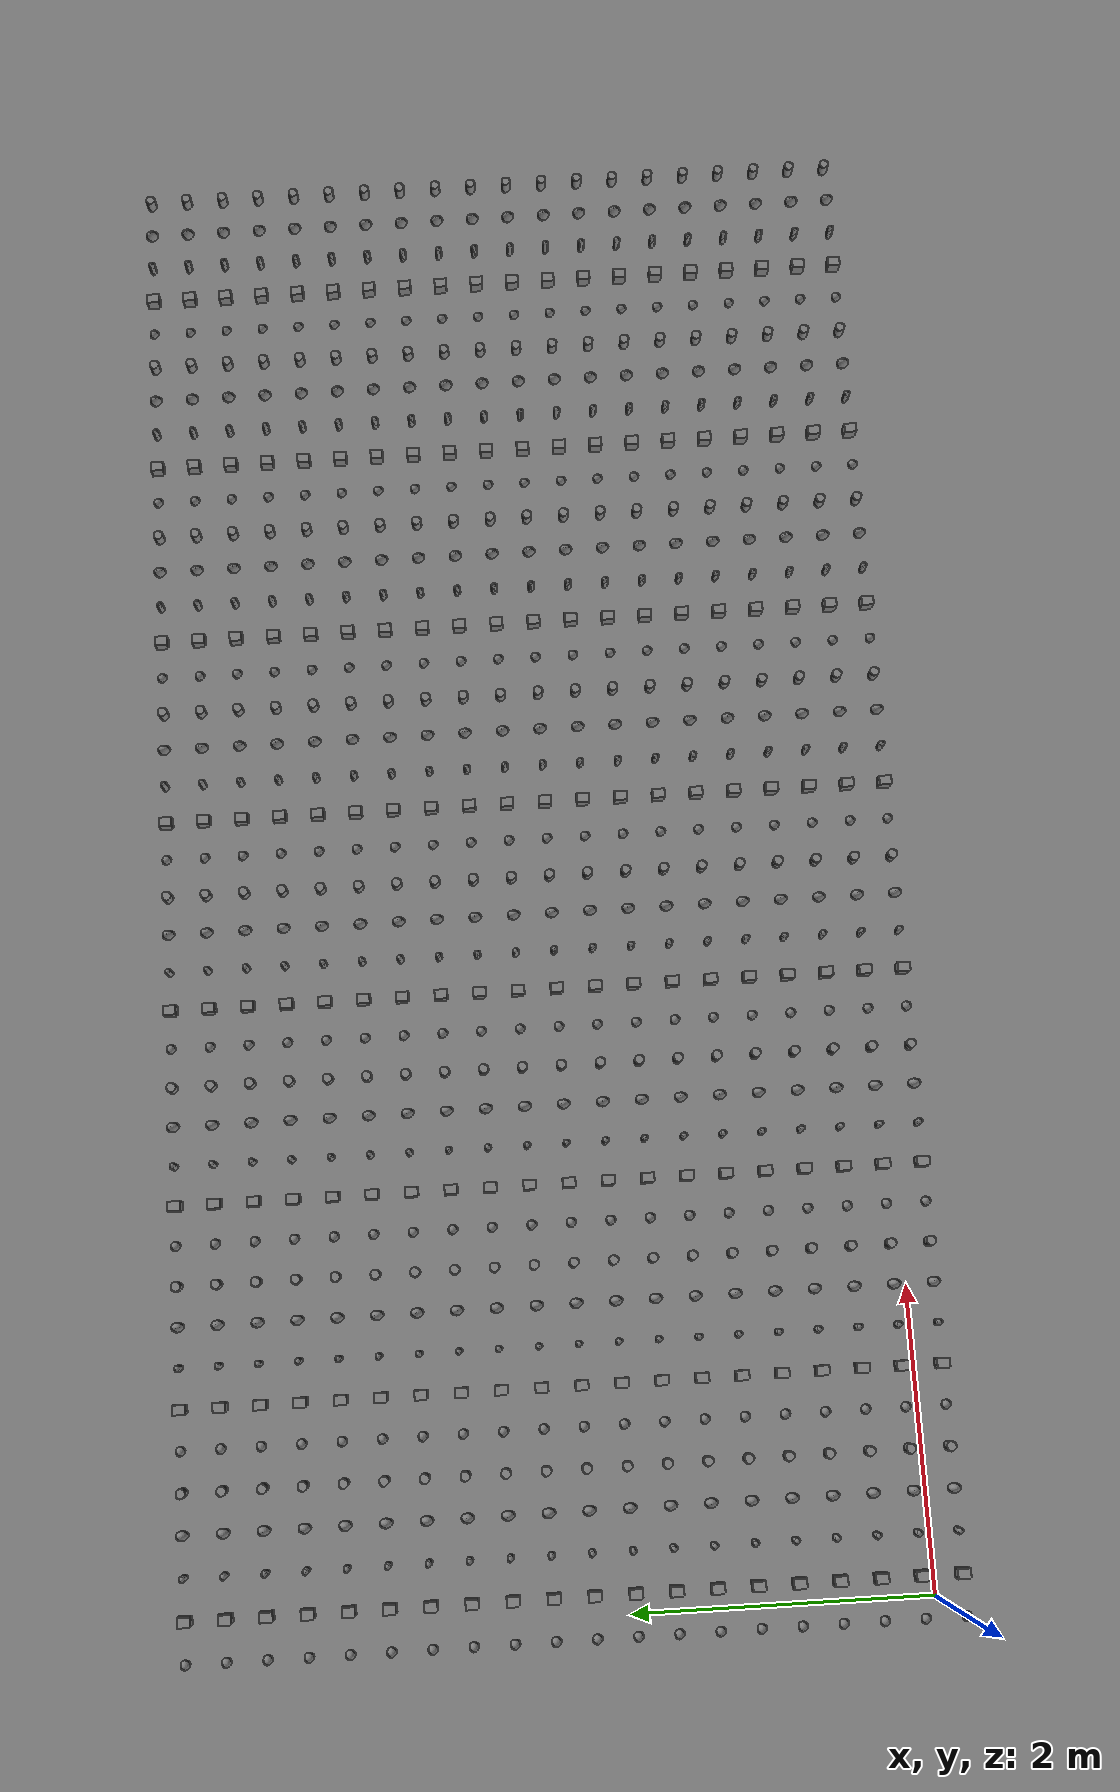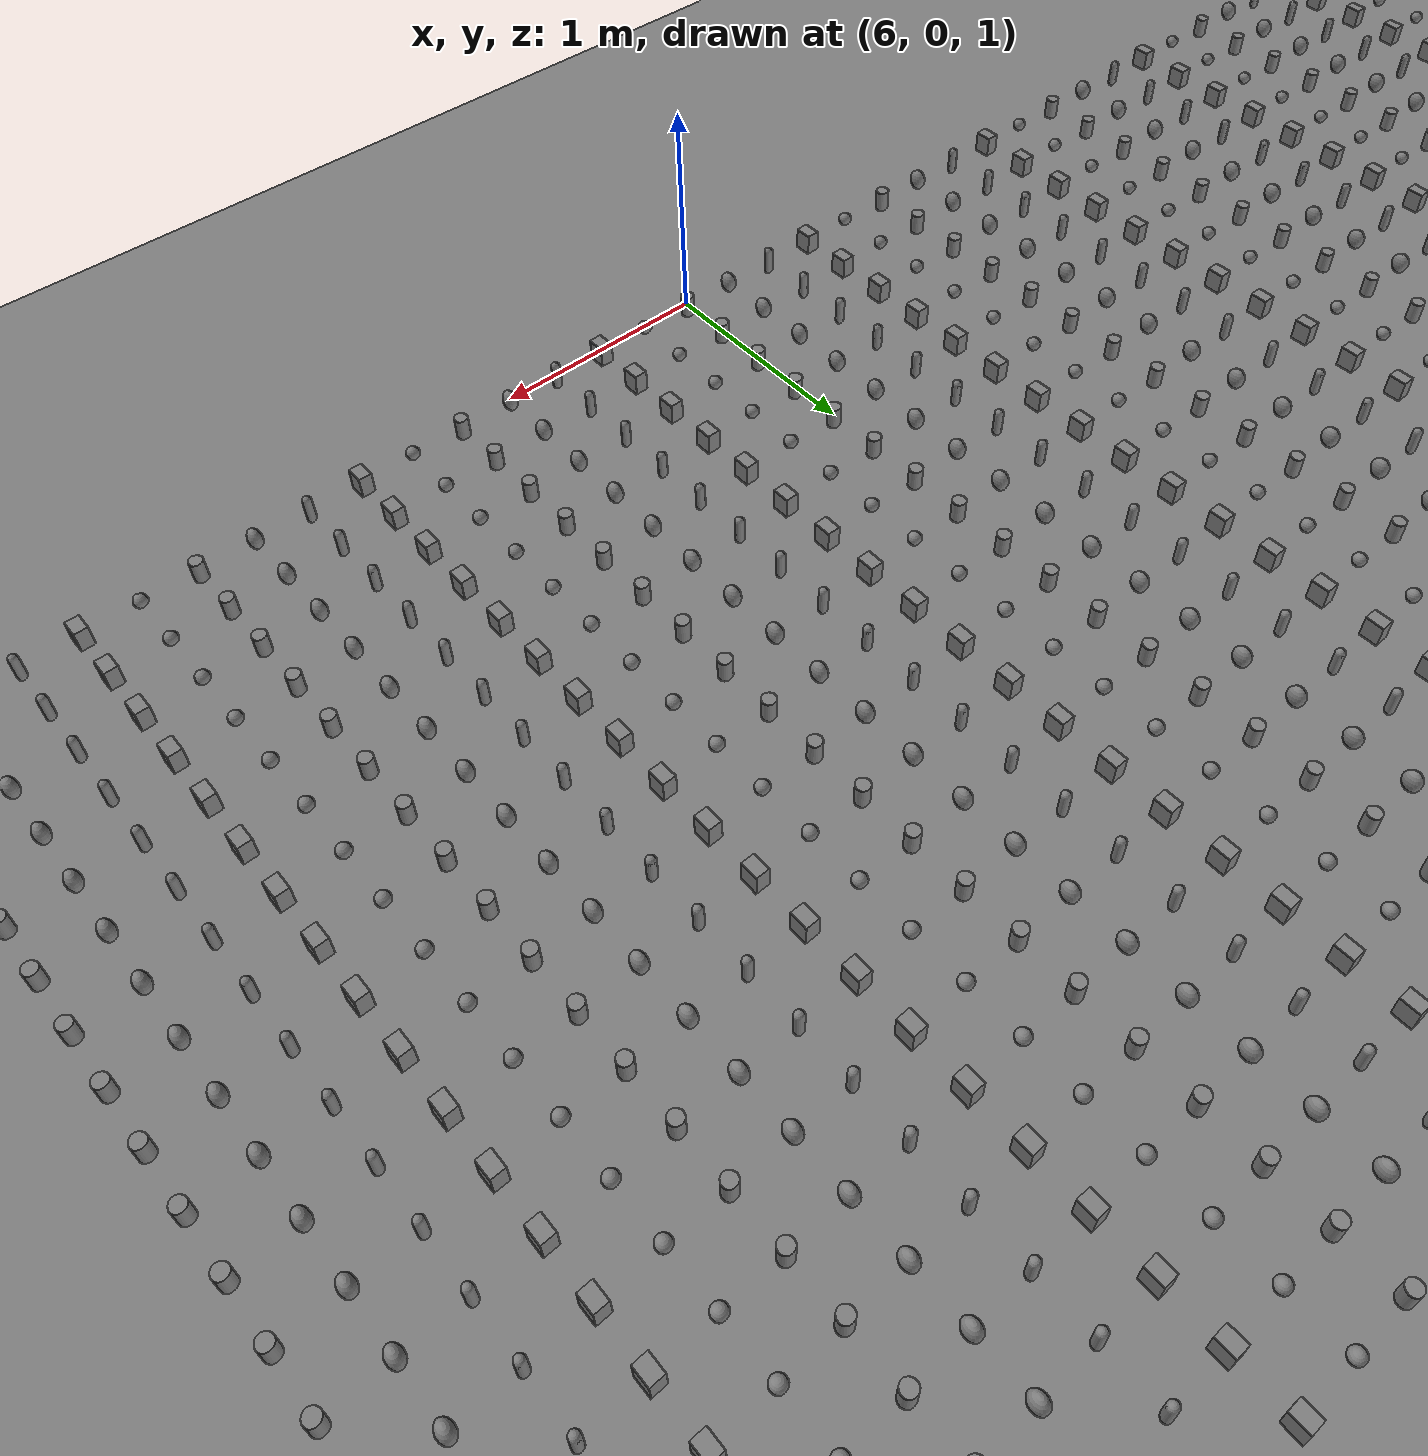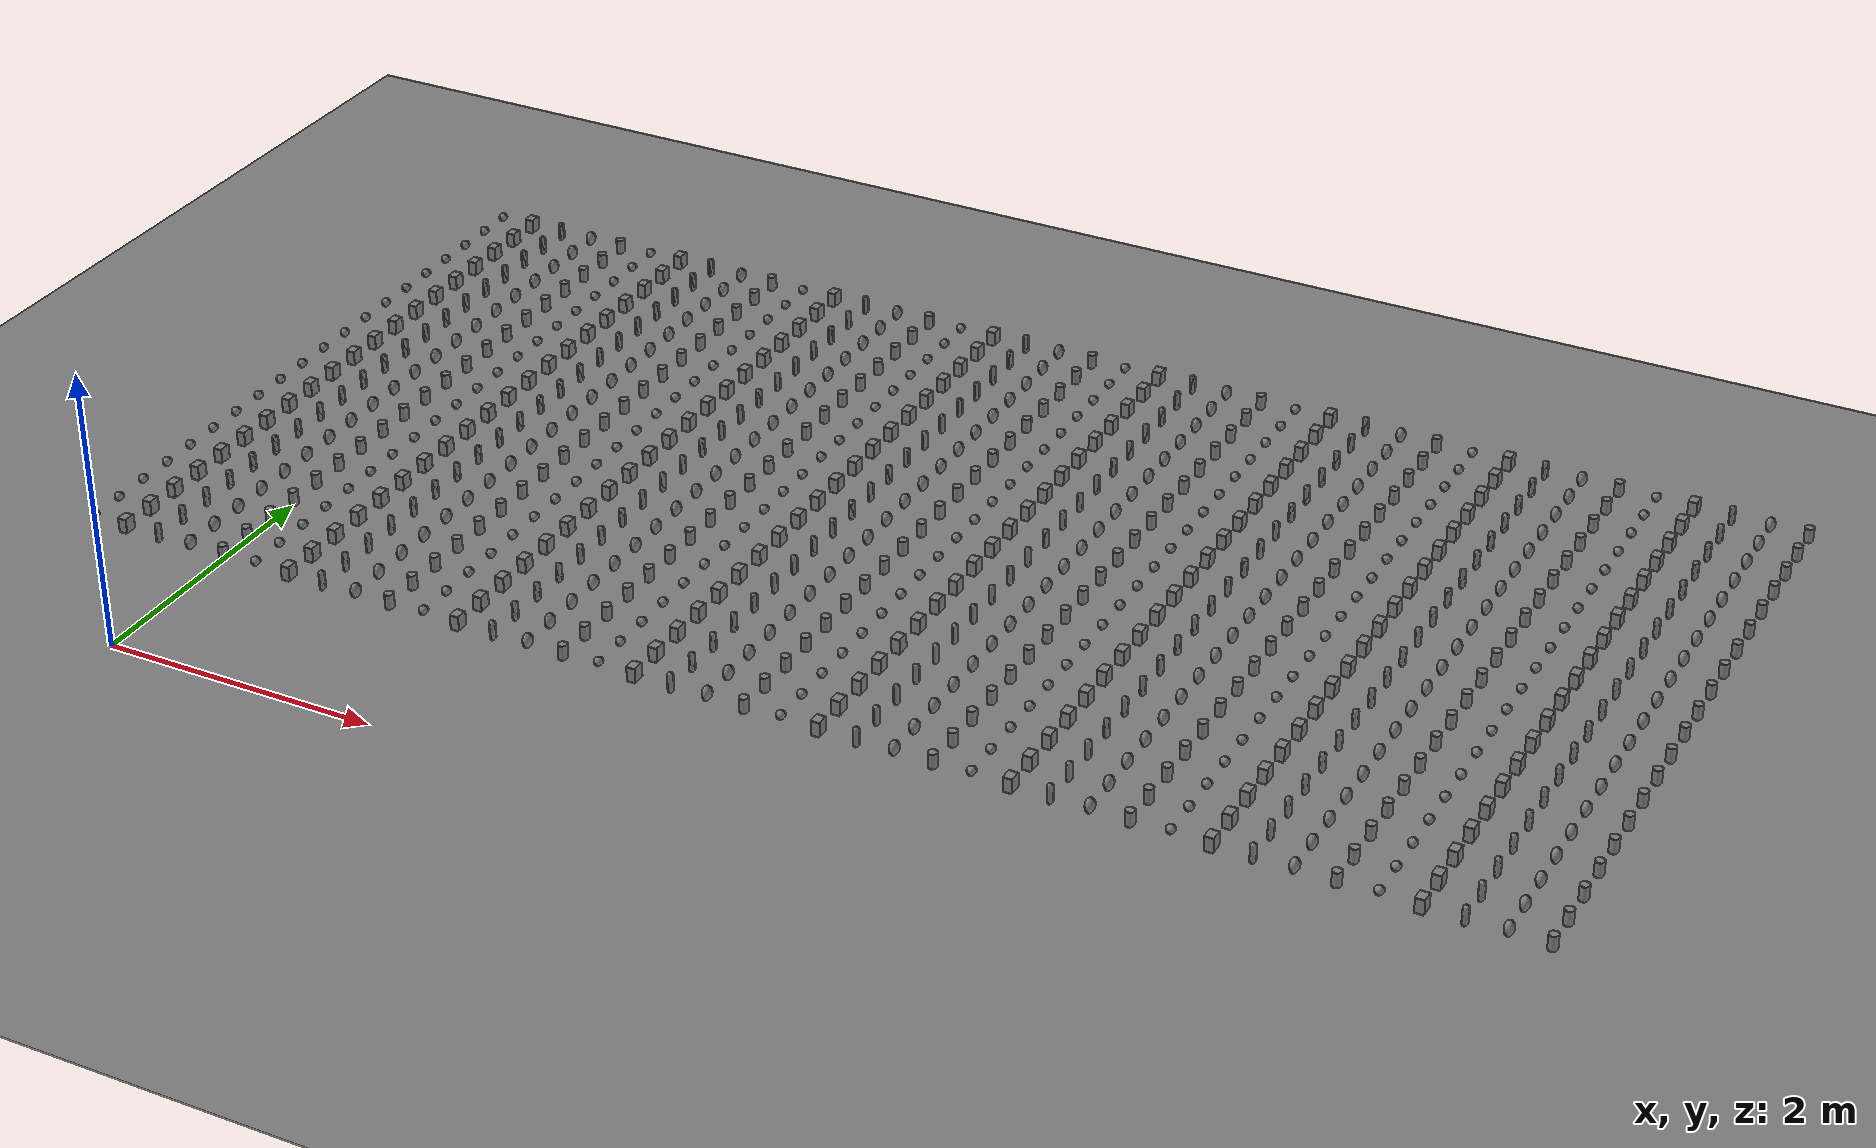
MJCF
<mujoco model="benchmark_many">
  <!-- GENERATED by gen_benchmark.py; do not edit by hand. -->
  <compiler angle="radian"/>
  <option timestep="0.002"/>
  <worldbody>
    <geom name="floor" type="plane" size="20 20 0.1"/>
    <body name="body_0" pos="0.000 0.000 1.0">
      <joint name="joint_0" type="hinge" axis="1 0 0"/>
      <geom name="geom_0" type="sphere" size="0.03"/>
    </body>
    <body name="body_1" pos="0.250 0.000 1.0">
      <joint name="joint_1" type="hinge" axis="0 1 0"/>
      <geom name="geom_1" type="box" size="0.03 0.04 0.05"/>
    </body>
    <body name="body_2" pos="0.500 0.000 1.0">
      <joint name="joint_2" type="slide" axis="0 0 1"/>
      <geom name="geom_2" type="capsule" size="0.02 0.05"/>
    </body>
    <body name="body_3" pos="0.750 0.000 1.0">
      <joint name="joint_3" type="hinge" axis="0 0 1"/>
      <geom name="geom_3" type="ellipsoid" size="0.03 0.04 0.05"/>
    </body>
    <body name="body_4" pos="1.000 0.000 1.0">
      <joint name="joint_4" type="slide" axis="1 0 0"/>
      <geom name="geom_4" type="cylinder" size="0.03 0.05"/>
    </body>
    <body name="body_5" pos="1.250 0.000 1.0">
      <joint name="joint_5" type="hinge" axis="1 0 0"/>
      <geom name="geom_5" type="sphere" size="0.03"/>
    </body>
    <body name="body_6" pos="1.500 0.000 1.0">
      <joint name="joint_6" type="hinge" axis="0 1 0"/>
      <geom name="geom_6" type="box" size="0.03 0.04 0.05"/>
    </body>
    <body name="body_7" pos="1.750 0.000 1.0">
      <joint name="joint_7" type="slide" axis="0 0 1"/>
      <geom name="geom_7" type="capsule" size="0.02 0.05"/>
    </body>
    <body name="body_8" pos="2.000 0.000 1.0">
      <joint name="joint_8" type="hinge" axis="0 0 1"/>
      <geom name="geom_8" type="ellipsoid" size="0.03 0.04 0.05"/>
    </body>
    <body name="body_9" pos="2.250 0.000 1.0">
      <joint name="joint_9" type="slide" axis="1 0 0"/>
      <geom name="geom_9" type="cylinder" size="0.03 0.05"/>
    </body>
    <body name="body_10" pos="2.500 0.000 1.0">
      <joint name="joint_10" type="hinge" axis="1 0 0"/>
      <geom name="geom_10" type="sphere" size="0.03"/>
    </body>
    <body name="body_11" pos="2.750 0.000 1.0">
      <joint name="joint_11" type="hinge" axis="0 1 0"/>
      <geom name="geom_11" type="box" size="0.03 0.04 0.05"/>
    </body>
    <body name="body_12" pos="3.000 0.000 1.0">
      <joint name="joint_12" type="slide" axis="0 0 1"/>
      <geom name="geom_12" type="capsule" size="0.02 0.05"/>
    </body>
    <body name="body_13" pos="3.250 0.000 1.0">
      <joint name="joint_13" type="hinge" axis="0 0 1"/>
      <geom name="geom_13" type="ellipsoid" size="0.03 0.04 0.05"/>
    </body>
    <body name="body_14" pos="3.500 0.000 1.0">
      <joint name="joint_14" type="slide" axis="1 0 0"/>
      <geom name="geom_14" type="cylinder" size="0.03 0.05"/>
    </body>
    <body name="body_15" pos="3.750 0.000 1.0">
      <joint name="joint_15" type="hinge" axis="1 0 0"/>
      <geom name="geom_15" type="sphere" size="0.03"/>
    </body>
    <body name="body_16" pos="4.000 0.000 1.0">
      <joint name="joint_16" type="hinge" axis="0 1 0"/>
      <geom name="geom_16" type="box" size="0.03 0.04 0.05"/>
    </body>
    <body name="body_17" pos="4.250 0.000 1.0">
      <joint name="joint_17" type="slide" axis="0 0 1"/>
      <geom name="geom_17" type="capsule" size="0.02 0.05"/>
    </body>
    <body name="body_18" pos="4.500 0.000 1.0">
      <joint name="joint_18" type="hinge" axis="0 0 1"/>
      <geom name="geom_18" type="ellipsoid" size="0.03 0.04 0.05"/>
    </body>
    <body name="body_19" pos="4.750 0.000 1.0">
      <joint name="joint_19" type="slide" axis="1 0 0"/>
      <geom name="geom_19" type="cylinder" size="0.03 0.05"/>
    </body>
    <body name="body_20" pos="5.000 0.000 1.0">
      <joint name="joint_20" type="hinge" axis="1 0 0"/>
      <geom name="geom_20" type="sphere" size="0.03"/>
    </body>
    <body name="body_21" pos="5.250 0.000 1.0">
      <joint name="joint_21" type="hinge" axis="0 1 0"/>
      <geom name="geom_21" type="box" size="0.03 0.04 0.05"/>
    </body>
    <body name="body_22" pos="5.500 0.000 1.0">
      <joint name="joint_22" type="slide" axis="0 0 1"/>
      <geom name="geom_22" type="capsule" size="0.02 0.05"/>
    </body>
    <body name="body_23" pos="5.750 0.000 1.0">
      <joint name="joint_23" type="hinge" axis="0 0 1"/>
      <geom name="geom_23" type="ellipsoid" size="0.03 0.04 0.05"/>
    </body>
    <body name="body_24" pos="6.000 0.000 1.0">
      <joint name="joint_24" type="slide" axis="1 0 0"/>
      <geom name="geom_24" type="cylinder" size="0.03 0.05"/>
    </body>
    <body name="body_25" pos="6.250 0.000 1.0">
      <joint name="joint_25" type="hinge" axis="1 0 0"/>
      <geom name="geom_25" type="sphere" size="0.03"/>
    </body>
    <body name="body_26" pos="6.500 0.000 1.0">
      <joint name="joint_26" type="hinge" axis="0 1 0"/>
      <geom name="geom_26" type="box" size="0.03 0.04 0.05"/>
    </body>
    <body name="body_27" pos="6.750 0.000 1.0">
      <joint name="joint_27" type="slide" axis="0 0 1"/>
      <geom name="geom_27" type="capsule" size="0.02 0.05"/>
    </body>
    <body name="body_28" pos="7.000 0.000 1.0">
      <joint name="joint_28" type="hinge" axis="0 0 1"/>
      <geom name="geom_28" type="ellipsoid" size="0.03 0.04 0.05"/>
    </body>
    <body name="body_29" pos="7.250 0.000 1.0">
      <joint name="joint_29" type="slide" axis="1 0 0"/>
      <geom name="geom_29" type="cylinder" size="0.03 0.05"/>
    </body>
    <body name="body_30" pos="7.500 0.000 1.0">
      <joint name="joint_30" type="hinge" axis="1 0 0"/>
      <geom name="geom_30" type="sphere" size="0.03"/>
    </body>
    <body name="body_31" pos="7.750 0.000 1.0">
      <joint name="joint_31" type="hinge" axis="0 1 0"/>
      <geom name="geom_31" type="box" size="0.03 0.04 0.05"/>
    </body>
    <body name="body_32" pos="8.000 0.000 1.0">
      <joint name="joint_32" type="slide" axis="0 0 1"/>
      <geom name="geom_32" type="capsule" size="0.02 0.05"/>
    </body>
    <body name="body_33" pos="8.250 0.000 1.0">
      <joint name="joint_33" type="hinge" axis="0 0 1"/>
      <geom name="geom_33" type="ellipsoid" size="0.03 0.04 0.05"/>
    </body>
    <body name="body_34" pos="8.500 0.000 1.0">
      <joint name="joint_34" type="slide" axis="1 0 0"/>
      <geom name="geom_34" type="cylinder" size="0.03 0.05"/>
    </body>
    <body name="body_35" pos="8.750 0.000 1.0">
      <joint name="joint_35" type="hinge" axis="1 0 0"/>
      <geom name="geom_35" type="sphere" size="0.03"/>
    </body>
    <body name="body_36" pos="9.000 0.000 1.0">
      <joint name="joint_36" type="hinge" axis="0 1 0"/>
      <geom name="geom_36" type="box" size="0.03 0.04 0.05"/>
    </body>
    <body name="body_37" pos="9.250 0.000 1.0">
      <joint name="joint_37" type="slide" axis="0 0 1"/>
      <geom name="geom_37" type="capsule" size="0.02 0.05"/>
    </body>
    <body name="body_38" pos="9.500 0.000 1.0">
      <joint name="joint_38" type="hinge" axis="0 0 1"/>
      <geom name="geom_38" type="ellipsoid" size="0.03 0.04 0.05"/>
    </body>
    <body name="body_39" pos="9.750 0.000 1.0">
      <joint name="joint_39" type="slide" axis="1 0 0"/>
      <geom name="geom_39" type="cylinder" size="0.03 0.05"/>
    </body>
    <body name="body_40" pos="0.000 0.250 1.0">
      <joint name="joint_40" type="hinge" axis="1 0 0"/>
      <geom name="geom_40" type="sphere" size="0.03"/>
    </body>
    <body name="body_41" pos="0.250 0.250 1.0">
      <joint name="joint_41" type="hinge" axis="0 1 0"/>
      <geom name="geom_41" type="box" size="0.03 0.04 0.05"/>
    </body>
    <body name="body_42" pos="0.500 0.250 1.0">
      <joint name="joint_42" type="slide" axis="0 0 1"/>
      <geom name="geom_42" type="capsule" size="0.02 0.05"/>
    </body>
    <body name="body_43" pos="0.750 0.250 1.0">
      <joint name="joint_43" type="hinge" axis="0 0 1"/>
      <geom name="geom_43" type="ellipsoid" size="0.03 0.04 0.05"/>
    </body>
    <body name="body_44" pos="1.000 0.250 1.0">
      <joint name="joint_44" type="slide" axis="1 0 0"/>
      <geom name="geom_44" type="cylinder" size="0.03 0.05"/>
    </body>
    <body name="body_45" pos="1.250 0.250 1.0">
      <joint name="joint_45" type="hinge" axis="1 0 0"/>
      <geom name="geom_45" type="sphere" size="0.03"/>
    </body>
    <body name="body_46" pos="1.500 0.250 1.0">
      <joint name="joint_46" type="hinge" axis="0 1 0"/>
      <geom name="geom_46" type="box" size="0.03 0.04 0.05"/>
    </body>
    <body name="body_47" pos="1.750 0.250 1.0">
      <joint name="joint_47" type="slide" axis="0 0 1"/>
      <geom name="geom_47" type="capsule" size="0.02 0.05"/>
    </body>
    <body name="body_48" pos="2.000 0.250 1.0">
      <joint name="joint_48" type="hinge" axis="0 0 1"/>
      <geom name="geom_48" type="ellipsoid" size="0.03 0.04 0.05"/>
    </body>
    <body name="body_49" pos="2.250 0.250 1.0">
      <joint name="joint_49" type="slide" axis="1 0 0"/>
      <geom name="geom_49" type="cylinder" size="0.03 0.05"/>
    </body>
    <body name="body_50" pos="2.500 0.250 1.0">
      <joint name="joint_50" type="hinge" axis="1 0 0"/>
      <geom name="geom_50" type="sphere" size="0.03"/>
    </body>
    <body name="body_51" pos="2.750 0.250 1.0">
      <joint name="joint_51" type="hinge" axis="0 1 0"/>
      <geom name="geom_51" type="box" size="0.03 0.04 0.05"/>
    </body>
    <body name="body_52" pos="3.000 0.250 1.0">
      <joint name="joint_52" type="slide" axis="0 0 1"/>
      <geom name="geom_52" type="capsule" size="0.02 0.05"/>
    </body>
    <body name="body_53" pos="3.250 0.250 1.0">
      <joint name="joint_53" type="hinge" axis="0 0 1"/>
      <geom name="geom_53" type="ellipsoid" size="0.03 0.04 0.05"/>
    </body>
    <body name="body_54" pos="3.500 0.250 1.0">
      <joint name="joint_54" type="slide" axis="1 0 0"/>
      <geom name="geom_54" type="cylinder" size="0.03 0.05"/>
    </body>
    <body name="body_55" pos="3.750 0.250 1.0">
      <joint name="joint_55" type="hinge" axis="1 0 0"/>
      <geom name="geom_55" type="sphere" size="0.03"/>
    </body>
    <body name="body_56" pos="4.000 0.250 1.0">
      <joint name="joint_56" type="hinge" axis="0 1 0"/>
      <geom name="geom_56" type="box" size="0.03 0.04 0.05"/>
    </body>
    <body name="body_57" pos="4.250 0.250 1.0">
      <joint name="joint_57" type="slide" axis="0 0 1"/>
      <geom name="geom_57" type="capsule" size="0.02 0.05"/>
    </body>
    <body name="body_58" pos="4.500 0.250 1.0">
      <joint name="joint_58" type="hinge" axis="0 0 1"/>
      <geom name="geom_58" type="ellipsoid" size="0.03 0.04 0.05"/>
    </body>
    <body name="body_59" pos="4.750 0.250 1.0">
      <joint name="joint_59" type="slide" axis="1 0 0"/>
      <geom name="geom_59" type="cylinder" size="0.03 0.05"/>
    </body>
    <body name="body_60" pos="5.000 0.250 1.0">
      <joint name="joint_60" type="hinge" axis="1 0 0"/>
      <geom name="geom_60" type="sphere" size="0.03"/>
    </body>
    <body name="body_61" pos="5.250 0.250 1.0">
      <joint name="joint_61" type="hinge" axis="0 1 0"/>
      <geom name="geom_61" type="box" size="0.03 0.04 0.05"/>
    </body>
    <body name="body_62" pos="5.500 0.250 1.0">
      <joint name="joint_62" type="slide" axis="0 0 1"/>
      <geom name="geom_62" type="capsule" size="0.02 0.05"/>
    </body>
    <body name="body_63" pos="5.750 0.250 1.0">
      <joint name="joint_63" type="hinge" axis="0 0 1"/>
      <geom name="geom_63" type="ellipsoid" size="0.03 0.04 0.05"/>
    </body>
    <body name="body_64" pos="6.000 0.250 1.0">
      <joint name="joint_64" type="slide" axis="1 0 0"/>
      <geom name="geom_64" type="cylinder" size="0.03 0.05"/>
    </body>
    <body name="body_65" pos="6.250 0.250 1.0">
      <joint name="joint_65" type="hinge" axis="1 0 0"/>
      <geom name="geom_65" type="sphere" size="0.03"/>
    </body>
    <body name="body_66" pos="6.500 0.250 1.0">
      <joint name="joint_66" type="hinge" axis="0 1 0"/>
      <geom name="geom_66" type="box" size="0.03 0.04 0.05"/>
    </body>
    <body name="body_67" pos="6.750 0.250 1.0">
      <joint name="joint_67" type="slide" axis="0 0 1"/>
      <geom name="geom_67" type="capsule" size="0.02 0.05"/>
    </body>
    <body name="body_68" pos="7.000 0.250 1.0">
      <joint name="joint_68" type="hinge" axis="0 0 1"/>
      <geom name="geom_68" type="ellipsoid" size="0.03 0.04 0.05"/>
    </body>
    <body name="body_69" pos="7.250 0.250 1.0">
      <joint name="joint_69" type="slide" axis="1 0 0"/>
      <geom name="geom_69" type="cylinder" size="0.03 0.05"/>
    </body>
    <body name="body_70" pos="7.500 0.250 1.0">
      <joint name="joint_70" type="hinge" axis="1 0 0"/>
      <geom name="geom_70" type="sphere" size="0.03"/>
    </body>
    <body name="body_71" pos="7.750 0.250 1.0">
      <joint name="joint_71" type="hinge" axis="0 1 0"/>
      <geom name="geom_71" type="box" size="0.03 0.04 0.05"/>
    </body>
    <body name="body_72" pos="8.000 0.250 1.0">
      <joint name="joint_72" type="slide" axis="0 0 1"/>
      <geom name="geom_72" type="capsule" size="0.02 0.05"/>
    </body>
    <body name="body_73" pos="8.250 0.250 1.0">
      <joint name="joint_73" type="hinge" axis="0 0 1"/>
      <geom name="geom_73" type="ellipsoid" size="0.03 0.04 0.05"/>
    </body>
    <body name="body_74" pos="8.500 0.250 1.0">
      <joint name="joint_74" type="slide" axis="1 0 0"/>
      <geom name="geom_74" type="cylinder" size="0.03 0.05"/>
    </body>
    <body name="body_75" pos="8.750 0.250 1.0">
      <joint name="joint_75" type="hinge" axis="1 0 0"/>
      <geom name="geom_75" type="sphere" size="0.03"/>
    </body>
    <body name="body_76" pos="9.000 0.250 1.0">
      <joint name="joint_76" type="hinge" axis="0 1 0"/>
      <geom name="geom_76" type="box" size="0.03 0.04 0.05"/>
    </body>
    <body name="body_77" pos="9.250 0.250 1.0">
      <joint name="joint_77" type="slide" axis="0 0 1"/>
      <geom name="geom_77" type="capsule" size="0.02 0.05"/>
    </body>
    <body name="body_78" pos="9.500 0.250 1.0">
      <joint name="joint_78" type="hinge" axis="0 0 1"/>
      <geom name="geom_78" type="ellipsoid" size="0.03 0.04 0.05"/>
    </body>
    <body name="body_79" pos="9.750 0.250 1.0">
      <joint name="joint_79" type="slide" axis="1 0 0"/>
      <geom name="geom_79" type="cylinder" size="0.03 0.05"/>
    </body>
    <body name="body_80" pos="0.000 0.500 1.0">
      <joint name="joint_80" type="hinge" axis="1 0 0"/>
      <geom name="geom_80" type="sphere" size="0.03"/>
    </body>
    <body name="body_81" pos="0.250 0.500 1.0">
      <joint name="joint_81" type="hinge" axis="0 1 0"/>
      <geom name="geom_81" type="box" size="0.03 0.04 0.05"/>
    </body>
    <body name="body_82" pos="0.500 0.500 1.0">
      <joint name="joint_82" type="slide" axis="0 0 1"/>
      <geom name="geom_82" type="capsule" size="0.02 0.05"/>
    </body>
    <body name="body_83" pos="0.750 0.500 1.0">
      <joint name="joint_83" type="hinge" axis="0 0 1"/>
      <geom name="geom_83" type="ellipsoid" size="0.03 0.04 0.05"/>
    </body>
    <body name="body_84" pos="1.000 0.500 1.0">
      <joint name="joint_84" type="slide" axis="1 0 0"/>
      <geom name="geom_84" type="cylinder" size="0.03 0.05"/>
    </body>
    <body name="body_85" pos="1.250 0.500 1.0">
      <joint name="joint_85" type="hinge" axis="1 0 0"/>
      <geom name="geom_85" type="sphere" size="0.03"/>
    </body>
    <body name="body_86" pos="1.500 0.500 1.0">
      <joint name="joint_86" type="hinge" axis="0 1 0"/>
      <geom name="geom_86" type="box" size="0.03 0.04 0.05"/>
    </body>
    <body name="body_87" pos="1.750 0.500 1.0">
      <joint name="joint_87" type="slide" axis="0 0 1"/>
      <geom name="geom_87" type="capsule" size="0.02 0.05"/>
    </body>
    <body name="body_88" pos="2.000 0.500 1.0">
      <joint name="joint_88" type="hinge" axis="0 0 1"/>
      <geom name="geom_88" type="ellipsoid" size="0.03 0.04 0.05"/>
    </body>
    <body name="body_89" pos="2.250 0.500 1.0">
      <joint name="joint_89" type="slide" axis="1 0 0"/>
      <geom name="geom_89" type="cylinder" size="0.03 0.05"/>
    </body>
    <body name="body_90" pos="2.500 0.500 1.0">
      <joint name="joint_90" type="hinge" axis="1 0 0"/>
      <geom name="geom_90" type="sphere" size="0.03"/>
    </body>
    <body name="body_91" pos="2.750 0.500 1.0">
      <joint name="joint_91" type="hinge" axis="0 1 0"/>
      <geom name="geom_91" type="box" size="0.03 0.04 0.05"/>
    </body>
    <body name="body_92" pos="3.000 0.500 1.0">
      <joint name="joint_92" type="slide" axis="0 0 1"/>
      <geom name="geom_92" type="capsule" size="0.02 0.05"/>
    </body>
    <body name="body_93" pos="3.250 0.500 1.0">
      <joint name="joint_93" type="hinge" axis="0 0 1"/>
      <geom name="geom_93" type="ellipsoid" size="0.03 0.04 0.05"/>
    </body>
    <body name="body_94" pos="3.500 0.500 1.0">
      <joint name="joint_94" type="slide" axis="1 0 0"/>
      <geom name="geom_94" type="cylinder" size="0.03 0.05"/>
    </body>
    <body name="body_95" pos="3.750 0.500 1.0">
      <joint name="joint_95" type="hinge" axis="1 0 0"/>
      <geom name="geom_95" type="sphere" size="0.03"/>
    </body>
    <body name="body_96" pos="4.000 0.500 1.0">
      <joint name="joint_96" type="hinge" axis="0 1 0"/>
      <geom name="geom_96" type="box" size="0.03 0.04 0.05"/>
    </body>
    <body name="body_97" pos="4.250 0.500 1.0">
      <joint name="joint_97" type="slide" axis="0 0 1"/>
      <geom name="geom_97" type="capsule" size="0.02 0.05"/>
    </body>
    <body name="body_98" pos="4.500 0.500 1.0">
      <joint name="joint_98" type="hinge" axis="0 0 1"/>
      <geom name="geom_98" type="ellipsoid" size="0.03 0.04 0.05"/>
    </body>
    <body name="body_99" pos="4.750 0.500 1.0">
      <joint name="joint_99" type="slide" axis="1 0 0"/>
      <geom name="geom_99" type="cylinder" size="0.03 0.05"/>
    </body>
    <body name="body_100" pos="5.000 0.500 1.0">
      <joint name="joint_100" type="hinge" axis="1 0 0"/>
      <geom name="geom_100" type="sphere" size="0.03"/>
    </body>
    <body name="body_101" pos="5.250 0.500 1.0">
      <joint name="joint_101" type="hinge" axis="0 1 0"/>
      <geom name="geom_101" type="box" size="0.03 0.04 0.05"/>
    </body>
    <body name="body_102" pos="5.500 0.500 1.0">
      <joint name="joint_102" type="slide" axis="0 0 1"/>
      <geom name="geom_102" type="capsule" size="0.02 0.05"/>
    </body>
    <body name="body_103" pos="5.750 0.500 1.0">
      <joint name="joint_103" type="hinge" axis="0 0 1"/>
      <geom name="geom_103" type="ellipsoid" size="0.03 0.04 0.05"/>
    </body>
    <body name="body_104" pos="6.000 0.500 1.0">
      <joint name="joint_104" type="slide" axis="1 0 0"/>
      <geom name="geom_104" type="cylinder" size="0.03 0.05"/>
    </body>
    <body name="body_105" pos="6.250 0.500 1.0">
      <joint name="joint_105" type="hinge" axis="1 0 0"/>
      <geom name="geom_105" type="sphere" size="0.03"/>
    </body>
    <body name="body_106" pos="6.500 0.500 1.0">
      <joint name="joint_106" type="hinge" axis="0 1 0"/>
      <geom name="geom_106" type="box" size="0.03 0.04 0.05"/>
    </body>
    <body name="body_107" pos="6.750 0.500 1.0">
      <joint name="joint_107" type="slide" axis="0 0 1"/>
      <geom name="geom_107" type="capsule" size="0.02 0.05"/>
    </body>
    <body name="body_108" pos="7.000 0.500 1.0">
      <joint name="joint_108" type="hinge" axis="0 0 1"/>
      <geom name="geom_108" type="ellipsoid" size="0.03 0.04 0.05"/>
    </body>
    <body name="body_109" pos="7.250 0.500 1.0">
      <joint name="joint_109" type="slide" axis="1 0 0"/>
      <geom name="geom_109" type="cylinder" size="0.03 0.05"/>
    </body>
    <body name="body_110" pos="7.500 0.500 1.0">
      <joint name="joint_110" type="hinge" axis="1 0 0"/>
      <geom name="geom_110" type="sphere" size="0.03"/>
    </body>
    <body name="body_111" pos="7.750 0.500 1.0">
      <joint name="joint_111" type="hinge" axis="0 1 0"/>
      <geom name="geom_111" type="box" size="0.03 0.04 0.05"/>
    </body>
    <body name="body_112" pos="8.000 0.500 1.0">
      <joint name="joint_112" type="slide" axis="0 0 1"/>
      <geom name="geom_112" type="capsule" size="0.02 0.05"/>
    </body>
    <body name="body_113" pos="8.250 0.500 1.0">
      <joint name="joint_113" type="hinge" axis="0 0 1"/>
      <geom name="geom_113" type="ellipsoid" size="0.03 0.04 0.05"/>
    </body>
    <body name="body_114" pos="8.500 0.500 1.0">
      <joint name="joint_114" type="slide" axis="1 0 0"/>
      <geom name="geom_114" type="cylinder" size="0.03 0.05"/>
    </body>
    <body name="body_115" pos="8.750 0.500 1.0">
      <joint name="joint_115" type="hinge" axis="1 0 0"/>
      <geom name="geom_115" type="sphere" size="0.03"/>
    </body>
    <body name="body_116" pos="9.000 0.500 1.0">
      <joint name="joint_116" type="hinge" axis="0 1 0"/>
      <geom name="geom_116" type="box" size="0.03 0.04 0.05"/>
    </body>
    <body name="body_117" pos="9.250 0.500 1.0">
      <joint name="joint_117" type="slide" axis="0 0 1"/>
      <geom name="geom_117" type="capsule" size="0.02 0.05"/>
    </body>
    <body name="body_118" pos="9.500 0.500 1.0">
      <joint name="joint_118" type="hinge" axis="0 0 1"/>
      <geom name="geom_118" type="ellipsoid" size="0.03 0.04 0.05"/>
    </body>
    <body name="body_119" pos="9.750 0.500 1.0">
      <joint name="joint_119" type="slide" axis="1 0 0"/>
      <geom name="geom_119" type="cylinder" size="0.03 0.05"/>
    </body>
    <body name="body_120" pos="0.000 0.750 1.0">
      <joint name="joint_120" type="hinge" axis="1 0 0"/>
      <geom name="geom_120" type="sphere" size="0.03"/>
    </body>
    <body name="body_121" pos="0.250 0.750 1.0">
      <joint name="joint_121" type="hinge" axis="0 1 0"/>
      <geom name="geom_121" type="box" size="0.03 0.04 0.05"/>
    </body>
    <body name="body_122" pos="0.500 0.750 1.0">
      <joint name="joint_122" type="slide" axis="0 0 1"/>
      <geom name="geom_122" type="capsule" size="0.02 0.05"/>
    </body>
    <body name="body_123" pos="0.750 0.750 1.0">
      <joint name="joint_123" type="hinge" axis="0 0 1"/>
      <geom name="geom_123" type="ellipsoid" size="0.03 0.04 0.05"/>
    </body>
    <body name="body_124" pos="1.000 0.750 1.0">
      <joint name="joint_124" type="slide" axis="1 0 0"/>
      <geom name="geom_124" type="cylinder" size="0.03 0.05"/>
    </body>
    <body name="body_125" pos="1.250 0.750 1.0">
      <joint name="joint_125" type="hinge" axis="1 0 0"/>
      <geom name="geom_125" type="sphere" size="0.03"/>
    </body>
    <body name="body_126" pos="1.500 0.750 1.0">
      <joint name="joint_126" type="hinge" axis="0 1 0"/>
      <geom name="geom_126" type="box" size="0.03 0.04 0.05"/>
    </body>
    <body name="body_127" pos="1.750 0.750 1.0">
      <joint name="joint_127" type="slide" axis="0 0 1"/>
      <geom name="geom_127" type="capsule" size="0.02 0.05"/>
    </body>
    <body name="body_128" pos="2.000 0.750 1.0">
      <joint name="joint_128" type="hinge" axis="0 0 1"/>
      <geom name="geom_128" type="ellipsoid" size="0.03 0.04 0.05"/>
    </body>
    <body name="body_129" pos="2.250 0.750 1.0">
      <joint name="joint_129" type="slide" axis="1 0 0"/>
      <geom name="geom_129" type="cylinder" size="0.03 0.05"/>
    </body>
    <body name="body_130" pos="2.500 0.750 1.0">
      <joint name="joint_130" type="hinge" axis="1 0 0"/>
      <geom name="geom_130" type="sphere" size="0.03"/>
    </body>
    <body name="body_131" pos="2.750 0.750 1.0">
      <joint name="joint_131" type="hinge" axis="0 1 0"/>
      <geom name="geom_131" type="box" size="0.03 0.04 0.05"/>
    </body>
    <body name="body_132" pos="3.000 0.750 1.0">
      <joint name="joint_132" type="slide" axis="0 0 1"/>
      <geom name="geom_132" type="capsule" size="0.02 0.05"/>
    </body>
    <body name="body_133" pos="3.250 0.750 1.0">
      <joint name="joint_133" type="hinge" axis="0 0 1"/>
      <geom name="geom_133" type="ellipsoid" size="0.03 0.04 0.05"/>
    </body>
    <body name="body_134" pos="3.500 0.750 1.0">
      <joint name="joint_134" type="slide" axis="1 0 0"/>
      <geom name="geom_134" type="cylinder" size="0.03 0.05"/>
    </body>
    <body name="body_135" pos="3.750 0.750 1.0">
      <joint name="joint_135" type="hinge" axis="1 0 0"/>
      <geom name="geom_135" type="sphere" size="0.03"/>
    </body>
    <body name="body_136" pos="4.000 0.750 1.0">
      <joint name="joint_136" type="hinge" axis="0 1 0"/>
      <geom name="geom_136" type="box" size="0.03 0.04 0.05"/>
    </body>
    <body name="body_137" pos="4.250 0.750 1.0">
      <joint name="joint_137" type="slide" axis="0 0 1"/>
      <geom name="geom_137" type="capsule" size="0.02 0.05"/>
    </body>
    <body name="body_138" pos="4.500 0.750 1.0">
      <joint name="joint_138" type="hinge" axis="0 0 1"/>
      <geom name="geom_138" type="ellipsoid" size="0.03 0.04 0.05"/>
    </body>
    <body name="body_139" pos="4.750 0.750 1.0">
      <joint name="joint_139" type="slide" axis="1 0 0"/>
      <geom name="geom_139" type="cylinder" size="0.03 0.05"/>
    </body>
    <body name="body_140" pos="5.000 0.750 1.0">
      <joint name="joint_140" type="hinge" axis="1 0 0"/>
      <geom name="geom_140" type="sphere" size="0.03"/>
    </body>
    <body name="body_141" pos="5.250 0.750 1.0">
      <joint name="joint_141" type="hinge" axis="0 1 0"/>
      <geom name="geom_141" type="box" size="0.03 0.04 0.05"/>
    </body>
    <body name="body_142" pos="5.500 0.750 1.0">
      <joint name="joint_142" type="slide" axis="0 0 1"/>
      <geom name="geom_142" type="capsule" size="0.02 0.05"/>
    </body>
    <body name="body_143" pos="5.750 0.750 1.0">
      <joint name="joint_143" type="hinge" axis="0 0 1"/>
      <geom name="geom_143" type="ellipsoid" size="0.03 0.04 0.05"/>
    </body>
    <body name="body_144" pos="6.000 0.750 1.0">
      <joint name="joint_144" type="slide" axis="1 0 0"/>
      <geom name="geom_144" type="cylinder" size="0.03 0.05"/>
    </body>
    <body name="body_145" pos="6.250 0.750 1.0">
      <joint name="joint_145" type="hinge" axis="1 0 0"/>
      <geom name="geom_145" type="sphere" size="0.03"/>
    </body>
    <body name="body_146" pos="6.500 0.750 1.0">
      <joint name="joint_146" type="hinge" axis="0 1 0"/>
      <geom name="geom_146" type="box" size="0.03 0.04 0.05"/>
    </body>
    <body name="body_147" pos="6.750 0.750 1.0">
      <joint name="joint_147" type="slide" axis="0 0 1"/>
      <geom name="geom_147" type="capsule" size="0.02 0.05"/>
    </body>
    <body name="body_148" pos="7.000 0.750 1.0">
      <joint name="joint_148" type="hinge" axis="0 0 1"/>
      <geom name="geom_148" type="ellipsoid" size="0.03 0.04 0.05"/>
    </body>
    <body name="body_149" pos="7.250 0.750 1.0">
      <joint name="joint_149" type="slide" axis="1 0 0"/>
      <geom name="geom_149" type="cylinder" size="0.03 0.05"/>
    </body>
    <body name="body_150" pos="7.500 0.750 1.0">
      <joint name="joint_150" type="hinge" axis="1 0 0"/>
      <geom name="geom_150" type="sphere" size="0.03"/>
    </body>
    <body name="body_151" pos="7.750 0.750 1.0">
      <joint name="joint_151" type="hinge" axis="0 1 0"/>
      <geom name="geom_151" type="box" size="0.03 0.04 0.05"/>
    </body>
    <body name="body_152" pos="8.000 0.750 1.0">
      <joint name="joint_152" type="slide" axis="0 0 1"/>
      <geom name="geom_152" type="capsule" size="0.02 0.05"/>
    </body>
    <body name="body_153" pos="8.250 0.750 1.0">
      <joint name="joint_153" type="hinge" axis="0 0 1"/>
      <geom name="geom_153" type="ellipsoid" size="0.03 0.04 0.05"/>
    </body>
    <body name="body_154" pos="8.500 0.750 1.0">
      <joint name="joint_154" type="slide" axis="1 0 0"/>
      <geom name="geom_154" type="cylinder" size="0.03 0.05"/>
    </body>
    <body name="body_155" pos="8.750 0.750 1.0">
      <joint name="joint_155" type="hinge" axis="1 0 0"/>
      <geom name="geom_155" type="sphere" size="0.03"/>
    </body>
    <body name="body_156" pos="9.000 0.750 1.0">
      <joint name="joint_156" type="hinge" axis="0 1 0"/>
      <geom name="geom_156" type="box" size="0.03 0.04 0.05"/>
    </body>
    <body name="body_157" pos="9.250 0.750 1.0">
      <joint name="joint_157" type="slide" axis="0 0 1"/>
      <geom name="geom_157" type="capsule" size="0.02 0.05"/>
    </body>
    <body name="body_158" pos="9.500 0.750 1.0">
      <joint name="joint_158" type="hinge" axis="0 0 1"/>
      <geom name="geom_158" type="ellipsoid" size="0.03 0.04 0.05"/>
    </body>
    <body name="body_159" pos="9.750 0.750 1.0">
      <joint name="joint_159" type="slide" axis="1 0 0"/>
      <geom name="geom_159" type="cylinder" size="0.03 0.05"/>
    </body>
    <body name="body_160" pos="0.000 1.000 1.0">
      <joint name="joint_160" type="hinge" axis="1 0 0"/>
      <geom name="geom_160" type="sphere" size="0.03"/>
    </body>
    <body name="body_161" pos="0.250 1.000 1.0">
      <joint name="joint_161" type="hinge" axis="0 1 0"/>
      <geom name="geom_161" type="box" size="0.03 0.04 0.05"/>
    </body>
    <body name="body_162" pos="0.500 1.000 1.0">
      <joint name="joint_162" type="slide" axis="0 0 1"/>
      <geom name="geom_162" type="capsule" size="0.02 0.05"/>
    </body>
    <body name="body_163" pos="0.750 1.000 1.0">
      <joint name="joint_163" type="hinge" axis="0 0 1"/>
      <geom name="geom_163" type="ellipsoid" size="0.03 0.04 0.05"/>
    </body>
    <body name="body_164" pos="1.000 1.000 1.0">
      <joint name="joint_164" type="slide" axis="1 0 0"/>
      <geom name="geom_164" type="cylinder" size="0.03 0.05"/>
    </body>
    <body name="body_165" pos="1.250 1.000 1.0">
      <joint name="joint_165" type="hinge" axis="1 0 0"/>
      <geom name="geom_165" type="sphere" size="0.03"/>
    </body>
    <body name="body_166" pos="1.500 1.000 1.0">
      <joint name="joint_166" type="hinge" axis="0 1 0"/>
      <geom name="geom_166" type="box" size="0.03 0.04 0.05"/>
    </body>
    <body name="body_167" pos="1.750 1.000 1.0">
      <joint name="joint_167" type="slide" axis="0 0 1"/>
      <geom name="geom_167" type="capsule" size="0.02 0.05"/>
    </body>
    <body name="body_168" pos="2.000 1.000 1.0">
      <joint name="joint_168" type="hinge" axis="0 0 1"/>
      <geom name="geom_168" type="ellipsoid" size="0.03 0.04 0.05"/>
    </body>
    <body name="body_169" pos="2.250 1.000 1.0">
      <joint name="joint_169" type="slide" axis="1 0 0"/>
      <geom name="geom_169" type="cylinder" size="0.03 0.05"/>
    </body>
    <body name="body_170" pos="2.500 1.000 1.0">
      <joint name="joint_170" type="hinge" axis="1 0 0"/>
      <geom name="geom_170" type="sphere" size="0.03"/>
    </body>
    <body name="body_171" pos="2.750 1.000 1.0">
      <joint name="joint_171" type="hinge" axis="0 1 0"/>
      <geom name="geom_171" type="box" size="0.03 0.04 0.05"/>
    </body>
    <body name="body_172" pos="3.000 1.000 1.0">
      <joint name="joint_172" type="slide" axis="0 0 1"/>
      <geom name="geom_172" type="capsule" size="0.02 0.05"/>
    </body>
    <body name="body_173" pos="3.250 1.000 1.0">
      <joint name="joint_173" type="hinge" axis="0 0 1"/>
      <geom name="geom_173" type="ellipsoid" size="0.03 0.04 0.05"/>
    </body>
    <body name="body_174" pos="3.500 1.000 1.0">
      <joint name="joint_174" type="slide" axis="1 0 0"/>
      <geom name="geom_174" type="cylinder" size="0.03 0.05"/>
    </body>
    <body name="body_175" pos="3.750 1.000 1.0">
      <joint name="joint_175" type="hinge" axis="1 0 0"/>
      <geom name="geom_175" type="sphere" size="0.03"/>
    </body>
    <body name="body_176" pos="4.000 1.000 1.0">
      <joint name="joint_176" type="hinge" axis="0 1 0"/>
      <geom name="geom_176" type="box" size="0.03 0.04 0.05"/>
    </body>
    <body name="body_177" pos="4.250 1.000 1.0">
      <joint name="joint_177" type="slide" axis="0 0 1"/>
      <geom name="geom_177" type="capsule" size="0.02 0.05"/>
    </body>
    <body name="body_178" pos="4.500 1.000 1.0">
      <joint name="joint_178" type="hinge" axis="0 0 1"/>
      <geom name="geom_178" type="ellipsoid" size="0.03 0.04 0.05"/>
    </body>
    <body name="body_179" pos="4.750 1.000 1.0">
      <joint name="joint_179" type="slide" axis="1 0 0"/>
      <geom name="geom_179" type="cylinder" size="0.03 0.05"/>
    </body>
    <body name="body_180" pos="5.000 1.000 1.0">
      <joint name="joint_180" type="hinge" axis="1 0 0"/>
      <geom name="geom_180" type="sphere" size="0.03"/>
    </body>
    <body name="body_181" pos="5.250 1.000 1.0">
      <joint name="joint_181" type="hinge" axis="0 1 0"/>
      <geom name="geom_181" type="box" size="0.03 0.04 0.05"/>
    </body>
    <body name="body_182" pos="5.500 1.000 1.0">
      <joint name="joint_182" type="slide" axis="0 0 1"/>
      <geom name="geom_182" type="capsule" size="0.02 0.05"/>
    </body>
    <body name="body_183" pos="5.750 1.000 1.0">
      <joint name="joint_183" type="hinge" axis="0 0 1"/>
      <geom name="geom_183" type="ellipsoid" size="0.03 0.04 0.05"/>
    </body>
    <body name="body_184" pos="6.000 1.000 1.0">
      <joint name="joint_184" type="slide" axis="1 0 0"/>
      <geom name="geom_184" type="cylinder" size="0.03 0.05"/>
    </body>
    <body name="body_185" pos="6.250 1.000 1.0">
      <joint name="joint_185" type="hinge" axis="1 0 0"/>
      <geom name="geom_185" type="sphere" size="0.03"/>
    </body>
    <body name="body_186" pos="6.500 1.000 1.0">
      <joint name="joint_186" type="hinge" axis="0 1 0"/>
      <geom name="geom_186" type="box" size="0.03 0.04 0.05"/>
    </body>
    <body name="body_187" pos="6.750 1.000 1.0">
      <joint name="joint_187" type="slide" axis="0 0 1"/>
      <geom name="geom_187" type="capsule" size="0.02 0.05"/>
    </body>
    <body name="body_188" pos="7.000 1.000 1.0">
      <joint name="joint_188" type="hinge" axis="0 0 1"/>
      <geom name="geom_188" type="ellipsoid" size="0.03 0.04 0.05"/>
    </body>
    <body name="body_189" pos="7.250 1.000 1.0">
      <joint name="joint_189" type="slide" axis="1 0 0"/>
      <geom name="geom_189" type="cylinder" size="0.03 0.05"/>
    </body>
    <body name="body_190" pos="7.500 1.000 1.0">
      <joint name="joint_190" type="hinge" axis="1 0 0"/>
      <geom name="geom_190" type="sphere" size="0.03"/>
    </body>
    <body name="body_191" pos="7.750 1.000 1.0">
      <joint name="joint_191" type="hinge" axis="0 1 0"/>
      <geom name="geom_191" type="box" size="0.03 0.04 0.05"/>
    </body>
    <body name="body_192" pos="8.000 1.000 1.0">
      <joint name="joint_192" type="slide" axis="0 0 1"/>
      <geom name="geom_192" type="capsule" size="0.02 0.05"/>
    </body>
    <body name="body_193" pos="8.250 1.000 1.0">
      <joint name="joint_193" type="hinge" axis="0 0 1"/>
      <geom name="geom_193" type="ellipsoid" size="0.03 0.04 0.05"/>
    </body>
    <body name="body_194" pos="8.500 1.000 1.0">
      <joint name="joint_194" type="slide" axis="1 0 0"/>
      <geom name="geom_194" type="cylinder" size="0.03 0.05"/>
    </body>
    <body name="body_195" pos="8.750 1.000 1.0">
      <joint name="joint_195" type="hinge" axis="1 0 0"/>
      <geom name="geom_195" type="sphere" size="0.03"/>
    </body>
    <body name="body_196" pos="9.000 1.000 1.0">
      <joint name="joint_196" type="hinge" axis="0 1 0"/>
      <geom name="geom_196" type="box" size="0.03 0.04 0.05"/>
    </body>
    <body name="body_197" pos="9.250 1.000 1.0">
      <joint name="joint_197" type="slide" axis="0 0 1"/>
      <geom name="geom_197" type="capsule" size="0.02 0.05"/>
    </body>
    <body name="body_198" pos="9.500 1.000 1.0">
      <joint name="joint_198" type="hinge" axis="0 0 1"/>
      <geom name="geom_198" type="ellipsoid" size="0.03 0.04 0.05"/>
    </body>
    <body name="body_199" pos="9.750 1.000 1.0">
      <joint name="joint_199" type="slide" axis="1 0 0"/>
      <geom name="geom_199" type="cylinder" size="0.03 0.05"/>
    </body>
    <body name="body_200" pos="0.000 1.250 1.0">
      <joint name="joint_200" type="hinge" axis="1 0 0"/>
      <geom name="geom_200" type="sphere" size="0.03"/>
    </body>
    <body name="body_201" pos="0.250 1.250 1.0">
      <joint name="joint_201" type="hinge" axis="0 1 0"/>
      <geom name="geom_201" type="box" size="0.03 0.04 0.05"/>
    </body>
    <body name="body_202" pos="0.500 1.250 1.0">
      <joint name="joint_202" type="slide" axis="0 0 1"/>
      <geom name="geom_202" type="capsule" size="0.02 0.05"/>
    </body>
    <body name="body_203" pos="0.750 1.250 1.0">
      <joint name="joint_203" type="hinge" axis="0 0 1"/>
      <geom name="geom_203" type="ellipsoid" size="0.03 0.04 0.05"/>
    </body>
    <body name="body_204" pos="1.000 1.250 1.0">
      <joint name="joint_204" type="slide" axis="1 0 0"/>
      <geom name="geom_204" type="cylinder" size="0.03 0.05"/>
    </body>
    <body name="body_205" pos="1.250 1.250 1.0">
      <joint name="joint_205" type="hinge" axis="1 0 0"/>
      <geom name="geom_205" type="sphere" size="0.03"/>
    </body>
    <body name="body_206" pos="1.500 1.250 1.0">
      <joint name="joint_206" type="hinge" axis="0 1 0"/>
      <geom name="geom_206" type="box" size="0.03 0.04 0.05"/>
    </body>
    <body name="body_207" pos="1.750 1.250 1.0">
      <joint name="joint_207" type="slide" axis="0 0 1"/>
      <geom name="geom_207" type="capsule" size="0.02 0.05"/>
    </body>
    <body name="body_208" pos="2.000 1.250 1.0">
      <joint name="joint_208" type="hinge" axis="0 0 1"/>
      <geom name="geom_208" type="ellipsoid" size="0.03 0.04 0.05"/>
    </body>
    <body name="body_209" pos="2.250 1.250 1.0">
      <joint name="joint_209" type="slide" axis="1 0 0"/>
      <geom name="geom_209" type="cylinder" size="0.03 0.05"/>
    </body>
    <body name="body_210" pos="2.500 1.250 1.0">
      <joint name="joint_210" type="hinge" axis="1 0 0"/>
      <geom name="geom_210" type="sphere" size="0.03"/>
    </body>
    <body name="body_211" pos="2.750 1.250 1.0">
      <joint name="joint_211" type="hinge" axis="0 1 0"/>
      <geom name="geom_211" type="box" size="0.03 0.04 0.05"/>
    </body>
    <body name="body_212" pos="3.000 1.250 1.0">
      <joint name="joint_212" type="slide" axis="0 0 1"/>
      <geom name="geom_212" type="capsule" size="0.02 0.05"/>
    </body>
    <body name="body_213" pos="3.250 1.250 1.0">
      <joint name="joint_213" type="hinge" axis="0 0 1"/>
      <geom name="geom_213" type="ellipsoid" size="0.03 0.04 0.05"/>
    </body>
    <body name="body_214" pos="3.500 1.250 1.0">
      <joint name="joint_214" type="slide" axis="1 0 0"/>
      <geom name="geom_214" type="cylinder" size="0.03 0.05"/>
    </body>
    <body name="body_215" pos="3.750 1.250 1.0">
      <joint name="joint_215" type="hinge" axis="1 0 0"/>
      <geom name="geom_215" type="sphere" size="0.03"/>
    </body>
    <body name="body_216" pos="4.000 1.250 1.0">
      <joint name="joint_216" type="hinge" axis="0 1 0"/>
      <geom name="geom_216" type="box" size="0.03 0.04 0.05"/>
    </body>
    <body name="body_217" pos="4.250 1.250 1.0">
      <joint name="joint_217" type="slide" axis="0 0 1"/>
      <geom name="geom_217" type="capsule" size="0.02 0.05"/>
    </body>
    <body name="body_218" pos="4.500 1.250 1.0">
      <joint name="joint_218" type="hinge" axis="0 0 1"/>
      <geom name="geom_218" type="ellipsoid" size="0.03 0.04 0.05"/>
    </body>
    <body name="body_219" pos="4.750 1.250 1.0">
      <joint name="joint_219" type="slide" axis="1 0 0"/>
      <geom name="geom_219" type="cylinder" size="0.03 0.05"/>
    </body>
    <body name="body_220" pos="5.000 1.250 1.0">
      <joint name="joint_220" type="hinge" axis="1 0 0"/>
      <geom name="geom_220" type="sphere" size="0.03"/>
    </body>
    <body name="body_221" pos="5.250 1.250 1.0">
      <joint name="joint_221" type="hinge" axis="0 1 0"/>
      <geom name="geom_221" type="box" size="0.03 0.04 0.05"/>
    </body>
    <body name="body_222" pos="5.500 1.250 1.0">
      <joint name="joint_222" type="slide" axis="0 0 1"/>
      <geom name="geom_222" type="capsule" size="0.02 0.05"/>
    </body>
    <body name="body_223" pos="5.750 1.250 1.0">
      <joint name="joint_223" type="hinge" axis="0 0 1"/>
      <geom name="geom_223" type="ellipsoid" size="0.03 0.04 0.05"/>
    </body>
    <body name="body_224" pos="6.000 1.250 1.0">
      <joint name="joint_224" type="slide" axis="1 0 0"/>
      <geom name="geom_224" type="cylinder" size="0.03 0.05"/>
    </body>
    <body name="body_225" pos="6.250 1.250 1.0">
      <joint name="joint_225" type="hinge" axis="1 0 0"/>
      <geom name="geom_225" type="sphere" size="0.03"/>
    </body>
    <body name="body_226" pos="6.500 1.250 1.0">
      <joint name="joint_226" type="hinge" axis="0 1 0"/>
      <geom name="geom_226" type="box" size="0.03 0.04 0.05"/>
    </body>
    <body name="body_227" pos="6.750 1.250 1.0">
      <joint name="joint_227" type="slide" axis="0 0 1"/>
      <geom name="geom_227" type="capsule" size="0.02 0.05"/>
    </body>
    <body name="body_228" pos="7.000 1.250 1.0">
      <joint name="joint_228" type="hinge" axis="0 0 1"/>
      <geom name="geom_228" type="ellipsoid" size="0.03 0.04 0.05"/>
    </body>
    <body name="body_229" pos="7.250 1.250 1.0">
      <joint name="joint_229" type="slide" axis="1 0 0"/>
      <geom name="geom_229" type="cylinder" size="0.03 0.05"/>
    </body>
    <body name="body_230" pos="7.500 1.250 1.0">
      <joint name="joint_230" type="hinge" axis="1 0 0"/>
      <geom name="geom_230" type="sphere" size="0.03"/>
    </body>
    <body name="body_231" pos="7.750 1.250 1.0">
      <joint name="joint_231" type="hinge" axis="0 1 0"/>
      <geom name="geom_231" type="box" size="0.03 0.04 0.05"/>
    </body>
    <body name="body_232" pos="8.000 1.250 1.0">
      <joint name="joint_232" type="slide" axis="0 0 1"/>
      <geom name="geom_232" type="capsule" size="0.02 0.05"/>
    </body>
    <body name="body_233" pos="8.250 1.250 1.0">
      <joint name="joint_233" type="hinge" axis="0 0 1"/>
      <geom name="geom_233" type="ellipsoid" size="0.03 0.04 0.05"/>
    </body>
    <body name="body_234" pos="8.500 1.250 1.0">
      <joint name="joint_234" type="slide" axis="1 0 0"/>
      <geom name="geom_234" type="cylinder" size="0.03 0.05"/>
    </body>
    <body name="body_235" pos="8.750 1.250 1.0">
      <joint name="joint_235" type="hinge" axis="1 0 0"/>
      <geom name="geom_235" type="sphere" size="0.03"/>
    </body>
    <body name="body_236" pos="9.000 1.250 1.0">
      <joint name="joint_236" type="hinge" axis="0 1 0"/>
      <geom name="geom_236" type="box" size="0.03 0.04 0.05"/>
    </body>
    <body name="body_237" pos="9.250 1.250 1.0">
      <joint name="joint_237" type="slide" axis="0 0 1"/>
      <geom name="geom_237" type="capsule" size="0.02 0.05"/>
    </body>
    <body name="body_238" pos="9.500 1.250 1.0">
      <joint name="joint_238" type="hinge" axis="0 0 1"/>
      <geom name="geom_238" type="ellipsoid" size="0.03 0.04 0.05"/>
    </body>
    <body name="body_239" pos="9.750 1.250 1.0">
      <joint name="joint_239" type="slide" axis="1 0 0"/>
      <geom name="geom_239" type="cylinder" size="0.03 0.05"/>
    </body>
    <body name="body_240" pos="0.000 1.500 1.0">
      <joint name="joint_240" type="hinge" axis="1 0 0"/>
      <geom name="geom_240" type="sphere" size="0.03"/>
    </body>
    <body name="body_241" pos="0.250 1.500 1.0">
      <joint name="joint_241" type="hinge" axis="0 1 0"/>
      <geom name="geom_241" type="box" size="0.03 0.04 0.05"/>
    </body>
    <body name="body_242" pos="0.500 1.500 1.0">
      <joint name="joint_242" type="slide" axis="0 0 1"/>
      <geom name="geom_242" type="capsule" size="0.02 0.05"/>
    </body>
    <body name="body_243" pos="0.750 1.500 1.0">
      <joint name="joint_243" type="hinge" axis="0 0 1"/>
      <geom name="geom_243" type="ellipsoid" size="0.03 0.04 0.05"/>
    </body>
    <body name="body_244" pos="1.000 1.500 1.0">
      <joint name="joint_244" type="slide" axis="1 0 0"/>
      <geom name="geom_244" type="cylinder" size="0.03 0.05"/>
    </body>
    <body name="body_245" pos="1.250 1.500 1.0">
      <joint name="joint_245" type="hinge" axis="1 0 0"/>
      <geom name="geom_245" type="sphere" size="0.03"/>
    </body>
    <body name="body_246" pos="1.500 1.500 1.0">
      <joint name="joint_246" type="hinge" axis="0 1 0"/>
      <geom name="geom_246" type="box" size="0.03 0.04 0.05"/>
    </body>
    <body name="body_247" pos="1.750 1.500 1.0">
      <joint name="joint_247" type="slide" axis="0 0 1"/>
      <geom name="geom_247" type="capsule" size="0.02 0.05"/>
    </body>
    <body name="body_248" pos="2.000 1.500 1.0">
      <joint name="joint_248" type="hinge" axis="0 0 1"/>
      <geom name="geom_248" type="ellipsoid" size="0.03 0.04 0.05"/>
    </body>
    <body name="body_249" pos="2.250 1.500 1.0">
      <joint name="joint_249" type="slide" axis="1 0 0"/>
      <geom name="geom_249" type="cylinder" size="0.03 0.05"/>
    </body>
    <body name="body_250" pos="2.500 1.500 1.0">
      <joint name="joint_250" type="hinge" axis="1 0 0"/>
      <geom name="geom_250" type="sphere" size="0.03"/>
    </body>
    <body name="body_251" pos="2.750 1.500 1.0">
      <joint name="joint_251" type="hinge" axis="0 1 0"/>
      <geom name="geom_251" type="box" size="0.03 0.04 0.05"/>
    </body>
    <body name="body_252" pos="3.000 1.500 1.0">
      <joint name="joint_252" type="slide" axis="0 0 1"/>
      <geom name="geom_252" type="capsule" size="0.02 0.05"/>
    </body>
    <body name="body_253" pos="3.250 1.500 1.0">
      <joint name="joint_253" type="hinge" axis="0 0 1"/>
      <geom name="geom_253" type="ellipsoid" size="0.03 0.04 0.05"/>
    </body>
    <body name="body_254" pos="3.500 1.500 1.0">
      <joint name="joint_254" type="slide" axis="1 0 0"/>
      <geom name="geom_254" type="cylinder" size="0.03 0.05"/>
    </body>
    <body name="body_255" pos="3.750 1.500 1.0">
      <joint name="joint_255" type="hinge" axis="1 0 0"/>
      <geom name="geom_255" type="sphere" size="0.03"/>
    </body>
    <body name="body_256" pos="4.000 1.500 1.0">
      <joint name="joint_256" type="hinge" axis="0 1 0"/>
      <geom name="geom_256" type="box" size="0.03 0.04 0.05"/>
    </body>
    <body name="body_257" pos="4.250 1.500 1.0">
      <joint name="joint_257" type="slide" axis="0 0 1"/>
      <geom name="geom_257" type="capsule" size="0.02 0.05"/>
    </body>
    <body name="body_258" pos="4.500 1.500 1.0">
      <joint name="joint_258" type="hinge" axis="0 0 1"/>
      <geom name="geom_258" type="ellipsoid" size="0.03 0.04 0.05"/>
    </body>
    <body name="body_259" pos="4.750 1.500 1.0">
      <joint name="joint_259" type="slide" axis="1 0 0"/>
      <geom name="geom_259" type="cylinder" size="0.03 0.05"/>
    </body>
    <body name="body_260" pos="5.000 1.500 1.0">
      <joint name="joint_260" type="hinge" axis="1 0 0"/>
      <geom name="geom_260" type="sphere" size="0.03"/>
    </body>
    <body name="body_261" pos="5.250 1.500 1.0">
      <joint name="joint_261" type="hinge" axis="0 1 0"/>
      <geom name="geom_261" type="box" size="0.03 0.04 0.05"/>
    </body>
    <body name="body_262" pos="5.500 1.500 1.0">
      <joint name="joint_262" type="slide" axis="0 0 1"/>
      <geom name="geom_262" type="capsule" size="0.02 0.05"/>
    </body>
    <body name="body_263" pos="5.750 1.500 1.0">
      <joint name="joint_263" type="hinge" axis="0 0 1"/>
      <geom name="geom_263" type="ellipsoid" size="0.03 0.04 0.05"/>
    </body>
    <body name="body_264" pos="6.000 1.500 1.0">
      <joint name="joint_264" type="slide" axis="1 0 0"/>
      <geom name="geom_264" type="cylinder" size="0.03 0.05"/>
    </body>
    <body name="body_265" pos="6.250 1.500 1.0">
      <joint name="joint_265" type="hinge" axis="1 0 0"/>
      <geom name="geom_265" type="sphere" size="0.03"/>
    </body>
    <body name="body_266" pos="6.500 1.500 1.0">
      <joint name="joint_266" type="hinge" axis="0 1 0"/>
      <geom name="geom_266" type="box" size="0.03 0.04 0.05"/>
    </body>
    <body name="body_267" pos="6.750 1.500 1.0">
      <joint name="joint_267" type="slide" axis="0 0 1"/>
      <geom name="geom_267" type="capsule" size="0.02 0.05"/>
    </body>
    <body name="body_268" pos="7.000 1.500 1.0">
      <joint name="joint_268" type="hinge" axis="0 0 1"/>
      <geom name="geom_268" type="ellipsoid" size="0.03 0.04 0.05"/>
    </body>
    <body name="body_269" pos="7.250 1.500 1.0">
      <joint name="joint_269" type="slide" axis="1 0 0"/>
      <geom name="geom_269" type="cylinder" size="0.03 0.05"/>
    </body>
    <body name="body_270" pos="7.500 1.500 1.0">
      <joint name="joint_270" type="hinge" axis="1 0 0"/>
      <geom name="geom_270" type="sphere" size="0.03"/>
    </body>
    <body name="body_271" pos="7.750 1.500 1.0">
      <joint name="joint_271" type="hinge" axis="0 1 0"/>
      <geom name="geom_271" type="box" size="0.03 0.04 0.05"/>
    </body>
    <body name="body_272" pos="8.000 1.500 1.0">
      <joint name="joint_272" type="slide" axis="0 0 1"/>
      <geom name="geom_272" type="capsule" size="0.02 0.05"/>
    </body>
    <body name="body_273" pos="8.250 1.500 1.0">
      <joint name="joint_273" type="hinge" axis="0 0 1"/>
      <geom name="geom_273" type="ellipsoid" size="0.03 0.04 0.05"/>
    </body>
    <body name="body_274" pos="8.500 1.500 1.0">
      <joint name="joint_274" type="slide" axis="1 0 0"/>
      <geom name="geom_274" type="cylinder" size="0.03 0.05"/>
    </body>
    <body name="body_275" pos="8.750 1.500 1.0">
      <joint name="joint_275" type="hinge" axis="1 0 0"/>
      <geom name="geom_275" type="sphere" size="0.03"/>
    </body>
    <body name="body_276" pos="9.000 1.500 1.0">
      <joint name="joint_276" type="hinge" axis="0 1 0"/>
      <geom name="geom_276" type="box" size="0.03 0.04 0.05"/>
    </body>
    <body name="body_277" pos="9.250 1.500 1.0">
      <joint name="joint_277" type="slide" axis="0 0 1"/>
      <geom name="geom_277" type="capsule" size="0.02 0.05"/>
    </body>
    <body name="body_278" pos="9.500 1.500 1.0">
      <joint name="joint_278" type="hinge" axis="0 0 1"/>
      <geom name="geom_278" type="ellipsoid" size="0.03 0.04 0.05"/>
    </body>
    <body name="body_279" pos="9.750 1.500 1.0">
      <joint name="joint_279" type="slide" axis="1 0 0"/>
      <geom name="geom_279" type="cylinder" size="0.03 0.05"/>
    </body>
    <body name="body_280" pos="0.000 1.750 1.0">
      <joint name="joint_280" type="hinge" axis="1 0 0"/>
      <geom name="geom_280" type="sphere" size="0.03"/>
    </body>
    <body name="body_281" pos="0.250 1.750 1.0">
      <joint name="joint_281" type="hinge" axis="0 1 0"/>
      <geom name="geom_281" type="box" size="0.03 0.04 0.05"/>
    </body>
    <body name="body_282" pos="0.500 1.750 1.0">
      <joint name="joint_282" type="slide" axis="0 0 1"/>
      <geom name="geom_282" type="capsule" size="0.02 0.05"/>
    </body>
    <body name="body_283" pos="0.750 1.750 1.0">
      <joint name="joint_283" type="hinge" axis="0 0 1"/>
      <geom name="geom_283" type="ellipsoid" size="0.03 0.04 0.05"/>
    </body>
    <body name="body_284" pos="1.000 1.750 1.0">
      <joint name="joint_284" type="slide" axis="1 0 0"/>
      <geom name="geom_284" type="cylinder" size="0.03 0.05"/>
    </body>
    <body name="body_285" pos="1.250 1.750 1.0">
      <joint name="joint_285" type="hinge" axis="1 0 0"/>
      <geom name="geom_285" type="sphere" size="0.03"/>
    </body>
    <body name="body_286" pos="1.500 1.750 1.0">
      <joint name="joint_286" type="hinge" axis="0 1 0"/>
      <geom name="geom_286" type="box" size="0.03 0.04 0.05"/>
    </body>
    <body name="body_287" pos="1.750 1.750 1.0">
      <joint name="joint_287" type="slide" axis="0 0 1"/>
      <geom name="geom_287" type="capsule" size="0.02 0.05"/>
    </body>
    <body name="body_288" pos="2.000 1.750 1.0">
      <joint name="joint_288" type="hinge" axis="0 0 1"/>
      <geom name="geom_288" type="ellipsoid" size="0.03 0.04 0.05"/>
    </body>
    <body name="body_289" pos="2.250 1.750 1.0">
      <joint name="joint_289" type="slide" axis="1 0 0"/>
      <geom name="geom_289" type="cylinder" size="0.03 0.05"/>
    </body>
    <body name="body_290" pos="2.500 1.750 1.0">
      <joint name="joint_290" type="hinge" axis="1 0 0"/>
      <geom name="geom_290" type="sphere" size="0.03"/>
    </body>
    <body name="body_291" pos="2.750 1.750 1.0">
      <joint name="joint_291" type="hinge" axis="0 1 0"/>
      <geom name="geom_291" type="box" size="0.03 0.04 0.05"/>
    </body>
    <body name="body_292" pos="3.000 1.750 1.0">
      <joint name="joint_292" type="slide" axis="0 0 1"/>
      <geom name="geom_292" type="capsule" size="0.02 0.05"/>
    </body>
    <body name="body_293" pos="3.250 1.750 1.0">
      <joint name="joint_293" type="hinge" axis="0 0 1"/>
      <geom name="geom_293" type="ellipsoid" size="0.03 0.04 0.05"/>
    </body>
    <body name="body_294" pos="3.500 1.750 1.0">
      <joint name="joint_294" type="slide" axis="1 0 0"/>
      <geom name="geom_294" type="cylinder" size="0.03 0.05"/>
    </body>
    <body name="body_295" pos="3.750 1.750 1.0">
      <joint name="joint_295" type="hinge" axis="1 0 0"/>
      <geom name="geom_295" type="sphere" size="0.03"/>
    </body>
    <body name="body_296" pos="4.000 1.750 1.0">
      <joint name="joint_296" type="hinge" axis="0 1 0"/>
      <geom name="geom_296" type="box" size="0.03 0.04 0.05"/>
    </body>
    <body name="body_297" pos="4.250 1.750 1.0">
      <joint name="joint_297" type="slide" axis="0 0 1"/>
      <geom name="geom_297" type="capsule" size="0.02 0.05"/>
    </body>
    <body name="body_298" pos="4.500 1.750 1.0">
      <joint name="joint_298" type="hinge" axis="0 0 1"/>
      <geom name="geom_298" type="ellipsoid" size="0.03 0.04 0.05"/>
    </body>
    <body name="body_299" pos="4.750 1.750 1.0">
      <joint name="joint_299" type="slide" axis="1 0 0"/>
      <geom name="geom_299" type="cylinder" size="0.03 0.05"/>
    </body>
    <body name="body_300" pos="5.000 1.750 1.0">
      <joint name="joint_300" type="hinge" axis="1 0 0"/>
      <geom name="geom_300" type="sphere" size="0.03"/>
    </body>
    <body name="body_301" pos="5.250 1.750 1.0">
      <joint name="joint_301" type="hinge" axis="0 1 0"/>
      <geom name="geom_301" type="box" size="0.03 0.04 0.05"/>
    </body>
    <body name="body_302" pos="5.500 1.750 1.0">
      <joint name="joint_302" type="slide" axis="0 0 1"/>
      <geom name="geom_302" type="capsule" size="0.02 0.05"/>
    </body>
    <body name="body_303" pos="5.750 1.750 1.0">
      <joint name="joint_303" type="hinge" axis="0 0 1"/>
      <geom name="geom_303" type="ellipsoid" size="0.03 0.04 0.05"/>
    </body>
    <body name="body_304" pos="6.000 1.750 1.0">
      <joint name="joint_304" type="slide" axis="1 0 0"/>
      <geom name="geom_304" type="cylinder" size="0.03 0.05"/>
    </body>
    <body name="body_305" pos="6.250 1.750 1.0">
      <joint name="joint_305" type="hinge" axis="1 0 0"/>
      <geom name="geom_305" type="sphere" size="0.03"/>
    </body>
    <body name="body_306" pos="6.500 1.750 1.0">
      <joint name="joint_306" type="hinge" axis="0 1 0"/>
      <geom name="geom_306" type="box" size="0.03 0.04 0.05"/>
    </body>
    <body name="body_307" pos="6.750 1.750 1.0">
      <joint name="joint_307" type="slide" axis="0 0 1"/>
      <geom name="geom_307" type="capsule" size="0.02 0.05"/>
    </body>
    <body name="body_308" pos="7.000 1.750 1.0">
      <joint name="joint_308" type="hinge" axis="0 0 1"/>
      <geom name="geom_308" type="ellipsoid" size="0.03 0.04 0.05"/>
    </body>
    <body name="body_309" pos="7.250 1.750 1.0">
      <joint name="joint_309" type="slide" axis="1 0 0"/>
      <geom name="geom_309" type="cylinder" size="0.03 0.05"/>
    </body>
    <body name="body_310" pos="7.500 1.750 1.0">
      <joint name="joint_310" type="hinge" axis="1 0 0"/>
      <geom name="geom_310" type="sphere" size="0.03"/>
    </body>
    <body name="body_311" pos="7.750 1.750 1.0">
      <joint name="joint_311" type="hinge" axis="0 1 0"/>
      <geom name="geom_311" type="box" size="0.03 0.04 0.05"/>
    </body>
    <body name="body_312" pos="8.000 1.750 1.0">
      <joint name="joint_312" type="slide" axis="0 0 1"/>
      <geom name="geom_312" type="capsule" size="0.02 0.05"/>
    </body>
    <body name="body_313" pos="8.250 1.750 1.0">
      <joint name="joint_313" type="hinge" axis="0 0 1"/>
      <geom name="geom_313" type="ellipsoid" size="0.03 0.04 0.05"/>
    </body>
    <body name="body_314" pos="8.500 1.750 1.0">
      <joint name="joint_314" type="slide" axis="1 0 0"/>
      <geom name="geom_314" type="cylinder" size="0.03 0.05"/>
    </body>
    <body name="body_315" pos="8.750 1.750 1.0">
      <joint name="joint_315" type="hinge" axis="1 0 0"/>
      <geom name="geom_315" type="sphere" size="0.03"/>
    </body>
    <body name="body_316" pos="9.000 1.750 1.0">
      <joint name="joint_316" type="hinge" axis="0 1 0"/>
      <geom name="geom_316" type="box" size="0.03 0.04 0.05"/>
    </body>
    <body name="body_317" pos="9.250 1.750 1.0">
      <joint name="joint_317" type="slide" axis="0 0 1"/>
      <geom name="geom_317" type="capsule" size="0.02 0.05"/>
    </body>
    <body name="body_318" pos="9.500 1.750 1.0">
      <joint name="joint_318" type="hinge" axis="0 0 1"/>
      <geom name="geom_318" type="ellipsoid" size="0.03 0.04 0.05"/>
    </body>
    <body name="body_319" pos="9.750 1.750 1.0">
      <joint name="joint_319" type="slide" axis="1 0 0"/>
      <geom name="geom_319" type="cylinder" size="0.03 0.05"/>
    </body>
    <body name="body_320" pos="0.000 2.000 1.0">
      <joint name="joint_320" type="hinge" axis="1 0 0"/>
      <geom name="geom_320" type="sphere" size="0.03"/>
    </body>
    <body name="body_321" pos="0.250 2.000 1.0">
      <joint name="joint_321" type="hinge" axis="0 1 0"/>
      <geom name="geom_321" type="box" size="0.03 0.04 0.05"/>
    </body>
    <body name="body_322" pos="0.500 2.000 1.0">
      <joint name="joint_322" type="slide" axis="0 0 1"/>
      <geom name="geom_322" type="capsule" size="0.02 0.05"/>
    </body>
    <body name="body_323" pos="0.750 2.000 1.0">
      <joint name="joint_323" type="hinge" axis="0 0 1"/>
      <geom name="geom_323" type="ellipsoid" size="0.03 0.04 0.05"/>
    </body>
    <body name="body_324" pos="1.000 2.000 1.0">
      <joint name="joint_324" type="slide" axis="1 0 0"/>
      <geom name="geom_324" type="cylinder" size="0.03 0.05"/>
    </body>
    <body name="body_325" pos="1.250 2.000 1.0">
      <joint name="joint_325" type="hinge" axis="1 0 0"/>
      <geom name="geom_325" type="sphere" size="0.03"/>
    </body>
    <body name="body_326" pos="1.500 2.000 1.0">
      <joint name="joint_326" type="hinge" axis="0 1 0"/>
      <geom name="geom_326" type="box" size="0.03 0.04 0.05"/>
    </body>
    <body name="body_327" pos="1.750 2.000 1.0">
      <joint name="joint_327" type="slide" axis="0 0 1"/>
      <geom name="geom_327" type="capsule" size="0.02 0.05"/>
    </body>
    <body name="body_328" pos="2.000 2.000 1.0">
      <joint name="joint_328" type="hinge" axis="0 0 1"/>
      <geom name="geom_328" type="ellipsoid" size="0.03 0.04 0.05"/>
    </body>
    <body name="body_329" pos="2.250 2.000 1.0">
      <joint name="joint_329" type="slide" axis="1 0 0"/>
      <geom name="geom_329" type="cylinder" size="0.03 0.05"/>
    </body>
    <body name="body_330" pos="2.500 2.000 1.0">
      <joint name="joint_330" type="hinge" axis="1 0 0"/>
      <geom name="geom_330" type="sphere" size="0.03"/>
    </body>
    <body name="body_331" pos="2.750 2.000 1.0">
      <joint name="joint_331" type="hinge" axis="0 1 0"/>
      <geom name="geom_331" type="box" size="0.03 0.04 0.05"/>
    </body>
    <body name="body_332" pos="3.000 2.000 1.0">
      <joint name="joint_332" type="slide" axis="0 0 1"/>
      <geom name="geom_332" type="capsule" size="0.02 0.05"/>
    </body>
    <body name="body_333" pos="3.250 2.000 1.0">
      <joint name="joint_333" type="hinge" axis="0 0 1"/>
      <geom name="geom_333" type="ellipsoid" size="0.03 0.04 0.05"/>
    </body>
    <body name="body_334" pos="3.500 2.000 1.0">
      <joint name="joint_334" type="slide" axis="1 0 0"/>
      <geom name="geom_334" type="cylinder" size="0.03 0.05"/>
    </body>
    <body name="body_335" pos="3.750 2.000 1.0">
      <joint name="joint_335" type="hinge" axis="1 0 0"/>
      <geom name="geom_335" type="sphere" size="0.03"/>
    </body>
    <body name="body_336" pos="4.000 2.000 1.0">
      <joint name="joint_336" type="hinge" axis="0 1 0"/>
      <geom name="geom_336" type="box" size="0.03 0.04 0.05"/>
    </body>
    <body name="body_337" pos="4.250 2.000 1.0">
      <joint name="joint_337" type="slide" axis="0 0 1"/>
      <geom name="geom_337" type="capsule" size="0.02 0.05"/>
    </body>
    <body name="body_338" pos="4.500 2.000 1.0">
      <joint name="joint_338" type="hinge" axis="0 0 1"/>
      <geom name="geom_338" type="ellipsoid" size="0.03 0.04 0.05"/>
    </body>
    <body name="body_339" pos="4.750 2.000 1.0">
      <joint name="joint_339" type="slide" axis="1 0 0"/>
      <geom name="geom_339" type="cylinder" size="0.03 0.05"/>
    </body>
    <body name="body_340" pos="5.000 2.000 1.0">
      <joint name="joint_340" type="hinge" axis="1 0 0"/>
      <geom name="geom_340" type="sphere" size="0.03"/>
    </body>
    <body name="body_341" pos="5.250 2.000 1.0">
      <joint name="joint_341" type="hinge" axis="0 1 0"/>
      <geom name="geom_341" type="box" size="0.03 0.04 0.05"/>
    </body>
    <body name="body_342" pos="5.500 2.000 1.0">
      <joint name="joint_342" type="slide" axis="0 0 1"/>
      <geom name="geom_342" type="capsule" size="0.02 0.05"/>
    </body>
    <body name="body_343" pos="5.750 2.000 1.0">
      <joint name="joint_343" type="hinge" axis="0 0 1"/>
      <geom name="geom_343" type="ellipsoid" size="0.03 0.04 0.05"/>
    </body>
    <body name="body_344" pos="6.000 2.000 1.0">
      <joint name="joint_344" type="slide" axis="1 0 0"/>
      <geom name="geom_344" type="cylinder" size="0.03 0.05"/>
    </body>
    <body name="body_345" pos="6.250 2.000 1.0">
      <joint name="joint_345" type="hinge" axis="1 0 0"/>
      <geom name="geom_345" type="sphere" size="0.03"/>
    </body>
    <body name="body_346" pos="6.500 2.000 1.0">
      <joint name="joint_346" type="hinge" axis="0 1 0"/>
      <geom name="geom_346" type="box" size="0.03 0.04 0.05"/>
    </body>
    <body name="body_347" pos="6.750 2.000 1.0">
      <joint name="joint_347" type="slide" axis="0 0 1"/>
      <geom name="geom_347" type="capsule" size="0.02 0.05"/>
    </body>
    <body name="body_348" pos="7.000 2.000 1.0">
      <joint name="joint_348" type="hinge" axis="0 0 1"/>
      <geom name="geom_348" type="ellipsoid" size="0.03 0.04 0.05"/>
    </body>
    <body name="body_349" pos="7.250 2.000 1.0">
      <joint name="joint_349" type="slide" axis="1 0 0"/>
      <geom name="geom_349" type="cylinder" size="0.03 0.05"/>
    </body>
    <body name="body_350" pos="7.500 2.000 1.0">
      <joint name="joint_350" type="hinge" axis="1 0 0"/>
      <geom name="geom_350" type="sphere" size="0.03"/>
    </body>
    <body name="body_351" pos="7.750 2.000 1.0">
      <joint name="joint_351" type="hinge" axis="0 1 0"/>
      <geom name="geom_351" type="box" size="0.03 0.04 0.05"/>
    </body>
    <body name="body_352" pos="8.000 2.000 1.0">
      <joint name="joint_352" type="slide" axis="0 0 1"/>
      <geom name="geom_352" type="capsule" size="0.02 0.05"/>
    </body>
    <body name="body_353" pos="8.250 2.000 1.0">
      <joint name="joint_353" type="hinge" axis="0 0 1"/>
      <geom name="geom_353" type="ellipsoid" size="0.03 0.04 0.05"/>
    </body>
    <body name="body_354" pos="8.500 2.000 1.0">
      <joint name="joint_354" type="slide" axis="1 0 0"/>
      <geom name="geom_354" type="cylinder" size="0.03 0.05"/>
    </body>
    <body name="body_355" pos="8.750 2.000 1.0">
      <joint name="joint_355" type="hinge" axis="1 0 0"/>
      <geom name="geom_355" type="sphere" size="0.03"/>
    </body>
    <body name="body_356" pos="9.000 2.000 1.0">
      <joint name="joint_356" type="hinge" axis="0 1 0"/>
      <geom name="geom_356" type="box" size="0.03 0.04 0.05"/>
    </body>
    <body name="body_357" pos="9.250 2.000 1.0">
      <joint name="joint_357" type="slide" axis="0 0 1"/>
      <geom name="geom_357" type="capsule" size="0.02 0.05"/>
    </body>
    <body name="body_358" pos="9.500 2.000 1.0">
      <joint name="joint_358" type="hinge" axis="0 0 1"/>
      <geom name="geom_358" type="ellipsoid" size="0.03 0.04 0.05"/>
    </body>
    <body name="body_359" pos="9.750 2.000 1.0">
      <joint name="joint_359" type="slide" axis="1 0 0"/>
      <geom name="geom_359" type="cylinder" size="0.03 0.05"/>
    </body>
    <body name="body_360" pos="0.000 2.250 1.0">
      <joint name="joint_360" type="hinge" axis="1 0 0"/>
      <geom name="geom_360" type="sphere" size="0.03"/>
    </body>
    <body name="body_361" pos="0.250 2.250 1.0">
      <joint name="joint_361" type="hinge" axis="0 1 0"/>
      <geom name="geom_361" type="box" size="0.03 0.04 0.05"/>
    </body>
    <body name="body_362" pos="0.500 2.250 1.0">
      <joint name="joint_362" type="slide" axis="0 0 1"/>
      <geom name="geom_362" type="capsule" size="0.02 0.05"/>
    </body>
    <body name="body_363" pos="0.750 2.250 1.0">
      <joint name="joint_363" type="hinge" axis="0 0 1"/>
      <geom name="geom_363" type="ellipsoid" size="0.03 0.04 0.05"/>
    </body>
    <body name="body_364" pos="1.000 2.250 1.0">
      <joint name="joint_364" type="slide" axis="1 0 0"/>
      <geom name="geom_364" type="cylinder" size="0.03 0.05"/>
    </body>
    <body name="body_365" pos="1.250 2.250 1.0">
      <joint name="joint_365" type="hinge" axis="1 0 0"/>
      <geom name="geom_365" type="sphere" size="0.03"/>
    </body>
    <body name="body_366" pos="1.500 2.250 1.0">
      <joint name="joint_366" type="hinge" axis="0 1 0"/>
      <geom name="geom_366" type="box" size="0.03 0.04 0.05"/>
    </body>
    <body name="body_367" pos="1.750 2.250 1.0">
      <joint name="joint_367" type="slide" axis="0 0 1"/>
      <geom name="geom_367" type="capsule" size="0.02 0.05"/>
    </body>
    <body name="body_368" pos="2.000 2.250 1.0">
      <joint name="joint_368" type="hinge" axis="0 0 1"/>
      <geom name="geom_368" type="ellipsoid" size="0.03 0.04 0.05"/>
    </body>
    <body name="body_369" pos="2.250 2.250 1.0">
      <joint name="joint_369" type="slide" axis="1 0 0"/>
      <geom name="geom_369" type="cylinder" size="0.03 0.05"/>
    </body>
    <body name="body_370" pos="2.500 2.250 1.0">
      <joint name="joint_370" type="hinge" axis="1 0 0"/>
      <geom name="geom_370" type="sphere" size="0.03"/>
    </body>
    <body name="body_371" pos="2.750 2.250 1.0">
      <joint name="joint_371" type="hinge" axis="0 1 0"/>
      <geom name="geom_371" type="box" size="0.03 0.04 0.05"/>
    </body>
    <body name="body_372" pos="3.000 2.250 1.0">
      <joint name="joint_372" type="slide" axis="0 0 1"/>
      <geom name="geom_372" type="capsule" size="0.02 0.05"/>
    </body>
    <body name="body_373" pos="3.250 2.250 1.0">
      <joint name="joint_373" type="hinge" axis="0 0 1"/>
      <geom name="geom_373" type="ellipsoid" size="0.03 0.04 0.05"/>
    </body>
    <body name="body_374" pos="3.500 2.250 1.0">
      <joint name="joint_374" type="slide" axis="1 0 0"/>
      <geom name="geom_374" type="cylinder" size="0.03 0.05"/>
    </body>
    <body name="body_375" pos="3.750 2.250 1.0">
      <joint name="joint_375" type="hinge" axis="1 0 0"/>
      <geom name="geom_375" type="sphere" size="0.03"/>
    </body>
    <body name="body_376" pos="4.000 2.250 1.0">
      <joint name="joint_376" type="hinge" axis="0 1 0"/>
      <geom name="geom_376" type="box" size="0.03 0.04 0.05"/>
    </body>
    <body name="body_377" pos="4.250 2.250 1.0">
      <joint name="joint_377" type="slide" axis="0 0 1"/>
      <geom name="geom_377" type="capsule" size="0.02 0.05"/>
    </body>
    <body name="body_378" pos="4.500 2.250 1.0">
      <joint name="joint_378" type="hinge" axis="0 0 1"/>
      <geom name="geom_378" type="ellipsoid" size="0.03 0.04 0.05"/>
    </body>
    <body name="body_379" pos="4.750 2.250 1.0">
      <joint name="joint_379" type="slide" axis="1 0 0"/>
      <geom name="geom_379" type="cylinder" size="0.03 0.05"/>
    </body>
    <body name="body_380" pos="5.000 2.250 1.0">
      <joint name="joint_380" type="hinge" axis="1 0 0"/>
      <geom name="geom_380" type="sphere" size="0.03"/>
    </body>
    <body name="body_381" pos="5.250 2.250 1.0">
      <joint name="joint_381" type="hinge" axis="0 1 0"/>
      <geom name="geom_381" type="box" size="0.03 0.04 0.05"/>
    </body>
    <body name="body_382" pos="5.500 2.250 1.0">
      <joint name="joint_382" type="slide" axis="0 0 1"/>
      <geom name="geom_382" type="capsule" size="0.02 0.05"/>
    </body>
    <body name="body_383" pos="5.750 2.250 1.0">
      <joint name="joint_383" type="hinge" axis="0 0 1"/>
      <geom name="geom_383" type="ellipsoid" size="0.03 0.04 0.05"/>
    </body>
    <body name="body_384" pos="6.000 2.250 1.0">
      <joint name="joint_384" type="slide" axis="1 0 0"/>
      <geom name="geom_384" type="cylinder" size="0.03 0.05"/>
    </body>
    <body name="body_385" pos="6.250 2.250 1.0">
      <joint name="joint_385" type="hinge" axis="1 0 0"/>
      <geom name="geom_385" type="sphere" size="0.03"/>
    </body>
    <body name="body_386" pos="6.500 2.250 1.0">
      <joint name="joint_386" type="hinge" axis="0 1 0"/>
      <geom name="geom_386" type="box" size="0.03 0.04 0.05"/>
    </body>
    <body name="body_387" pos="6.750 2.250 1.0">
      <joint name="joint_387" type="slide" axis="0 0 1"/>
      <geom name="geom_387" type="capsule" size="0.02 0.05"/>
    </body>
    <body name="body_388" pos="7.000 2.250 1.0">
      <joint name="joint_388" type="hinge" axis="0 0 1"/>
      <geom name="geom_388" type="ellipsoid" size="0.03 0.04 0.05"/>
    </body>
    <body name="body_389" pos="7.250 2.250 1.0">
      <joint name="joint_389" type="slide" axis="1 0 0"/>
      <geom name="geom_389" type="cylinder" size="0.03 0.05"/>
    </body>
    <body name="body_390" pos="7.500 2.250 1.0">
      <joint name="joint_390" type="hinge" axis="1 0 0"/>
      <geom name="geom_390" type="sphere" size="0.03"/>
    </body>
    <body name="body_391" pos="7.750 2.250 1.0">
      <joint name="joint_391" type="hinge" axis="0 1 0"/>
      <geom name="geom_391" type="box" size="0.03 0.04 0.05"/>
    </body>
    <body name="body_392" pos="8.000 2.250 1.0">
      <joint name="joint_392" type="slide" axis="0 0 1"/>
      <geom name="geom_392" type="capsule" size="0.02 0.05"/>
    </body>
    <body name="body_393" pos="8.250 2.250 1.0">
      <joint name="joint_393" type="hinge" axis="0 0 1"/>
      <geom name="geom_393" type="ellipsoid" size="0.03 0.04 0.05"/>
    </body>
    <body name="body_394" pos="8.500 2.250 1.0">
      <joint name="joint_394" type="slide" axis="1 0 0"/>
      <geom name="geom_394" type="cylinder" size="0.03 0.05"/>
    </body>
    <body name="body_395" pos="8.750 2.250 1.0">
      <joint name="joint_395" type="hinge" axis="1 0 0"/>
      <geom name="geom_395" type="sphere" size="0.03"/>
    </body>
    <body name="body_396" pos="9.000 2.250 1.0">
      <joint name="joint_396" type="hinge" axis="0 1 0"/>
      <geom name="geom_396" type="box" size="0.03 0.04 0.05"/>
    </body>
    <body name="body_397" pos="9.250 2.250 1.0">
      <joint name="joint_397" type="slide" axis="0 0 1"/>
      <geom name="geom_397" type="capsule" size="0.02 0.05"/>
    </body>
    <body name="body_398" pos="9.500 2.250 1.0">
      <joint name="joint_398" type="hinge" axis="0 0 1"/>
      <geom name="geom_398" type="ellipsoid" size="0.03 0.04 0.05"/>
    </body>
    <body name="body_399" pos="9.750 2.250 1.0">
      <joint name="joint_399" type="slide" axis="1 0 0"/>
      <geom name="geom_399" type="cylinder" size="0.03 0.05"/>
    </body>
    <body name="body_400" pos="0.000 2.500 1.0">
      <joint name="joint_400" type="hinge" axis="1 0 0"/>
      <geom name="geom_400" type="sphere" size="0.03"/>
    </body>
    <body name="body_401" pos="0.250 2.500 1.0">
      <joint name="joint_401" type="hinge" axis="0 1 0"/>
      <geom name="geom_401" type="box" size="0.03 0.04 0.05"/>
    </body>
    <body name="body_402" pos="0.500 2.500 1.0">
      <joint name="joint_402" type="slide" axis="0 0 1"/>
      <geom name="geom_402" type="capsule" size="0.02 0.05"/>
    </body>
    <body name="body_403" pos="0.750 2.500 1.0">
      <joint name="joint_403" type="hinge" axis="0 0 1"/>
      <geom name="geom_403" type="ellipsoid" size="0.03 0.04 0.05"/>
    </body>
    <body name="body_404" pos="1.000 2.500 1.0">
      <joint name="joint_404" type="slide" axis="1 0 0"/>
      <geom name="geom_404" type="cylinder" size="0.03 0.05"/>
    </body>
    <body name="body_405" pos="1.250 2.500 1.0">
      <joint name="joint_405" type="hinge" axis="1 0 0"/>
      <geom name="geom_405" type="sphere" size="0.03"/>
    </body>
    <body name="body_406" pos="1.500 2.500 1.0">
      <joint name="joint_406" type="hinge" axis="0 1 0"/>
      <geom name="geom_406" type="box" size="0.03 0.04 0.05"/>
    </body>
    <body name="body_407" pos="1.750 2.500 1.0">
      <joint name="joint_407" type="slide" axis="0 0 1"/>
      <geom name="geom_407" type="capsule" size="0.02 0.05"/>
    </body>
    <body name="body_408" pos="2.000 2.500 1.0">
      <joint name="joint_408" type="hinge" axis="0 0 1"/>
      <geom name="geom_408" type="ellipsoid" size="0.03 0.04 0.05"/>
    </body>
    <body name="body_409" pos="2.250 2.500 1.0">
      <joint name="joint_409" type="slide" axis="1 0 0"/>
      <geom name="geom_409" type="cylinder" size="0.03 0.05"/>
    </body>
    <body name="body_410" pos="2.500 2.500 1.0">
      <joint name="joint_410" type="hinge" axis="1 0 0"/>
      <geom name="geom_410" type="sphere" size="0.03"/>
    </body>
    <body name="body_411" pos="2.750 2.500 1.0">
      <joint name="joint_411" type="hinge" axis="0 1 0"/>
      <geom name="geom_411" type="box" size="0.03 0.04 0.05"/>
    </body>
    <body name="body_412" pos="3.000 2.500 1.0">
      <joint name="joint_412" type="slide" axis="0 0 1"/>
      <geom name="geom_412" type="capsule" size="0.02 0.05"/>
    </body>
    <body name="body_413" pos="3.250 2.500 1.0">
      <joint name="joint_413" type="hinge" axis="0 0 1"/>
      <geom name="geom_413" type="ellipsoid" size="0.03 0.04 0.05"/>
    </body>
    <body name="body_414" pos="3.500 2.500 1.0">
      <joint name="joint_414" type="slide" axis="1 0 0"/>
      <geom name="geom_414" type="cylinder" size="0.03 0.05"/>
    </body>
    <body name="body_415" pos="3.750 2.500 1.0">
      <joint name="joint_415" type="hinge" axis="1 0 0"/>
      <geom name="geom_415" type="sphere" size="0.03"/>
    </body>
    <body name="body_416" pos="4.000 2.500 1.0">
      <joint name="joint_416" type="hinge" axis="0 1 0"/>
      <geom name="geom_416" type="box" size="0.03 0.04 0.05"/>
    </body>
    <body name="body_417" pos="4.250 2.500 1.0">
      <joint name="joint_417" type="slide" axis="0 0 1"/>
      <geom name="geom_417" type="capsule" size="0.02 0.05"/>
    </body>
    <body name="body_418" pos="4.500 2.500 1.0">
      <joint name="joint_418" type="hinge" axis="0 0 1"/>
      <geom name="geom_418" type="ellipsoid" size="0.03 0.04 0.05"/>
    </body>
    <body name="body_419" pos="4.750 2.500 1.0">
      <joint name="joint_419" type="slide" axis="1 0 0"/>
      <geom name="geom_419" type="cylinder" size="0.03 0.05"/>
    </body>
    <body name="body_420" pos="5.000 2.500 1.0">
      <joint name="joint_420" type="hinge" axis="1 0 0"/>
      <geom name="geom_420" type="sphere" size="0.03"/>
    </body>
    <body name="body_421" pos="5.250 2.500 1.0">
      <joint name="joint_421" type="hinge" axis="0 1 0"/>
      <geom name="geom_421" type="box" size="0.03 0.04 0.05"/>
    </body>
    <body name="body_422" pos="5.500 2.500 1.0">
      <joint name="joint_422" type="slide" axis="0 0 1"/>
      <geom name="geom_422" type="capsule" size="0.02 0.05"/>
    </body>
    <body name="body_423" pos="5.750 2.500 1.0">
      <joint name="joint_423" type="hinge" axis="0 0 1"/>
      <geom name="geom_423" type="ellipsoid" size="0.03 0.04 0.05"/>
    </body>
    <body name="body_424" pos="6.000 2.500 1.0">
      <joint name="joint_424" type="slide" axis="1 0 0"/>
      <geom name="geom_424" type="cylinder" size="0.03 0.05"/>
    </body>
    <body name="body_425" pos="6.250 2.500 1.0">
      <joint name="joint_425" type="hinge" axis="1 0 0"/>
      <geom name="geom_425" type="sphere" size="0.03"/>
    </body>
    <body name="body_426" pos="6.500 2.500 1.0">
      <joint name="joint_426" type="hinge" axis="0 1 0"/>
      <geom name="geom_426" type="box" size="0.03 0.04 0.05"/>
    </body>
    <body name="body_427" pos="6.750 2.500 1.0">
      <joint name="joint_427" type="slide" axis="0 0 1"/>
      <geom name="geom_427" type="capsule" size="0.02 0.05"/>
    </body>
    <body name="body_428" pos="7.000 2.500 1.0">
      <joint name="joint_428" type="hinge" axis="0 0 1"/>
      <geom name="geom_428" type="ellipsoid" size="0.03 0.04 0.05"/>
    </body>
    <body name="body_429" pos="7.250 2.500 1.0">
      <joint name="joint_429" type="slide" axis="1 0 0"/>
      <geom name="geom_429" type="cylinder" size="0.03 0.05"/>
    </body>
    <body name="body_430" pos="7.500 2.500 1.0">
      <joint name="joint_430" type="hinge" axis="1 0 0"/>
      <geom name="geom_430" type="sphere" size="0.03"/>
    </body>
    <body name="body_431" pos="7.750 2.500 1.0">
      <joint name="joint_431" type="hinge" axis="0 1 0"/>
      <geom name="geom_431" type="box" size="0.03 0.04 0.05"/>
    </body>
    <body name="body_432" pos="8.000 2.500 1.0">
      <joint name="joint_432" type="slide" axis="0 0 1"/>
      <geom name="geom_432" type="capsule" size="0.02 0.05"/>
    </body>
    <body name="body_433" pos="8.250 2.500 1.0">
      <joint name="joint_433" type="hinge" axis="0 0 1"/>
      <geom name="geom_433" type="ellipsoid" size="0.03 0.04 0.05"/>
    </body>
    <body name="body_434" pos="8.500 2.500 1.0">
      <joint name="joint_434" type="slide" axis="1 0 0"/>
      <geom name="geom_434" type="cylinder" size="0.03 0.05"/>
    </body>
    <body name="body_435" pos="8.750 2.500 1.0">
      <joint name="joint_435" type="hinge" axis="1 0 0"/>
      <geom name="geom_435" type="sphere" size="0.03"/>
    </body>
    <body name="body_436" pos="9.000 2.500 1.0">
      <joint name="joint_436" type="hinge" axis="0 1 0"/>
      <geom name="geom_436" type="box" size="0.03 0.04 0.05"/>
    </body>
    <body name="body_437" pos="9.250 2.500 1.0">
      <joint name="joint_437" type="slide" axis="0 0 1"/>
      <geom name="geom_437" type="capsule" size="0.02 0.05"/>
    </body>
    <body name="body_438" pos="9.500 2.500 1.0">
      <joint name="joint_438" type="hinge" axis="0 0 1"/>
      <geom name="geom_438" type="ellipsoid" size="0.03 0.04 0.05"/>
    </body>
    <body name="body_439" pos="9.750 2.500 1.0">
      <joint name="joint_439" type="slide" axis="1 0 0"/>
      <geom name="geom_439" type="cylinder" size="0.03 0.05"/>
    </body>
    <body name="body_440" pos="0.000 2.750 1.0">
      <joint name="joint_440" type="hinge" axis="1 0 0"/>
      <geom name="geom_440" type="sphere" size="0.03"/>
    </body>
    <body name="body_441" pos="0.250 2.750 1.0">
      <joint name="joint_441" type="hinge" axis="0 1 0"/>
      <geom name="geom_441" type="box" size="0.03 0.04 0.05"/>
    </body>
    <body name="body_442" pos="0.500 2.750 1.0">
      <joint name="joint_442" type="slide" axis="0 0 1"/>
      <geom name="geom_442" type="capsule" size="0.02 0.05"/>
    </body>
    <body name="body_443" pos="0.750 2.750 1.0">
      <joint name="joint_443" type="hinge" axis="0 0 1"/>
      <geom name="geom_443" type="ellipsoid" size="0.03 0.04 0.05"/>
    </body>
    <body name="body_444" pos="1.000 2.750 1.0">
      <joint name="joint_444" type="slide" axis="1 0 0"/>
      <geom name="geom_444" type="cylinder" size="0.03 0.05"/>
    </body>
    <body name="body_445" pos="1.250 2.750 1.0">
      <joint name="joint_445" type="hinge" axis="1 0 0"/>
      <geom name="geom_445" type="sphere" size="0.03"/>
    </body>
    <body name="body_446" pos="1.500 2.750 1.0">
      <joint name="joint_446" type="hinge" axis="0 1 0"/>
      <geom name="geom_446" type="box" size="0.03 0.04 0.05"/>
    </body>
    <body name="body_447" pos="1.750 2.750 1.0">
      <joint name="joint_447" type="slide" axis="0 0 1"/>
      <geom name="geom_447" type="capsule" size="0.02 0.05"/>
    </body>
    <body name="body_448" pos="2.000 2.750 1.0">
      <joint name="joint_448" type="hinge" axis="0 0 1"/>
      <geom name="geom_448" type="ellipsoid" size="0.03 0.04 0.05"/>
    </body>
    <body name="body_449" pos="2.250 2.750 1.0">
      <joint name="joint_449" type="slide" axis="1 0 0"/>
      <geom name="geom_449" type="cylinder" size="0.03 0.05"/>
    </body>
    <body name="body_450" pos="2.500 2.750 1.0">
      <joint name="joint_450" type="hinge" axis="1 0 0"/>
      <geom name="geom_450" type="sphere" size="0.03"/>
    </body>
    <body name="body_451" pos="2.750 2.750 1.0">
      <joint name="joint_451" type="hinge" axis="0 1 0"/>
      <geom name="geom_451" type="box" size="0.03 0.04 0.05"/>
    </body>
    <body name="body_452" pos="3.000 2.750 1.0">
      <joint name="joint_452" type="slide" axis="0 0 1"/>
      <geom name="geom_452" type="capsule" size="0.02 0.05"/>
    </body>
    <body name="body_453" pos="3.250 2.750 1.0">
      <joint name="joint_453" type="hinge" axis="0 0 1"/>
      <geom name="geom_453" type="ellipsoid" size="0.03 0.04 0.05"/>
    </body>
    <body name="body_454" pos="3.500 2.750 1.0">
      <joint name="joint_454" type="slide" axis="1 0 0"/>
      <geom name="geom_454" type="cylinder" size="0.03 0.05"/>
    </body>
    <body name="body_455" pos="3.750 2.750 1.0">
      <joint name="joint_455" type="hinge" axis="1 0 0"/>
      <geom name="geom_455" type="sphere" size="0.03"/>
    </body>
    <body name="body_456" pos="4.000 2.750 1.0">
      <joint name="joint_456" type="hinge" axis="0 1 0"/>
      <geom name="geom_456" type="box" size="0.03 0.04 0.05"/>
    </body>
    <body name="body_457" pos="4.250 2.750 1.0">
      <joint name="joint_457" type="slide" axis="0 0 1"/>
      <geom name="geom_457" type="capsule" size="0.02 0.05"/>
    </body>
    <body name="body_458" pos="4.500 2.750 1.0">
      <joint name="joint_458" type="hinge" axis="0 0 1"/>
      <geom name="geom_458" type="ellipsoid" size="0.03 0.04 0.05"/>
    </body>
    <body name="body_459" pos="4.750 2.750 1.0">
      <joint name="joint_459" type="slide" axis="1 0 0"/>
      <geom name="geom_459" type="cylinder" size="0.03 0.05"/>
    </body>
    <body name="body_460" pos="5.000 2.750 1.0">
      <joint name="joint_460" type="hinge" axis="1 0 0"/>
      <geom name="geom_460" type="sphere" size="0.03"/>
    </body>
    <body name="body_461" pos="5.250 2.750 1.0">
      <joint name="joint_461" type="hinge" axis="0 1 0"/>
      <geom name="geom_461" type="box" size="0.03 0.04 0.05"/>
    </body>
    <body name="body_462" pos="5.500 2.750 1.0">
      <joint name="joint_462" type="slide" axis="0 0 1"/>
      <geom name="geom_462" type="capsule" size="0.02 0.05"/>
    </body>
    <body name="body_463" pos="5.750 2.750 1.0">
      <joint name="joint_463" type="hinge" axis="0 0 1"/>
      <geom name="geom_463" type="ellipsoid" size="0.03 0.04 0.05"/>
    </body>
    <body name="body_464" pos="6.000 2.750 1.0">
      <joint name="joint_464" type="slide" axis="1 0 0"/>
      <geom name="geom_464" type="cylinder" size="0.03 0.05"/>
    </body>
    <body name="body_465" pos="6.250 2.750 1.0">
      <joint name="joint_465" type="hinge" axis="1 0 0"/>
      <geom name="geom_465" type="sphere" size="0.03"/>
    </body>
    <body name="body_466" pos="6.500 2.750 1.0">
      <joint name="joint_466" type="hinge" axis="0 1 0"/>
      <geom name="geom_466" type="box" size="0.03 0.04 0.05"/>
    </body>
    <body name="body_467" pos="6.750 2.750 1.0">
      <joint name="joint_467" type="slide" axis="0 0 1"/>
      <geom name="geom_467" type="capsule" size="0.02 0.05"/>
    </body>
    <body name="body_468" pos="7.000 2.750 1.0">
      <joint name="joint_468" type="hinge" axis="0 0 1"/>
      <geom name="geom_468" type="ellipsoid" size="0.03 0.04 0.05"/>
    </body>
    <body name="body_469" pos="7.250 2.750 1.0">
      <joint name="joint_469" type="slide" axis="1 0 0"/>
      <geom name="geom_469" type="cylinder" size="0.03 0.05"/>
    </body>
    <body name="body_470" pos="7.500 2.750 1.0">
      <joint name="joint_470" type="hinge" axis="1 0 0"/>
      <geom name="geom_470" type="sphere" size="0.03"/>
    </body>
    <body name="body_471" pos="7.750 2.750 1.0">
      <joint name="joint_471" type="hinge" axis="0 1 0"/>
      <geom name="geom_471" type="box" size="0.03 0.04 0.05"/>
    </body>
    <body name="body_472" pos="8.000 2.750 1.0">
      <joint name="joint_472" type="slide" axis="0 0 1"/>
      <geom name="geom_472" type="capsule" size="0.02 0.05"/>
    </body>
    <body name="body_473" pos="8.250 2.750 1.0">
      <joint name="joint_473" type="hinge" axis="0 0 1"/>
      <geom name="geom_473" type="ellipsoid" size="0.03 0.04 0.05"/>
    </body>
    <body name="body_474" pos="8.500 2.750 1.0">
      <joint name="joint_474" type="slide" axis="1 0 0"/>
      <geom name="geom_474" type="cylinder" size="0.03 0.05"/>
    </body>
    <body name="body_475" pos="8.750 2.750 1.0">
      <joint name="joint_475" type="hinge" axis="1 0 0"/>
      <geom name="geom_475" type="sphere" size="0.03"/>
    </body>
    <body name="body_476" pos="9.000 2.750 1.0">
      <joint name="joint_476" type="hinge" axis="0 1 0"/>
      <geom name="geom_476" type="box" size="0.03 0.04 0.05"/>
    </body>
    <body name="body_477" pos="9.250 2.750 1.0">
      <joint name="joint_477" type="slide" axis="0 0 1"/>
      <geom name="geom_477" type="capsule" size="0.02 0.05"/>
    </body>
    <body name="body_478" pos="9.500 2.750 1.0">
      <joint name="joint_478" type="hinge" axis="0 0 1"/>
      <geom name="geom_478" type="ellipsoid" size="0.03 0.04 0.05"/>
    </body>
    <body name="body_479" pos="9.750 2.750 1.0">
      <joint name="joint_479" type="slide" axis="1 0 0"/>
      <geom name="geom_479" type="cylinder" size="0.03 0.05"/>
    </body>
    <body name="body_480" pos="0.000 3.000 1.0">
      <joint name="joint_480" type="hinge" axis="1 0 0"/>
      <geom name="geom_480" type="sphere" size="0.03"/>
    </body>
    <body name="body_481" pos="0.250 3.000 1.0">
      <joint name="joint_481" type="hinge" axis="0 1 0"/>
      <geom name="geom_481" type="box" size="0.03 0.04 0.05"/>
    </body>
    <body name="body_482" pos="0.500 3.000 1.0">
      <joint name="joint_482" type="slide" axis="0 0 1"/>
      <geom name="geom_482" type="capsule" size="0.02 0.05"/>
    </body>
    <body name="body_483" pos="0.750 3.000 1.0">
      <joint name="joint_483" type="hinge" axis="0 0 1"/>
      <geom name="geom_483" type="ellipsoid" size="0.03 0.04 0.05"/>
    </body>
    <body name="body_484" pos="1.000 3.000 1.0">
      <joint name="joint_484" type="slide" axis="1 0 0"/>
      <geom name="geom_484" type="cylinder" size="0.03 0.05"/>
    </body>
    <body name="body_485" pos="1.250 3.000 1.0">
      <joint name="joint_485" type="hinge" axis="1 0 0"/>
      <geom name="geom_485" type="sphere" size="0.03"/>
    </body>
    <body name="body_486" pos="1.500 3.000 1.0">
      <joint name="joint_486" type="hinge" axis="0 1 0"/>
      <geom name="geom_486" type="box" size="0.03 0.04 0.05"/>
    </body>
    <body name="body_487" pos="1.750 3.000 1.0">
      <joint name="joint_487" type="slide" axis="0 0 1"/>
      <geom name="geom_487" type="capsule" size="0.02 0.05"/>
    </body>
    <body name="body_488" pos="2.000 3.000 1.0">
      <joint name="joint_488" type="hinge" axis="0 0 1"/>
      <geom name="geom_488" type="ellipsoid" size="0.03 0.04 0.05"/>
    </body>
    <body name="body_489" pos="2.250 3.000 1.0">
      <joint name="joint_489" type="slide" axis="1 0 0"/>
      <geom name="geom_489" type="cylinder" size="0.03 0.05"/>
    </body>
    <body name="body_490" pos="2.500 3.000 1.0">
      <joint name="joint_490" type="hinge" axis="1 0 0"/>
      <geom name="geom_490" type="sphere" size="0.03"/>
    </body>
    <body name="body_491" pos="2.750 3.000 1.0">
      <joint name="joint_491" type="hinge" axis="0 1 0"/>
      <geom name="geom_491" type="box" size="0.03 0.04 0.05"/>
    </body>
    <body name="body_492" pos="3.000 3.000 1.0">
      <joint name="joint_492" type="slide" axis="0 0 1"/>
      <geom name="geom_492" type="capsule" size="0.02 0.05"/>
    </body>
    <body name="body_493" pos="3.250 3.000 1.0">
      <joint name="joint_493" type="hinge" axis="0 0 1"/>
      <geom name="geom_493" type="ellipsoid" size="0.03 0.04 0.05"/>
    </body>
    <body name="body_494" pos="3.500 3.000 1.0">
      <joint name="joint_494" type="slide" axis="1 0 0"/>
      <geom name="geom_494" type="cylinder" size="0.03 0.05"/>
    </body>
    <body name="body_495" pos="3.750 3.000 1.0">
      <joint name="joint_495" type="hinge" axis="1 0 0"/>
      <geom name="geom_495" type="sphere" size="0.03"/>
    </body>
    <body name="body_496" pos="4.000 3.000 1.0">
      <joint name="joint_496" type="hinge" axis="0 1 0"/>
      <geom name="geom_496" type="box" size="0.03 0.04 0.05"/>
    </body>
    <body name="body_497" pos="4.250 3.000 1.0">
      <joint name="joint_497" type="slide" axis="0 0 1"/>
      <geom name="geom_497" type="capsule" size="0.02 0.05"/>
    </body>
    <body name="body_498" pos="4.500 3.000 1.0">
      <joint name="joint_498" type="hinge" axis="0 0 1"/>
      <geom name="geom_498" type="ellipsoid" size="0.03 0.04 0.05"/>
    </body>
    <body name="body_499" pos="4.750 3.000 1.0">
      <joint name="joint_499" type="slide" axis="1 0 0"/>
      <geom name="geom_499" type="cylinder" size="0.03 0.05"/>
    </body>
    <body name="body_500" pos="5.000 3.000 1.0">
      <joint name="joint_500" type="hinge" axis="1 0 0"/>
      <geom name="geom_500" type="sphere" size="0.03"/>
    </body>
    <body name="body_501" pos="5.250 3.000 1.0">
      <joint name="joint_501" type="hinge" axis="0 1 0"/>
      <geom name="geom_501" type="box" size="0.03 0.04 0.05"/>
    </body>
    <body name="body_502" pos="5.500 3.000 1.0">
      <joint name="joint_502" type="slide" axis="0 0 1"/>
      <geom name="geom_502" type="capsule" size="0.02 0.05"/>
    </body>
    <body name="body_503" pos="5.750 3.000 1.0">
      <joint name="joint_503" type="hinge" axis="0 0 1"/>
      <geom name="geom_503" type="ellipsoid" size="0.03 0.04 0.05"/>
    </body>
    <body name="body_504" pos="6.000 3.000 1.0">
      <joint name="joint_504" type="slide" axis="1 0 0"/>
      <geom name="geom_504" type="cylinder" size="0.03 0.05"/>
    </body>
    <body name="body_505" pos="6.250 3.000 1.0">
      <joint name="joint_505" type="hinge" axis="1 0 0"/>
      <geom name="geom_505" type="sphere" size="0.03"/>
    </body>
    <body name="body_506" pos="6.500 3.000 1.0">
      <joint name="joint_506" type="hinge" axis="0 1 0"/>
      <geom name="geom_506" type="box" size="0.03 0.04 0.05"/>
    </body>
    <body name="body_507" pos="6.750 3.000 1.0">
      <joint name="joint_507" type="slide" axis="0 0 1"/>
      <geom name="geom_507" type="capsule" size="0.02 0.05"/>
    </body>
    <body name="body_508" pos="7.000 3.000 1.0">
      <joint name="joint_508" type="hinge" axis="0 0 1"/>
      <geom name="geom_508" type="ellipsoid" size="0.03 0.04 0.05"/>
    </body>
    <body name="body_509" pos="7.250 3.000 1.0">
      <joint name="joint_509" type="slide" axis="1 0 0"/>
      <geom name="geom_509" type="cylinder" size="0.03 0.05"/>
    </body>
    <body name="body_510" pos="7.500 3.000 1.0">
      <joint name="joint_510" type="hinge" axis="1 0 0"/>
      <geom name="geom_510" type="sphere" size="0.03"/>
    </body>
    <body name="body_511" pos="7.750 3.000 1.0">
      <joint name="joint_511" type="hinge" axis="0 1 0"/>
      <geom name="geom_511" type="box" size="0.03 0.04 0.05"/>
    </body>
    <body name="body_512" pos="8.000 3.000 1.0">
      <joint name="joint_512" type="slide" axis="0 0 1"/>
      <geom name="geom_512" type="capsule" size="0.02 0.05"/>
    </body>
    <body name="body_513" pos="8.250 3.000 1.0">
      <joint name="joint_513" type="hinge" axis="0 0 1"/>
      <geom name="geom_513" type="ellipsoid" size="0.03 0.04 0.05"/>
    </body>
    <body name="body_514" pos="8.500 3.000 1.0">
      <joint name="joint_514" type="slide" axis="1 0 0"/>
      <geom name="geom_514" type="cylinder" size="0.03 0.05"/>
    </body>
    <body name="body_515" pos="8.750 3.000 1.0">
      <joint name="joint_515" type="hinge" axis="1 0 0"/>
      <geom name="geom_515" type="sphere" size="0.03"/>
    </body>
    <body name="body_516" pos="9.000 3.000 1.0">
      <joint name="joint_516" type="hinge" axis="0 1 0"/>
      <geom name="geom_516" type="box" size="0.03 0.04 0.05"/>
    </body>
    <body name="body_517" pos="9.250 3.000 1.0">
      <joint name="joint_517" type="slide" axis="0 0 1"/>
      <geom name="geom_517" type="capsule" size="0.02 0.05"/>
    </body>
    <body name="body_518" pos="9.500 3.000 1.0">
      <joint name="joint_518" type="hinge" axis="0 0 1"/>
      <geom name="geom_518" type="ellipsoid" size="0.03 0.04 0.05"/>
    </body>
    <body name="body_519" pos="9.750 3.000 1.0">
      <joint name="joint_519" type="slide" axis="1 0 0"/>
      <geom name="geom_519" type="cylinder" size="0.03 0.05"/>
    </body>
    <body name="body_520" pos="0.000 3.250 1.0">
      <joint name="joint_520" type="hinge" axis="1 0 0"/>
      <geom name="geom_520" type="sphere" size="0.03"/>
    </body>
    <body name="body_521" pos="0.250 3.250 1.0">
      <joint name="joint_521" type="hinge" axis="0 1 0"/>
      <geom name="geom_521" type="box" size="0.03 0.04 0.05"/>
    </body>
    <body name="body_522" pos="0.500 3.250 1.0">
      <joint name="joint_522" type="slide" axis="0 0 1"/>
      <geom name="geom_522" type="capsule" size="0.02 0.05"/>
    </body>
    <body name="body_523" pos="0.750 3.250 1.0">
      <joint name="joint_523" type="hinge" axis="0 0 1"/>
      <geom name="geom_523" type="ellipsoid" size="0.03 0.04 0.05"/>
    </body>
    <body name="body_524" pos="1.000 3.250 1.0">
      <joint name="joint_524" type="slide" axis="1 0 0"/>
      <geom name="geom_524" type="cylinder" size="0.03 0.05"/>
    </body>
    <body name="body_525" pos="1.250 3.250 1.0">
      <joint name="joint_525" type="hinge" axis="1 0 0"/>
      <geom name="geom_525" type="sphere" size="0.03"/>
    </body>
    <body name="body_526" pos="1.500 3.250 1.0">
      <joint name="joint_526" type="hinge" axis="0 1 0"/>
      <geom name="geom_526" type="box" size="0.03 0.04 0.05"/>
    </body>
    <body name="body_527" pos="1.750 3.250 1.0">
      <joint name="joint_527" type="slide" axis="0 0 1"/>
      <geom name="geom_527" type="capsule" size="0.02 0.05"/>
    </body>
    <body name="body_528" pos="2.000 3.250 1.0">
      <joint name="joint_528" type="hinge" axis="0 0 1"/>
      <geom name="geom_528" type="ellipsoid" size="0.03 0.04 0.05"/>
    </body>
    <body name="body_529" pos="2.250 3.250 1.0">
      <joint name="joint_529" type="slide" axis="1 0 0"/>
      <geom name="geom_529" type="cylinder" size="0.03 0.05"/>
    </body>
    <body name="body_530" pos="2.500 3.250 1.0">
      <joint name="joint_530" type="hinge" axis="1 0 0"/>
      <geom name="geom_530" type="sphere" size="0.03"/>
    </body>
    <body name="body_531" pos="2.750 3.250 1.0">
      <joint name="joint_531" type="hinge" axis="0 1 0"/>
      <geom name="geom_531" type="box" size="0.03 0.04 0.05"/>
    </body>
    <body name="body_532" pos="3.000 3.250 1.0">
      <joint name="joint_532" type="slide" axis="0 0 1"/>
      <geom name="geom_532" type="capsule" size="0.02 0.05"/>
    </body>
    <body name="body_533" pos="3.250 3.250 1.0">
      <joint name="joint_533" type="hinge" axis="0 0 1"/>
      <geom name="geom_533" type="ellipsoid" size="0.03 0.04 0.05"/>
    </body>
    <body name="body_534" pos="3.500 3.250 1.0">
      <joint name="joint_534" type="slide" axis="1 0 0"/>
      <geom name="geom_534" type="cylinder" size="0.03 0.05"/>
    </body>
    <body name="body_535" pos="3.750 3.250 1.0">
      <joint name="joint_535" type="hinge" axis="1 0 0"/>
      <geom name="geom_535" type="sphere" size="0.03"/>
    </body>
    <body name="body_536" pos="4.000 3.250 1.0">
      <joint name="joint_536" type="hinge" axis="0 1 0"/>
      <geom name="geom_536" type="box" size="0.03 0.04 0.05"/>
    </body>
    <body name="body_537" pos="4.250 3.250 1.0">
      <joint name="joint_537" type="slide" axis="0 0 1"/>
      <geom name="geom_537" type="capsule" size="0.02 0.05"/>
    </body>
    <body name="body_538" pos="4.500 3.250 1.0">
      <joint name="joint_538" type="hinge" axis="0 0 1"/>
      <geom name="geom_538" type="ellipsoid" size="0.03 0.04 0.05"/>
    </body>
    <body name="body_539" pos="4.750 3.250 1.0">
      <joint name="joint_539" type="slide" axis="1 0 0"/>
      <geom name="geom_539" type="cylinder" size="0.03 0.05"/>
    </body>
    <body name="body_540" pos="5.000 3.250 1.0">
      <joint name="joint_540" type="hinge" axis="1 0 0"/>
      <geom name="geom_540" type="sphere" size="0.03"/>
    </body>
    <body name="body_541" pos="5.250 3.250 1.0">
      <joint name="joint_541" type="hinge" axis="0 1 0"/>
      <geom name="geom_541" type="box" size="0.03 0.04 0.05"/>
    </body>
    <body name="body_542" pos="5.500 3.250 1.0">
      <joint name="joint_542" type="slide" axis="0 0 1"/>
      <geom name="geom_542" type="capsule" size="0.02 0.05"/>
    </body>
    <body name="body_543" pos="5.750 3.250 1.0">
      <joint name="joint_543" type="hinge" axis="0 0 1"/>
      <geom name="geom_543" type="ellipsoid" size="0.03 0.04 0.05"/>
    </body>
    <body name="body_544" pos="6.000 3.250 1.0">
      <joint name="joint_544" type="slide" axis="1 0 0"/>
      <geom name="geom_544" type="cylinder" size="0.03 0.05"/>
    </body>
    <body name="body_545" pos="6.250 3.250 1.0">
      <joint name="joint_545" type="hinge" axis="1 0 0"/>
      <geom name="geom_545" type="sphere" size="0.03"/>
    </body>
    <body name="body_546" pos="6.500 3.250 1.0">
      <joint name="joint_546" type="hinge" axis="0 1 0"/>
      <geom name="geom_546" type="box" size="0.03 0.04 0.05"/>
    </body>
    <body name="body_547" pos="6.750 3.250 1.0">
      <joint name="joint_547" type="slide" axis="0 0 1"/>
      <geom name="geom_547" type="capsule" size="0.02 0.05"/>
    </body>
    <body name="body_548" pos="7.000 3.250 1.0">
      <joint name="joint_548" type="hinge" axis="0 0 1"/>
      <geom name="geom_548" type="ellipsoid" size="0.03 0.04 0.05"/>
    </body>
    <body name="body_549" pos="7.250 3.250 1.0">
      <joint name="joint_549" type="slide" axis="1 0 0"/>
      <geom name="geom_549" type="cylinder" size="0.03 0.05"/>
    </body>
    <body name="body_550" pos="7.500 3.250 1.0">
      <joint name="joint_550" type="hinge" axis="1 0 0"/>
      <geom name="geom_550" type="sphere" size="0.03"/>
    </body>
    <body name="body_551" pos="7.750 3.250 1.0">
      <joint name="joint_551" type="hinge" axis="0 1 0"/>
      <geom name="geom_551" type="box" size="0.03 0.04 0.05"/>
    </body>
    <body name="body_552" pos="8.000 3.250 1.0">
      <joint name="joint_552" type="slide" axis="0 0 1"/>
      <geom name="geom_552" type="capsule" size="0.02 0.05"/>
    </body>
    <body name="body_553" pos="8.250 3.250 1.0">
      <joint name="joint_553" type="hinge" axis="0 0 1"/>
      <geom name="geom_553" type="ellipsoid" size="0.03 0.04 0.05"/>
    </body>
    <body name="body_554" pos="8.500 3.250 1.0">
      <joint name="joint_554" type="slide" axis="1 0 0"/>
      <geom name="geom_554" type="cylinder" size="0.03 0.05"/>
    </body>
    <body name="body_555" pos="8.750 3.250 1.0">
      <joint name="joint_555" type="hinge" axis="1 0 0"/>
      <geom name="geom_555" type="sphere" size="0.03"/>
    </body>
    <body name="body_556" pos="9.000 3.250 1.0">
      <joint name="joint_556" type="hinge" axis="0 1 0"/>
      <geom name="geom_556" type="box" size="0.03 0.04 0.05"/>
    </body>
    <body name="body_557" pos="9.250 3.250 1.0">
      <joint name="joint_557" type="slide" axis="0 0 1"/>
      <geom name="geom_557" type="capsule" size="0.02 0.05"/>
    </body>
    <body name="body_558" pos="9.500 3.250 1.0">
      <joint name="joint_558" type="hinge" axis="0 0 1"/>
      <geom name="geom_558" type="ellipsoid" size="0.03 0.04 0.05"/>
    </body>
    <body name="body_559" pos="9.750 3.250 1.0">
      <joint name="joint_559" type="slide" axis="1 0 0"/>
      <geom name="geom_559" type="cylinder" size="0.03 0.05"/>
    </body>
    <body name="body_560" pos="0.000 3.500 1.0">
      <joint name="joint_560" type="hinge" axis="1 0 0"/>
      <geom name="geom_560" type="sphere" size="0.03"/>
    </body>
    <body name="body_561" pos="0.250 3.500 1.0">
      <joint name="joint_561" type="hinge" axis="0 1 0"/>
      <geom name="geom_561" type="box" size="0.03 0.04 0.05"/>
    </body>
    <body name="body_562" pos="0.500 3.500 1.0">
      <joint name="joint_562" type="slide" axis="0 0 1"/>
      <geom name="geom_562" type="capsule" size="0.02 0.05"/>
    </body>
    <body name="body_563" pos="0.750 3.500 1.0">
      <joint name="joint_563" type="hinge" axis="0 0 1"/>
      <geom name="geom_563" type="ellipsoid" size="0.03 0.04 0.05"/>
    </body>
    <body name="body_564" pos="1.000 3.500 1.0">
      <joint name="joint_564" type="slide" axis="1 0 0"/>
      <geom name="geom_564" type="cylinder" size="0.03 0.05"/>
    </body>
    <body name="body_565" pos="1.250 3.500 1.0">
      <joint name="joint_565" type="hinge" axis="1 0 0"/>
      <geom name="geom_565" type="sphere" size="0.03"/>
    </body>
    <body name="body_566" pos="1.500 3.500 1.0">
      <joint name="joint_566" type="hinge" axis="0 1 0"/>
      <geom name="geom_566" type="box" size="0.03 0.04 0.05"/>
    </body>
    <body name="body_567" pos="1.750 3.500 1.0">
      <joint name="joint_567" type="slide" axis="0 0 1"/>
      <geom name="geom_567" type="capsule" size="0.02 0.05"/>
    </body>
    <body name="body_568" pos="2.000 3.500 1.0">
      <joint name="joint_568" type="hinge" axis="0 0 1"/>
      <geom name="geom_568" type="ellipsoid" size="0.03 0.04 0.05"/>
    </body>
    <body name="body_569" pos="2.250 3.500 1.0">
      <joint name="joint_569" type="slide" axis="1 0 0"/>
      <geom name="geom_569" type="cylinder" size="0.03 0.05"/>
    </body>
    <body name="body_570" pos="2.500 3.500 1.0">
      <joint name="joint_570" type="hinge" axis="1 0 0"/>
      <geom name="geom_570" type="sphere" size="0.03"/>
    </body>
    <body name="body_571" pos="2.750 3.500 1.0">
      <joint name="joint_571" type="hinge" axis="0 1 0"/>
      <geom name="geom_571" type="box" size="0.03 0.04 0.05"/>
    </body>
    <body name="body_572" pos="3.000 3.500 1.0">
      <joint name="joint_572" type="slide" axis="0 0 1"/>
      <geom name="geom_572" type="capsule" size="0.02 0.05"/>
    </body>
    <body name="body_573" pos="3.250 3.500 1.0">
      <joint name="joint_573" type="hinge" axis="0 0 1"/>
      <geom name="geom_573" type="ellipsoid" size="0.03 0.04 0.05"/>
    </body>
    <body name="body_574" pos="3.500 3.500 1.0">
      <joint name="joint_574" type="slide" axis="1 0 0"/>
      <geom name="geom_574" type="cylinder" size="0.03 0.05"/>
    </body>
    <body name="body_575" pos="3.750 3.500 1.0">
      <joint name="joint_575" type="hinge" axis="1 0 0"/>
      <geom name="geom_575" type="sphere" size="0.03"/>
    </body>
    <body name="body_576" pos="4.000 3.500 1.0">
      <joint name="joint_576" type="hinge" axis="0 1 0"/>
      <geom name="geom_576" type="box" size="0.03 0.04 0.05"/>
    </body>
    <body name="body_577" pos="4.250 3.500 1.0">
      <joint name="joint_577" type="slide" axis="0 0 1"/>
      <geom name="geom_577" type="capsule" size="0.02 0.05"/>
    </body>
    <body name="body_578" pos="4.500 3.500 1.0">
      <joint name="joint_578" type="hinge" axis="0 0 1"/>
      <geom name="geom_578" type="ellipsoid" size="0.03 0.04 0.05"/>
    </body>
    <body name="body_579" pos="4.750 3.500 1.0">
      <joint name="joint_579" type="slide" axis="1 0 0"/>
      <geom name="geom_579" type="cylinder" size="0.03 0.05"/>
    </body>
    <body name="body_580" pos="5.000 3.500 1.0">
      <joint name="joint_580" type="hinge" axis="1 0 0"/>
      <geom name="geom_580" type="sphere" size="0.03"/>
    </body>
    <body name="body_581" pos="5.250 3.500 1.0">
      <joint name="joint_581" type="hinge" axis="0 1 0"/>
      <geom name="geom_581" type="box" size="0.03 0.04 0.05"/>
    </body>
    <body name="body_582" pos="5.500 3.500 1.0">
      <joint name="joint_582" type="slide" axis="0 0 1"/>
      <geom name="geom_582" type="capsule" size="0.02 0.05"/>
    </body>
    <body name="body_583" pos="5.750 3.500 1.0">
      <joint name="joint_583" type="hinge" axis="0 0 1"/>
      <geom name="geom_583" type="ellipsoid" size="0.03 0.04 0.05"/>
    </body>
    <body name="body_584" pos="6.000 3.500 1.0">
      <joint name="joint_584" type="slide" axis="1 0 0"/>
      <geom name="geom_584" type="cylinder" size="0.03 0.05"/>
    </body>
    <body name="body_585" pos="6.250 3.500 1.0">
      <joint name="joint_585" type="hinge" axis="1 0 0"/>
      <geom name="geom_585" type="sphere" size="0.03"/>
    </body>
    <body name="body_586" pos="6.500 3.500 1.0">
      <joint name="joint_586" type="hinge" axis="0 1 0"/>
      <geom name="geom_586" type="box" size="0.03 0.04 0.05"/>
    </body>
    <body name="body_587" pos="6.750 3.500 1.0">
      <joint name="joint_587" type="slide" axis="0 0 1"/>
      <geom name="geom_587" type="capsule" size="0.02 0.05"/>
    </body>
    <body name="body_588" pos="7.000 3.500 1.0">
      <joint name="joint_588" type="hinge" axis="0 0 1"/>
      <geom name="geom_588" type="ellipsoid" size="0.03 0.04 0.05"/>
    </body>
    <body name="body_589" pos="7.250 3.500 1.0">
      <joint name="joint_589" type="slide" axis="1 0 0"/>
      <geom name="geom_589" type="cylinder" size="0.03 0.05"/>
    </body>
    <body name="body_590" pos="7.500 3.500 1.0">
      <joint name="joint_590" type="hinge" axis="1 0 0"/>
      <geom name="geom_590" type="sphere" size="0.03"/>
    </body>
    <body name="body_591" pos="7.750 3.500 1.0">
      <joint name="joint_591" type="hinge" axis="0 1 0"/>
      <geom name="geom_591" type="box" size="0.03 0.04 0.05"/>
    </body>
    <body name="body_592" pos="8.000 3.500 1.0">
      <joint name="joint_592" type="slide" axis="0 0 1"/>
      <geom name="geom_592" type="capsule" size="0.02 0.05"/>
    </body>
    <body name="body_593" pos="8.250 3.500 1.0">
      <joint name="joint_593" type="hinge" axis="0 0 1"/>
      <geom name="geom_593" type="ellipsoid" size="0.03 0.04 0.05"/>
    </body>
    <body name="body_594" pos="8.500 3.500 1.0">
      <joint name="joint_594" type="slide" axis="1 0 0"/>
      <geom name="geom_594" type="cylinder" size="0.03 0.05"/>
    </body>
    <body name="body_595" pos="8.750 3.500 1.0">
      <joint name="joint_595" type="hinge" axis="1 0 0"/>
      <geom name="geom_595" type="sphere" size="0.03"/>
    </body>
    <body name="body_596" pos="9.000 3.500 1.0">
      <joint name="joint_596" type="hinge" axis="0 1 0"/>
      <geom name="geom_596" type="box" size="0.03 0.04 0.05"/>
    </body>
    <body name="body_597" pos="9.250 3.500 1.0">
      <joint name="joint_597" type="slide" axis="0 0 1"/>
      <geom name="geom_597" type="capsule" size="0.02 0.05"/>
    </body>
    <body name="body_598" pos="9.500 3.500 1.0">
      <joint name="joint_598" type="hinge" axis="0 0 1"/>
      <geom name="geom_598" type="ellipsoid" size="0.03 0.04 0.05"/>
    </body>
    <body name="body_599" pos="9.750 3.500 1.0">
      <joint name="joint_599" type="slide" axis="1 0 0"/>
      <geom name="geom_599" type="cylinder" size="0.03 0.05"/>
    </body>
    <body name="body_600" pos="0.000 3.750 1.0">
      <joint name="joint_600" type="hinge" axis="1 0 0"/>
      <geom name="geom_600" type="sphere" size="0.03"/>
    </body>
    <body name="body_601" pos="0.250 3.750 1.0">
      <joint name="joint_601" type="hinge" axis="0 1 0"/>
      <geom name="geom_601" type="box" size="0.03 0.04 0.05"/>
    </body>
    <body name="body_602" pos="0.500 3.750 1.0">
      <joint name="joint_602" type="slide" axis="0 0 1"/>
      <geom name="geom_602" type="capsule" size="0.02 0.05"/>
    </body>
    <body name="body_603" pos="0.750 3.750 1.0">
      <joint name="joint_603" type="hinge" axis="0 0 1"/>
      <geom name="geom_603" type="ellipsoid" size="0.03 0.04 0.05"/>
    </body>
    <body name="body_604" pos="1.000 3.750 1.0">
      <joint name="joint_604" type="slide" axis="1 0 0"/>
      <geom name="geom_604" type="cylinder" size="0.03 0.05"/>
    </body>
    <body name="body_605" pos="1.250 3.750 1.0">
      <joint name="joint_605" type="hinge" axis="1 0 0"/>
      <geom name="geom_605" type="sphere" size="0.03"/>
    </body>
    <body name="body_606" pos="1.500 3.750 1.0">
      <joint name="joint_606" type="hinge" axis="0 1 0"/>
      <geom name="geom_606" type="box" size="0.03 0.04 0.05"/>
    </body>
    <body name="body_607" pos="1.750 3.750 1.0">
      <joint name="joint_607" type="slide" axis="0 0 1"/>
      <geom name="geom_607" type="capsule" size="0.02 0.05"/>
    </body>
    <body name="body_608" pos="2.000 3.750 1.0">
      <joint name="joint_608" type="hinge" axis="0 0 1"/>
      <geom name="geom_608" type="ellipsoid" size="0.03 0.04 0.05"/>
    </body>
    <body name="body_609" pos="2.250 3.750 1.0">
      <joint name="joint_609" type="slide" axis="1 0 0"/>
      <geom name="geom_609" type="cylinder" size="0.03 0.05"/>
    </body>
    <body name="body_610" pos="2.500 3.750 1.0">
      <joint name="joint_610" type="hinge" axis="1 0 0"/>
      <geom name="geom_610" type="sphere" size="0.03"/>
    </body>
    <body name="body_611" pos="2.750 3.750 1.0">
      <joint name="joint_611" type="hinge" axis="0 1 0"/>
      <geom name="geom_611" type="box" size="0.03 0.04 0.05"/>
    </body>
    <body name="body_612" pos="3.000 3.750 1.0">
      <joint name="joint_612" type="slide" axis="0 0 1"/>
      <geom name="geom_612" type="capsule" size="0.02 0.05"/>
    </body>
    <body name="body_613" pos="3.250 3.750 1.0">
      <joint name="joint_613" type="hinge" axis="0 0 1"/>
      <geom name="geom_613" type="ellipsoid" size="0.03 0.04 0.05"/>
    </body>
    <body name="body_614" pos="3.500 3.750 1.0">
      <joint name="joint_614" type="slide" axis="1 0 0"/>
      <geom name="geom_614" type="cylinder" size="0.03 0.05"/>
    </body>
    <body name="body_615" pos="3.750 3.750 1.0">
      <joint name="joint_615" type="hinge" axis="1 0 0"/>
      <geom name="geom_615" type="sphere" size="0.03"/>
    </body>
    <body name="body_616" pos="4.000 3.750 1.0">
      <joint name="joint_616" type="hinge" axis="0 1 0"/>
      <geom name="geom_616" type="box" size="0.03 0.04 0.05"/>
    </body>
    <body name="body_617" pos="4.250 3.750 1.0">
      <joint name="joint_617" type="slide" axis="0 0 1"/>
      <geom name="geom_617" type="capsule" size="0.02 0.05"/>
    </body>
    <body name="body_618" pos="4.500 3.750 1.0">
      <joint name="joint_618" type="hinge" axis="0 0 1"/>
      <geom name="geom_618" type="ellipsoid" size="0.03 0.04 0.05"/>
    </body>
    <body name="body_619" pos="4.750 3.750 1.0">
      <joint name="joint_619" type="slide" axis="1 0 0"/>
      <geom name="geom_619" type="cylinder" size="0.03 0.05"/>
    </body>
    <body name="body_620" pos="5.000 3.750 1.0">
      <joint name="joint_620" type="hinge" axis="1 0 0"/>
      <geom name="geom_620" type="sphere" size="0.03"/>
    </body>
    <body name="body_621" pos="5.250 3.750 1.0">
      <joint name="joint_621" type="hinge" axis="0 1 0"/>
      <geom name="geom_621" type="box" size="0.03 0.04 0.05"/>
    </body>
    <body name="body_622" pos="5.500 3.750 1.0">
      <joint name="joint_622" type="slide" axis="0 0 1"/>
      <geom name="geom_622" type="capsule" size="0.02 0.05"/>
    </body>
    <body name="body_623" pos="5.750 3.750 1.0">
      <joint name="joint_623" type="hinge" axis="0 0 1"/>
      <geom name="geom_623" type="ellipsoid" size="0.03 0.04 0.05"/>
    </body>
    <body name="body_624" pos="6.000 3.750 1.0">
      <joint name="joint_624" type="slide" axis="1 0 0"/>
      <geom name="geom_624" type="cylinder" size="0.03 0.05"/>
    </body>
    <body name="body_625" pos="6.250 3.750 1.0">
      <joint name="joint_625" type="hinge" axis="1 0 0"/>
      <geom name="geom_625" type="sphere" size="0.03"/>
    </body>
    <body name="body_626" pos="6.500 3.750 1.0">
      <joint name="joint_626" type="hinge" axis="0 1 0"/>
      <geom name="geom_626" type="box" size="0.03 0.04 0.05"/>
    </body>
    <body name="body_627" pos="6.750 3.750 1.0">
      <joint name="joint_627" type="slide" axis="0 0 1"/>
      <geom name="geom_627" type="capsule" size="0.02 0.05"/>
    </body>
    <body name="body_628" pos="7.000 3.750 1.0">
      <joint name="joint_628" type="hinge" axis="0 0 1"/>
      <geom name="geom_628" type="ellipsoid" size="0.03 0.04 0.05"/>
    </body>
    <body name="body_629" pos="7.250 3.750 1.0">
      <joint name="joint_629" type="slide" axis="1 0 0"/>
      <geom name="geom_629" type="cylinder" size="0.03 0.05"/>
    </body>
    <body name="body_630" pos="7.500 3.750 1.0">
      <joint name="joint_630" type="hinge" axis="1 0 0"/>
      <geom name="geom_630" type="sphere" size="0.03"/>
    </body>
    <body name="body_631" pos="7.750 3.750 1.0">
      <joint name="joint_631" type="hinge" axis="0 1 0"/>
      <geom name="geom_631" type="box" size="0.03 0.04 0.05"/>
    </body>
    <body name="body_632" pos="8.000 3.750 1.0">
      <joint name="joint_632" type="slide" axis="0 0 1"/>
      <geom name="geom_632" type="capsule" size="0.02 0.05"/>
    </body>
    <body name="body_633" pos="8.250 3.750 1.0">
      <joint name="joint_633" type="hinge" axis="0 0 1"/>
      <geom name="geom_633" type="ellipsoid" size="0.03 0.04 0.05"/>
    </body>
    <body name="body_634" pos="8.500 3.750 1.0">
      <joint name="joint_634" type="slide" axis="1 0 0"/>
      <geom name="geom_634" type="cylinder" size="0.03 0.05"/>
    </body>
    <body name="body_635" pos="8.750 3.750 1.0">
      <joint name="joint_635" type="hinge" axis="1 0 0"/>
      <geom name="geom_635" type="sphere" size="0.03"/>
    </body>
    <body name="body_636" pos="9.000 3.750 1.0">
      <joint name="joint_636" type="hinge" axis="0 1 0"/>
      <geom name="geom_636" type="box" size="0.03 0.04 0.05"/>
    </body>
    <body name="body_637" pos="9.250 3.750 1.0">
      <joint name="joint_637" type="slide" axis="0 0 1"/>
      <geom name="geom_637" type="capsule" size="0.02 0.05"/>
    </body>
    <body name="body_638" pos="9.500 3.750 1.0">
      <joint name="joint_638" type="hinge" axis="0 0 1"/>
      <geom name="geom_638" type="ellipsoid" size="0.03 0.04 0.05"/>
    </body>
    <body name="body_639" pos="9.750 3.750 1.0">
      <joint name="joint_639" type="slide" axis="1 0 0"/>
      <geom name="geom_639" type="cylinder" size="0.03 0.05"/>
    </body>
    <body name="body_640" pos="0.000 4.000 1.0">
      <joint name="joint_640" type="hinge" axis="1 0 0"/>
      <geom name="geom_640" type="sphere" size="0.03"/>
    </body>
    <body name="body_641" pos="0.250 4.000 1.0">
      <joint name="joint_641" type="hinge" axis="0 1 0"/>
      <geom name="geom_641" type="box" size="0.03 0.04 0.05"/>
    </body>
    <body name="body_642" pos="0.500 4.000 1.0">
      <joint name="joint_642" type="slide" axis="0 0 1"/>
      <geom name="geom_642" type="capsule" size="0.02 0.05"/>
    </body>
    <body name="body_643" pos="0.750 4.000 1.0">
      <joint name="joint_643" type="hinge" axis="0 0 1"/>
      <geom name="geom_643" type="ellipsoid" size="0.03 0.04 0.05"/>
    </body>
    <body name="body_644" pos="1.000 4.000 1.0">
      <joint name="joint_644" type="slide" axis="1 0 0"/>
      <geom name="geom_644" type="cylinder" size="0.03 0.05"/>
    </body>
    <body name="body_645" pos="1.250 4.000 1.0">
      <joint name="joint_645" type="hinge" axis="1 0 0"/>
      <geom name="geom_645" type="sphere" size="0.03"/>
    </body>
    <body name="body_646" pos="1.500 4.000 1.0">
      <joint name="joint_646" type="hinge" axis="0 1 0"/>
      <geom name="geom_646" type="box" size="0.03 0.04 0.05"/>
    </body>
    <body name="body_647" pos="1.750 4.000 1.0">
      <joint name="joint_647" type="slide" axis="0 0 1"/>
      <geom name="geom_647" type="capsule" size="0.02 0.05"/>
    </body>
    <body name="body_648" pos="2.000 4.000 1.0">
      <joint name="joint_648" type="hinge" axis="0 0 1"/>
      <geom name="geom_648" type="ellipsoid" size="0.03 0.04 0.05"/>
    </body>
    <body name="body_649" pos="2.250 4.000 1.0">
      <joint name="joint_649" type="slide" axis="1 0 0"/>
      <geom name="geom_649" type="cylinder" size="0.03 0.05"/>
    </body>
    <body name="body_650" pos="2.500 4.000 1.0">
      <joint name="joint_650" type="hinge" axis="1 0 0"/>
      <geom name="geom_650" type="sphere" size="0.03"/>
    </body>
    <body name="body_651" pos="2.750 4.000 1.0">
      <joint name="joint_651" type="hinge" axis="0 1 0"/>
      <geom name="geom_651" type="box" size="0.03 0.04 0.05"/>
    </body>
    <body name="body_652" pos="3.000 4.000 1.0">
      <joint name="joint_652" type="slide" axis="0 0 1"/>
      <geom name="geom_652" type="capsule" size="0.02 0.05"/>
    </body>
    <body name="body_653" pos="3.250 4.000 1.0">
      <joint name="joint_653" type="hinge" axis="0 0 1"/>
      <geom name="geom_653" type="ellipsoid" size="0.03 0.04 0.05"/>
    </body>
    <body name="body_654" pos="3.500 4.000 1.0">
      <joint name="joint_654" type="slide" axis="1 0 0"/>
      <geom name="geom_654" type="cylinder" size="0.03 0.05"/>
    </body>
    <body name="body_655" pos="3.750 4.000 1.0">
      <joint name="joint_655" type="hinge" axis="1 0 0"/>
      <geom name="geom_655" type="sphere" size="0.03"/>
    </body>
    <body name="body_656" pos="4.000 4.000 1.0">
      <joint name="joint_656" type="hinge" axis="0 1 0"/>
      <geom name="geom_656" type="box" size="0.03 0.04 0.05"/>
    </body>
    <body name="body_657" pos="4.250 4.000 1.0">
      <joint name="joint_657" type="slide" axis="0 0 1"/>
      <geom name="geom_657" type="capsule" size="0.02 0.05"/>
    </body>
    <body name="body_658" pos="4.500 4.000 1.0">
      <joint name="joint_658" type="hinge" axis="0 0 1"/>
      <geom name="geom_658" type="ellipsoid" size="0.03 0.04 0.05"/>
    </body>
    <body name="body_659" pos="4.750 4.000 1.0">
      <joint name="joint_659" type="slide" axis="1 0 0"/>
      <geom name="geom_659" type="cylinder" size="0.03 0.05"/>
    </body>
    <body name="body_660" pos="5.000 4.000 1.0">
      <joint name="joint_660" type="hinge" axis="1 0 0"/>
      <geom name="geom_660" type="sphere" size="0.03"/>
    </body>
    <body name="body_661" pos="5.250 4.000 1.0">
      <joint name="joint_661" type="hinge" axis="0 1 0"/>
      <geom name="geom_661" type="box" size="0.03 0.04 0.05"/>
    </body>
    <body name="body_662" pos="5.500 4.000 1.0">
      <joint name="joint_662" type="slide" axis="0 0 1"/>
      <geom name="geom_662" type="capsule" size="0.02 0.05"/>
    </body>
    <body name="body_663" pos="5.750 4.000 1.0">
      <joint name="joint_663" type="hinge" axis="0 0 1"/>
      <geom name="geom_663" type="ellipsoid" size="0.03 0.04 0.05"/>
    </body>
    <body name="body_664" pos="6.000 4.000 1.0">
      <joint name="joint_664" type="slide" axis="1 0 0"/>
      <geom name="geom_664" type="cylinder" size="0.03 0.05"/>
    </body>
    <body name="body_665" pos="6.250 4.000 1.0">
      <joint name="joint_665" type="hinge" axis="1 0 0"/>
      <geom name="geom_665" type="sphere" size="0.03"/>
    </body>
    <body name="body_666" pos="6.500 4.000 1.0">
      <joint name="joint_666" type="hinge" axis="0 1 0"/>
      <geom name="geom_666" type="box" size="0.03 0.04 0.05"/>
    </body>
    <body name="body_667" pos="6.750 4.000 1.0">
      <joint name="joint_667" type="slide" axis="0 0 1"/>
      <geom name="geom_667" type="capsule" size="0.02 0.05"/>
    </body>
    <body name="body_668" pos="7.000 4.000 1.0">
      <joint name="joint_668" type="hinge" axis="0 0 1"/>
      <geom name="geom_668" type="ellipsoid" size="0.03 0.04 0.05"/>
    </body>
    <body name="body_669" pos="7.250 4.000 1.0">
      <joint name="joint_669" type="slide" axis="1 0 0"/>
      <geom name="geom_669" type="cylinder" size="0.03 0.05"/>
    </body>
    <body name="body_670" pos="7.500 4.000 1.0">
      <joint name="joint_670" type="hinge" axis="1 0 0"/>
      <geom name="geom_670" type="sphere" size="0.03"/>
    </body>
    <body name="body_671" pos="7.750 4.000 1.0">
      <joint name="joint_671" type="hinge" axis="0 1 0"/>
      <geom name="geom_671" type="box" size="0.03 0.04 0.05"/>
    </body>
    <body name="body_672" pos="8.000 4.000 1.0">
      <joint name="joint_672" type="slide" axis="0 0 1"/>
      <geom name="geom_672" type="capsule" size="0.02 0.05"/>
    </body>
    <body name="body_673" pos="8.250 4.000 1.0">
      <joint name="joint_673" type="hinge" axis="0 0 1"/>
      <geom name="geom_673" type="ellipsoid" size="0.03 0.04 0.05"/>
    </body>
    <body name="body_674" pos="8.500 4.000 1.0">
      <joint name="joint_674" type="slide" axis="1 0 0"/>
      <geom name="geom_674" type="cylinder" size="0.03 0.05"/>
    </body>
    <body name="body_675" pos="8.750 4.000 1.0">
      <joint name="joint_675" type="hinge" axis="1 0 0"/>
      <geom name="geom_675" type="sphere" size="0.03"/>
    </body>
    <body name="body_676" pos="9.000 4.000 1.0">
      <joint name="joint_676" type="hinge" axis="0 1 0"/>
      <geom name="geom_676" type="box" size="0.03 0.04 0.05"/>
    </body>
    <body name="body_677" pos="9.250 4.000 1.0">
      <joint name="joint_677" type="slide" axis="0 0 1"/>
      <geom name="geom_677" type="capsule" size="0.02 0.05"/>
    </body>
    <body name="body_678" pos="9.500 4.000 1.0">
      <joint name="joint_678" type="hinge" axis="0 0 1"/>
      <geom name="geom_678" type="ellipsoid" size="0.03 0.04 0.05"/>
    </body>
    <body name="body_679" pos="9.750 4.000 1.0">
      <joint name="joint_679" type="slide" axis="1 0 0"/>
      <geom name="geom_679" type="cylinder" size="0.03 0.05"/>
    </body>
    <body name="body_680" pos="0.000 4.250 1.0">
      <joint name="joint_680" type="hinge" axis="1 0 0"/>
      <geom name="geom_680" type="sphere" size="0.03"/>
    </body>
    <body name="body_681" pos="0.250 4.250 1.0">
      <joint name="joint_681" type="hinge" axis="0 1 0"/>
      <geom name="geom_681" type="box" size="0.03 0.04 0.05"/>
    </body>
    <body name="body_682" pos="0.500 4.250 1.0">
      <joint name="joint_682" type="slide" axis="0 0 1"/>
      <geom name="geom_682" type="capsule" size="0.02 0.05"/>
    </body>
    <body name="body_683" pos="0.750 4.250 1.0">
      <joint name="joint_683" type="hinge" axis="0 0 1"/>
      <geom name="geom_683" type="ellipsoid" size="0.03 0.04 0.05"/>
    </body>
    <body name="body_684" pos="1.000 4.250 1.0">
      <joint name="joint_684" type="slide" axis="1 0 0"/>
      <geom name="geom_684" type="cylinder" size="0.03 0.05"/>
    </body>
    <body name="body_685" pos="1.250 4.250 1.0">
      <joint name="joint_685" type="hinge" axis="1 0 0"/>
      <geom name="geom_685" type="sphere" size="0.03"/>
    </body>
    <body name="body_686" pos="1.500 4.250 1.0">
      <joint name="joint_686" type="hinge" axis="0 1 0"/>
      <geom name="geom_686" type="box" size="0.03 0.04 0.05"/>
    </body>
    <body name="body_687" pos="1.750 4.250 1.0">
      <joint name="joint_687" type="slide" axis="0 0 1"/>
      <geom name="geom_687" type="capsule" size="0.02 0.05"/>
    </body>
    <body name="body_688" pos="2.000 4.250 1.0">
      <joint name="joint_688" type="hinge" axis="0 0 1"/>
      <geom name="geom_688" type="ellipsoid" size="0.03 0.04 0.05"/>
    </body>
    <body name="body_689" pos="2.250 4.250 1.0">
      <joint name="joint_689" type="slide" axis="1 0 0"/>
      <geom name="geom_689" type="cylinder" size="0.03 0.05"/>
    </body>
    <body name="body_690" pos="2.500 4.250 1.0">
      <joint name="joint_690" type="hinge" axis="1 0 0"/>
      <geom name="geom_690" type="sphere" size="0.03"/>
    </body>
    <body name="body_691" pos="2.750 4.250 1.0">
      <joint name="joint_691" type="hinge" axis="0 1 0"/>
      <geom name="geom_691" type="box" size="0.03 0.04 0.05"/>
    </body>
    <body name="body_692" pos="3.000 4.250 1.0">
      <joint name="joint_692" type="slide" axis="0 0 1"/>
      <geom name="geom_692" type="capsule" size="0.02 0.05"/>
    </body>
    <body name="body_693" pos="3.250 4.250 1.0">
      <joint name="joint_693" type="hinge" axis="0 0 1"/>
      <geom name="geom_693" type="ellipsoid" size="0.03 0.04 0.05"/>
    </body>
    <body name="body_694" pos="3.500 4.250 1.0">
      <joint name="joint_694" type="slide" axis="1 0 0"/>
      <geom name="geom_694" type="cylinder" size="0.03 0.05"/>
    </body>
    <body name="body_695" pos="3.750 4.250 1.0">
      <joint name="joint_695" type="hinge" axis="1 0 0"/>
      <geom name="geom_695" type="sphere" size="0.03"/>
    </body>
    <body name="body_696" pos="4.000 4.250 1.0">
      <joint name="joint_696" type="hinge" axis="0 1 0"/>
      <geom name="geom_696" type="box" size="0.03 0.04 0.05"/>
    </body>
    <body name="body_697" pos="4.250 4.250 1.0">
      <joint name="joint_697" type="slide" axis="0 0 1"/>
      <geom name="geom_697" type="capsule" size="0.02 0.05"/>
    </body>
    <body name="body_698" pos="4.500 4.250 1.0">
      <joint name="joint_698" type="hinge" axis="0 0 1"/>
      <geom name="geom_698" type="ellipsoid" size="0.03 0.04 0.05"/>
    </body>
    <body name="body_699" pos="4.750 4.250 1.0">
      <joint name="joint_699" type="slide" axis="1 0 0"/>
      <geom name="geom_699" type="cylinder" size="0.03 0.05"/>
    </body>
    <body name="body_700" pos="5.000 4.250 1.0">
      <joint name="joint_700" type="hinge" axis="1 0 0"/>
      <geom name="geom_700" type="sphere" size="0.03"/>
    </body>
    <body name="body_701" pos="5.250 4.250 1.0">
      <joint name="joint_701" type="hinge" axis="0 1 0"/>
      <geom name="geom_701" type="box" size="0.03 0.04 0.05"/>
    </body>
    <body name="body_702" pos="5.500 4.250 1.0">
      <joint name="joint_702" type="slide" axis="0 0 1"/>
      <geom name="geom_702" type="capsule" size="0.02 0.05"/>
    </body>
    <body name="body_703" pos="5.750 4.250 1.0">
      <joint name="joint_703" type="hinge" axis="0 0 1"/>
      <geom name="geom_703" type="ellipsoid" size="0.03 0.04 0.05"/>
    </body>
    <body name="body_704" pos="6.000 4.250 1.0">
      <joint name="joint_704" type="slide" axis="1 0 0"/>
      <geom name="geom_704" type="cylinder" size="0.03 0.05"/>
    </body>
    <body name="body_705" pos="6.250 4.250 1.0">
      <joint name="joint_705" type="hinge" axis="1 0 0"/>
      <geom name="geom_705" type="sphere" size="0.03"/>
    </body>
    <body name="body_706" pos="6.500 4.250 1.0">
      <joint name="joint_706" type="hinge" axis="0 1 0"/>
      <geom name="geom_706" type="box" size="0.03 0.04 0.05"/>
    </body>
    <body name="body_707" pos="6.750 4.250 1.0">
      <joint name="joint_707" type="slide" axis="0 0 1"/>
      <geom name="geom_707" type="capsule" size="0.02 0.05"/>
    </body>
    <body name="body_708" pos="7.000 4.250 1.0">
      <joint name="joint_708" type="hinge" axis="0 0 1"/>
      <geom name="geom_708" type="ellipsoid" size="0.03 0.04 0.05"/>
    </body>
    <body name="body_709" pos="7.250 4.250 1.0">
      <joint name="joint_709" type="slide" axis="1 0 0"/>
      <geom name="geom_709" type="cylinder" size="0.03 0.05"/>
    </body>
    <body name="body_710" pos="7.500 4.250 1.0">
      <joint name="joint_710" type="hinge" axis="1 0 0"/>
      <geom name="geom_710" type="sphere" size="0.03"/>
    </body>
    <body name="body_711" pos="7.750 4.250 1.0">
      <joint name="joint_711" type="hinge" axis="0 1 0"/>
      <geom name="geom_711" type="box" size="0.03 0.04 0.05"/>
    </body>
    <body name="body_712" pos="8.000 4.250 1.0">
      <joint name="joint_712" type="slide" axis="0 0 1"/>
      <geom name="geom_712" type="capsule" size="0.02 0.05"/>
    </body>
    <body name="body_713" pos="8.250 4.250 1.0">
      <joint name="joint_713" type="hinge" axis="0 0 1"/>
      <geom name="geom_713" type="ellipsoid" size="0.03 0.04 0.05"/>
    </body>
    <body name="body_714" pos="8.500 4.250 1.0">
      <joint name="joint_714" type="slide" axis="1 0 0"/>
      <geom name="geom_714" type="cylinder" size="0.03 0.05"/>
    </body>
    <body name="body_715" pos="8.750 4.250 1.0">
      <joint name="joint_715" type="hinge" axis="1 0 0"/>
      <geom name="geom_715" type="sphere" size="0.03"/>
    </body>
    <body name="body_716" pos="9.000 4.250 1.0">
      <joint name="joint_716" type="hinge" axis="0 1 0"/>
      <geom name="geom_716" type="box" size="0.03 0.04 0.05"/>
    </body>
    <body name="body_717" pos="9.250 4.250 1.0">
      <joint name="joint_717" type="slide" axis="0 0 1"/>
      <geom name="geom_717" type="capsule" size="0.02 0.05"/>
    </body>
    <body name="body_718" pos="9.500 4.250 1.0">
      <joint name="joint_718" type="hinge" axis="0 0 1"/>
      <geom name="geom_718" type="ellipsoid" size="0.03 0.04 0.05"/>
    </body>
    <body name="body_719" pos="9.750 4.250 1.0">
      <joint name="joint_719" type="slide" axis="1 0 0"/>
      <geom name="geom_719" type="cylinder" size="0.03 0.05"/>
    </body>
    <body name="body_720" pos="0.000 4.500 1.0">
      <joint name="joint_720" type="hinge" axis="1 0 0"/>
      <geom name="geom_720" type="sphere" size="0.03"/>
    </body>
    <body name="body_721" pos="0.250 4.500 1.0">
      <joint name="joint_721" type="hinge" axis="0 1 0"/>
      <geom name="geom_721" type="box" size="0.03 0.04 0.05"/>
    </body>
    <body name="body_722" pos="0.500 4.500 1.0">
      <joint name="joint_722" type="slide" axis="0 0 1"/>
      <geom name="geom_722" type="capsule" size="0.02 0.05"/>
    </body>
    <body name="body_723" pos="0.750 4.500 1.0">
      <joint name="joint_723" type="hinge" axis="0 0 1"/>
      <geom name="geom_723" type="ellipsoid" size="0.03 0.04 0.05"/>
    </body>
    <body name="body_724" pos="1.000 4.500 1.0">
      <joint name="joint_724" type="slide" axis="1 0 0"/>
      <geom name="geom_724" type="cylinder" size="0.03 0.05"/>
    </body>
    <body name="body_725" pos="1.250 4.500 1.0">
      <joint name="joint_725" type="hinge" axis="1 0 0"/>
      <geom name="geom_725" type="sphere" size="0.03"/>
    </body>
    <body name="body_726" pos="1.500 4.500 1.0">
      <joint name="joint_726" type="hinge" axis="0 1 0"/>
      <geom name="geom_726" type="box" size="0.03 0.04 0.05"/>
    </body>
    <body name="body_727" pos="1.750 4.500 1.0">
      <joint name="joint_727" type="slide" axis="0 0 1"/>
      <geom name="geom_727" type="capsule" size="0.02 0.05"/>
    </body>
    <body name="body_728" pos="2.000 4.500 1.0">
      <joint name="joint_728" type="hinge" axis="0 0 1"/>
      <geom name="geom_728" type="ellipsoid" size="0.03 0.04 0.05"/>
    </body>
    <body name="body_729" pos="2.250 4.500 1.0">
      <joint name="joint_729" type="slide" axis="1 0 0"/>
      <geom name="geom_729" type="cylinder" size="0.03 0.05"/>
    </body>
    <body name="body_730" pos="2.500 4.500 1.0">
      <joint name="joint_730" type="hinge" axis="1 0 0"/>
      <geom name="geom_730" type="sphere" size="0.03"/>
    </body>
    <body name="body_731" pos="2.750 4.500 1.0">
      <joint name="joint_731" type="hinge" axis="0 1 0"/>
      <geom name="geom_731" type="box" size="0.03 0.04 0.05"/>
    </body>
    <body name="body_732" pos="3.000 4.500 1.0">
      <joint name="joint_732" type="slide" axis="0 0 1"/>
      <geom name="geom_732" type="capsule" size="0.02 0.05"/>
    </body>
    <body name="body_733" pos="3.250 4.500 1.0">
      <joint name="joint_733" type="hinge" axis="0 0 1"/>
      <geom name="geom_733" type="ellipsoid" size="0.03 0.04 0.05"/>
    </body>
    <body name="body_734" pos="3.500 4.500 1.0">
      <joint name="joint_734" type="slide" axis="1 0 0"/>
      <geom name="geom_734" type="cylinder" size="0.03 0.05"/>
    </body>
    <body name="body_735" pos="3.750 4.500 1.0">
      <joint name="joint_735" type="hinge" axis="1 0 0"/>
      <geom name="geom_735" type="sphere" size="0.03"/>
    </body>
    <body name="body_736" pos="4.000 4.500 1.0">
      <joint name="joint_736" type="hinge" axis="0 1 0"/>
      <geom name="geom_736" type="box" size="0.03 0.04 0.05"/>
    </body>
    <body name="body_737" pos="4.250 4.500 1.0">
      <joint name="joint_737" type="slide" axis="0 0 1"/>
      <geom name="geom_737" type="capsule" size="0.02 0.05"/>
    </body>
    <body name="body_738" pos="4.500 4.500 1.0">
      <joint name="joint_738" type="hinge" axis="0 0 1"/>
      <geom name="geom_738" type="ellipsoid" size="0.03 0.04 0.05"/>
    </body>
    <body name="body_739" pos="4.750 4.500 1.0">
      <joint name="joint_739" type="slide" axis="1 0 0"/>
      <geom name="geom_739" type="cylinder" size="0.03 0.05"/>
    </body>
    <body name="body_740" pos="5.000 4.500 1.0">
      <joint name="joint_740" type="hinge" axis="1 0 0"/>
      <geom name="geom_740" type="sphere" size="0.03"/>
    </body>
    <body name="body_741" pos="5.250 4.500 1.0">
      <joint name="joint_741" type="hinge" axis="0 1 0"/>
      <geom name="geom_741" type="box" size="0.03 0.04 0.05"/>
    </body>
    <body name="body_742" pos="5.500 4.500 1.0">
      <joint name="joint_742" type="slide" axis="0 0 1"/>
      <geom name="geom_742" type="capsule" size="0.02 0.05"/>
    </body>
    <body name="body_743" pos="5.750 4.500 1.0">
      <joint name="joint_743" type="hinge" axis="0 0 1"/>
      <geom name="geom_743" type="ellipsoid" size="0.03 0.04 0.05"/>
    </body>
    <body name="body_744" pos="6.000 4.500 1.0">
      <joint name="joint_744" type="slide" axis="1 0 0"/>
      <geom name="geom_744" type="cylinder" size="0.03 0.05"/>
    </body>
    <body name="body_745" pos="6.250 4.500 1.0">
      <joint name="joint_745" type="hinge" axis="1 0 0"/>
      <geom name="geom_745" type="sphere" size="0.03"/>
    </body>
    <body name="body_746" pos="6.500 4.500 1.0">
      <joint name="joint_746" type="hinge" axis="0 1 0"/>
      <geom name="geom_746" type="box" size="0.03 0.04 0.05"/>
    </body>
    <body name="body_747" pos="6.750 4.500 1.0">
      <joint name="joint_747" type="slide" axis="0 0 1"/>
      <geom name="geom_747" type="capsule" size="0.02 0.05"/>
    </body>
    <body name="body_748" pos="7.000 4.500 1.0">
      <joint name="joint_748" type="hinge" axis="0 0 1"/>
      <geom name="geom_748" type="ellipsoid" size="0.03 0.04 0.05"/>
    </body>
    <body name="body_749" pos="7.250 4.500 1.0">
      <joint name="joint_749" type="slide" axis="1 0 0"/>
      <geom name="geom_749" type="cylinder" size="0.03 0.05"/>
    </body>
    <body name="body_750" pos="7.500 4.500 1.0">
      <joint name="joint_750" type="hinge" axis="1 0 0"/>
      <geom name="geom_750" type="sphere" size="0.03"/>
    </body>
    <body name="body_751" pos="7.750 4.500 1.0">
      <joint name="joint_751" type="hinge" axis="0 1 0"/>
      <geom name="geom_751" type="box" size="0.03 0.04 0.05"/>
    </body>
    <body name="body_752" pos="8.000 4.500 1.0">
      <joint name="joint_752" type="slide" axis="0 0 1"/>
      <geom name="geom_752" type="capsule" size="0.02 0.05"/>
    </body>
    <body name="body_753" pos="8.250 4.500 1.0">
      <joint name="joint_753" type="hinge" axis="0 0 1"/>
      <geom name="geom_753" type="ellipsoid" size="0.03 0.04 0.05"/>
    </body>
    <body name="body_754" pos="8.500 4.500 1.0">
      <joint name="joint_754" type="slide" axis="1 0 0"/>
      <geom name="geom_754" type="cylinder" size="0.03 0.05"/>
    </body>
    <body name="body_755" pos="8.750 4.500 1.0">
      <joint name="joint_755" type="hinge" axis="1 0 0"/>
      <geom name="geom_755" type="sphere" size="0.03"/>
    </body>
    <body name="body_756" pos="9.000 4.500 1.0">
      <joint name="joint_756" type="hinge" axis="0 1 0"/>
      <geom name="geom_756" type="box" size="0.03 0.04 0.05"/>
    </body>
    <body name="body_757" pos="9.250 4.500 1.0">
      <joint name="joint_757" type="slide" axis="0 0 1"/>
      <geom name="geom_757" type="capsule" size="0.02 0.05"/>
    </body>
    <body name="body_758" pos="9.500 4.500 1.0">
      <joint name="joint_758" type="hinge" axis="0 0 1"/>
      <geom name="geom_758" type="ellipsoid" size="0.03 0.04 0.05"/>
    </body>
    <body name="body_759" pos="9.750 4.500 1.0">
      <joint name="joint_759" type="slide" axis="1 0 0"/>
      <geom name="geom_759" type="cylinder" size="0.03 0.05"/>
    </body>
    <body name="body_760" pos="0.000 4.750 1.0">
      <joint name="joint_760" type="hinge" axis="1 0 0"/>
      <geom name="geom_760" type="sphere" size="0.03"/>
    </body>
    <body name="body_761" pos="0.250 4.750 1.0">
      <joint name="joint_761" type="hinge" axis="0 1 0"/>
      <geom name="geom_761" type="box" size="0.03 0.04 0.05"/>
    </body>
    <body name="body_762" pos="0.500 4.750 1.0">
      <joint name="joint_762" type="slide" axis="0 0 1"/>
      <geom name="geom_762" type="capsule" size="0.02 0.05"/>
    </body>
    <body name="body_763" pos="0.750 4.750 1.0">
      <joint name="joint_763" type="hinge" axis="0 0 1"/>
      <geom name="geom_763" type="ellipsoid" size="0.03 0.04 0.05"/>
    </body>
    <body name="body_764" pos="1.000 4.750 1.0">
      <joint name="joint_764" type="slide" axis="1 0 0"/>
      <geom name="geom_764" type="cylinder" size="0.03 0.05"/>
    </body>
    <body name="body_765" pos="1.250 4.750 1.0">
      <joint name="joint_765" type="hinge" axis="1 0 0"/>
      <geom name="geom_765" type="sphere" size="0.03"/>
    </body>
    <body name="body_766" pos="1.500 4.750 1.0">
      <joint name="joint_766" type="hinge" axis="0 1 0"/>
      <geom name="geom_766" type="box" size="0.03 0.04 0.05"/>
    </body>
    <body name="body_767" pos="1.750 4.750 1.0">
      <joint name="joint_767" type="slide" axis="0 0 1"/>
      <geom name="geom_767" type="capsule" size="0.02 0.05"/>
    </body>
    <body name="body_768" pos="2.000 4.750 1.0">
      <joint name="joint_768" type="hinge" axis="0 0 1"/>
      <geom name="geom_768" type="ellipsoid" size="0.03 0.04 0.05"/>
    </body>
    <body name="body_769" pos="2.250 4.750 1.0">
      <joint name="joint_769" type="slide" axis="1 0 0"/>
      <geom name="geom_769" type="cylinder" size="0.03 0.05"/>
    </body>
    <body name="body_770" pos="2.500 4.750 1.0">
      <joint name="joint_770" type="hinge" axis="1 0 0"/>
      <geom name="geom_770" type="sphere" size="0.03"/>
    </body>
    <body name="body_771" pos="2.750 4.750 1.0">
      <joint name="joint_771" type="hinge" axis="0 1 0"/>
      <geom name="geom_771" type="box" size="0.03 0.04 0.05"/>
    </body>
    <body name="body_772" pos="3.000 4.750 1.0">
      <joint name="joint_772" type="slide" axis="0 0 1"/>
      <geom name="geom_772" type="capsule" size="0.02 0.05"/>
    </body>
    <body name="body_773" pos="3.250 4.750 1.0">
      <joint name="joint_773" type="hinge" axis="0 0 1"/>
      <geom name="geom_773" type="ellipsoid" size="0.03 0.04 0.05"/>
    </body>
    <body name="body_774" pos="3.500 4.750 1.0">
      <joint name="joint_774" type="slide" axis="1 0 0"/>
      <geom name="geom_774" type="cylinder" size="0.03 0.05"/>
    </body>
    <body name="body_775" pos="3.750 4.750 1.0">
      <joint name="joint_775" type="hinge" axis="1 0 0"/>
      <geom name="geom_775" type="sphere" size="0.03"/>
    </body>
    <body name="body_776" pos="4.000 4.750 1.0">
      <joint name="joint_776" type="hinge" axis="0 1 0"/>
      <geom name="geom_776" type="box" size="0.03 0.04 0.05"/>
    </body>
    <body name="body_777" pos="4.250 4.750 1.0">
      <joint name="joint_777" type="slide" axis="0 0 1"/>
      <geom name="geom_777" type="capsule" size="0.02 0.05"/>
    </body>
    <body name="body_778" pos="4.500 4.750 1.0">
      <joint name="joint_778" type="hinge" axis="0 0 1"/>
      <geom name="geom_778" type="ellipsoid" size="0.03 0.04 0.05"/>
    </body>
    <body name="body_779" pos="4.750 4.750 1.0">
      <joint name="joint_779" type="slide" axis="1 0 0"/>
      <geom name="geom_779" type="cylinder" size="0.03 0.05"/>
    </body>
    <body name="body_780" pos="5.000 4.750 1.0">
      <joint name="joint_780" type="hinge" axis="1 0 0"/>
      <geom name="geom_780" type="sphere" size="0.03"/>
    </body>
    <body name="body_781" pos="5.250 4.750 1.0">
      <joint name="joint_781" type="hinge" axis="0 1 0"/>
      <geom name="geom_781" type="box" size="0.03 0.04 0.05"/>
    </body>
    <body name="body_782" pos="5.500 4.750 1.0">
      <joint name="joint_782" type="slide" axis="0 0 1"/>
      <geom name="geom_782" type="capsule" size="0.02 0.05"/>
    </body>
    <body name="body_783" pos="5.750 4.750 1.0">
      <joint name="joint_783" type="hinge" axis="0 0 1"/>
      <geom name="geom_783" type="ellipsoid" size="0.03 0.04 0.05"/>
    </body>
    <body name="body_784" pos="6.000 4.750 1.0">
      <joint name="joint_784" type="slide" axis="1 0 0"/>
      <geom name="geom_784" type="cylinder" size="0.03 0.05"/>
    </body>
    <body name="body_785" pos="6.250 4.750 1.0">
      <joint name="joint_785" type="hinge" axis="1 0 0"/>
      <geom name="geom_785" type="sphere" size="0.03"/>
    </body>
    <body name="body_786" pos="6.500 4.750 1.0">
      <joint name="joint_786" type="hinge" axis="0 1 0"/>
      <geom name="geom_786" type="box" size="0.03 0.04 0.05"/>
    </body>
    <body name="body_787" pos="6.750 4.750 1.0">
      <joint name="joint_787" type="slide" axis="0 0 1"/>
      <geom name="geom_787" type="capsule" size="0.02 0.05"/>
    </body>
    <body name="body_788" pos="7.000 4.750 1.0">
      <joint name="joint_788" type="hinge" axis="0 0 1"/>
      <geom name="geom_788" type="ellipsoid" size="0.03 0.04 0.05"/>
    </body>
    <body name="body_789" pos="7.250 4.750 1.0">
      <joint name="joint_789" type="slide" axis="1 0 0"/>
      <geom name="geom_789" type="cylinder" size="0.03 0.05"/>
    </body>
    <body name="body_790" pos="7.500 4.750 1.0">
      <joint name="joint_790" type="hinge" axis="1 0 0"/>
      <geom name="geom_790" type="sphere" size="0.03"/>
    </body>
    <body name="body_791" pos="7.750 4.750 1.0">
      <joint name="joint_791" type="hinge" axis="0 1 0"/>
      <geom name="geom_791" type="box" size="0.03 0.04 0.05"/>
    </body>
    <body name="body_792" pos="8.000 4.750 1.0">
      <joint name="joint_792" type="slide" axis="0 0 1"/>
      <geom name="geom_792" type="capsule" size="0.02 0.05"/>
    </body>
    <body name="body_793" pos="8.250 4.750 1.0">
      <joint name="joint_793" type="hinge" axis="0 0 1"/>
      <geom name="geom_793" type="ellipsoid" size="0.03 0.04 0.05"/>
    </body>
    <body name="body_794" pos="8.500 4.750 1.0">
      <joint name="joint_794" type="slide" axis="1 0 0"/>
      <geom name="geom_794" type="cylinder" size="0.03 0.05"/>
    </body>
    <body name="body_795" pos="8.750 4.750 1.0">
      <joint name="joint_795" type="hinge" axis="1 0 0"/>
      <geom name="geom_795" type="sphere" size="0.03"/>
    </body>
    <body name="body_796" pos="9.000 4.750 1.0">
      <joint name="joint_796" type="hinge" axis="0 1 0"/>
      <geom name="geom_796" type="box" size="0.03 0.04 0.05"/>
    </body>
    <body name="body_797" pos="9.250 4.750 1.0">
      <joint name="joint_797" type="slide" axis="0 0 1"/>
      <geom name="geom_797" type="capsule" size="0.02 0.05"/>
    </body>
    <body name="body_798" pos="9.500 4.750 1.0">
      <joint name="joint_798" type="hinge" axis="0 0 1"/>
      <geom name="geom_798" type="ellipsoid" size="0.03 0.04 0.05"/>
    </body>
    <body name="body_799" pos="9.750 4.750 1.0">
      <joint name="joint_799" type="slide" axis="1 0 0"/>
      <geom name="geom_799" type="cylinder" size="0.03 0.05"/>
    </body>
  </worldbody>
  <actuator>
    <motor name="act_0" joint="joint_0"/>
    <motor name="act_1" joint="joint_1"/>
    <motor name="act_2" joint="joint_2"/>
    <motor name="act_3" joint="joint_3"/>
    <motor name="act_4" joint="joint_4"/>
    <motor name="act_5" joint="joint_5"/>
    <motor name="act_6" joint="joint_6"/>
    <motor name="act_7" joint="joint_7"/>
    <motor name="act_8" joint="joint_8"/>
    <motor name="act_9" joint="joint_9"/>
    <motor name="act_10" joint="joint_10"/>
    <motor name="act_11" joint="joint_11"/>
    <motor name="act_12" joint="joint_12"/>
    <motor name="act_13" joint="joint_13"/>
    <motor name="act_14" joint="joint_14"/>
    <motor name="act_15" joint="joint_15"/>
    <motor name="act_16" joint="joint_16"/>
    <motor name="act_17" joint="joint_17"/>
    <motor name="act_18" joint="joint_18"/>
    <motor name="act_19" joint="joint_19"/>
    <motor name="act_20" joint="joint_20"/>
    <motor name="act_21" joint="joint_21"/>
    <motor name="act_22" joint="joint_22"/>
    <motor name="act_23" joint="joint_23"/>
    <motor name="act_24" joint="joint_24"/>
    <motor name="act_25" joint="joint_25"/>
    <motor name="act_26" joint="joint_26"/>
    <motor name="act_27" joint="joint_27"/>
    <motor name="act_28" joint="joint_28"/>
    <motor name="act_29" joint="joint_29"/>
    <motor name="act_30" joint="joint_30"/>
    <motor name="act_31" joint="joint_31"/>
    <motor name="act_32" joint="joint_32"/>
    <motor name="act_33" joint="joint_33"/>
    <motor name="act_34" joint="joint_34"/>
    <motor name="act_35" joint="joint_35"/>
    <motor name="act_36" joint="joint_36"/>
    <motor name="act_37" joint="joint_37"/>
    <motor name="act_38" joint="joint_38"/>
    <motor name="act_39" joint="joint_39"/>
    <motor name="act_40" joint="joint_40"/>
    <motor name="act_41" joint="joint_41"/>
    <motor name="act_42" joint="joint_42"/>
    <motor name="act_43" joint="joint_43"/>
    <motor name="act_44" joint="joint_44"/>
    <motor name="act_45" joint="joint_45"/>
    <motor name="act_46" joint="joint_46"/>
    <motor name="act_47" joint="joint_47"/>
    <motor name="act_48" joint="joint_48"/>
    <motor name="act_49" joint="joint_49"/>
    <motor name="act_50" joint="joint_50"/>
    <motor name="act_51" joint="joint_51"/>
    <motor name="act_52" joint="joint_52"/>
    <motor name="act_53" joint="joint_53"/>
    <motor name="act_54" joint="joint_54"/>
    <motor name="act_55" joint="joint_55"/>
    <motor name="act_56" joint="joint_56"/>
    <motor name="act_57" joint="joint_57"/>
    <motor name="act_58" joint="joint_58"/>
    <motor name="act_59" joint="joint_59"/>
    <motor name="act_60" joint="joint_60"/>
    <motor name="act_61" joint="joint_61"/>
    <motor name="act_62" joint="joint_62"/>
    <motor name="act_63" joint="joint_63"/>
    <motor name="act_64" joint="joint_64"/>
    <motor name="act_65" joint="joint_65"/>
    <motor name="act_66" joint="joint_66"/>
    <motor name="act_67" joint="joint_67"/>
    <motor name="act_68" joint="joint_68"/>
    <motor name="act_69" joint="joint_69"/>
    <motor name="act_70" joint="joint_70"/>
    <motor name="act_71" joint="joint_71"/>
    <motor name="act_72" joint="joint_72"/>
    <motor name="act_73" joint="joint_73"/>
    <motor name="act_74" joint="joint_74"/>
    <motor name="act_75" joint="joint_75"/>
    <motor name="act_76" joint="joint_76"/>
    <motor name="act_77" joint="joint_77"/>
    <motor name="act_78" joint="joint_78"/>
    <motor name="act_79" joint="joint_79"/>
    <motor name="act_80" joint="joint_80"/>
    <motor name="act_81" joint="joint_81"/>
    <motor name="act_82" joint="joint_82"/>
    <motor name="act_83" joint="joint_83"/>
    <motor name="act_84" joint="joint_84"/>
    <motor name="act_85" joint="joint_85"/>
    <motor name="act_86" joint="joint_86"/>
    <motor name="act_87" joint="joint_87"/>
    <motor name="act_88" joint="joint_88"/>
    <motor name="act_89" joint="joint_89"/>
    <motor name="act_90" joint="joint_90"/>
    <motor name="act_91" joint="joint_91"/>
    <motor name="act_92" joint="joint_92"/>
    <motor name="act_93" joint="joint_93"/>
    <motor name="act_94" joint="joint_94"/>
    <motor name="act_95" joint="joint_95"/>
    <motor name="act_96" joint="joint_96"/>
    <motor name="act_97" joint="joint_97"/>
    <motor name="act_98" joint="joint_98"/>
    <motor name="act_99" joint="joint_99"/>
    <motor name="act_100" joint="joint_100"/>
    <motor name="act_101" joint="joint_101"/>
    <motor name="act_102" joint="joint_102"/>
    <motor name="act_103" joint="joint_103"/>
    <motor name="act_104" joint="joint_104"/>
    <motor name="act_105" joint="joint_105"/>
    <motor name="act_106" joint="joint_106"/>
    <motor name="act_107" joint="joint_107"/>
    <motor name="act_108" joint="joint_108"/>
    <motor name="act_109" joint="joint_109"/>
    <motor name="act_110" joint="joint_110"/>
    <motor name="act_111" joint="joint_111"/>
    <motor name="act_112" joint="joint_112"/>
    <motor name="act_113" joint="joint_113"/>
    <motor name="act_114" joint="joint_114"/>
    <motor name="act_115" joint="joint_115"/>
    <motor name="act_116" joint="joint_116"/>
    <motor name="act_117" joint="joint_117"/>
    <motor name="act_118" joint="joint_118"/>
    <motor name="act_119" joint="joint_119"/>
    <motor name="act_120" joint="joint_120"/>
    <motor name="act_121" joint="joint_121"/>
    <motor name="act_122" joint="joint_122"/>
    <motor name="act_123" joint="joint_123"/>
    <motor name="act_124" joint="joint_124"/>
    <motor name="act_125" joint="joint_125"/>
    <motor name="act_126" joint="joint_126"/>
    <motor name="act_127" joint="joint_127"/>
    <motor name="act_128" joint="joint_128"/>
    <motor name="act_129" joint="joint_129"/>
    <motor name="act_130" joint="joint_130"/>
    <motor name="act_131" joint="joint_131"/>
    <motor name="act_132" joint="joint_132"/>
    <motor name="act_133" joint="joint_133"/>
    <motor name="act_134" joint="joint_134"/>
    <motor name="act_135" joint="joint_135"/>
    <motor name="act_136" joint="joint_136"/>
    <motor name="act_137" joint="joint_137"/>
    <motor name="act_138" joint="joint_138"/>
    <motor name="act_139" joint="joint_139"/>
    <motor name="act_140" joint="joint_140"/>
    <motor name="act_141" joint="joint_141"/>
    <motor name="act_142" joint="joint_142"/>
    <motor name="act_143" joint="joint_143"/>
    <motor name="act_144" joint="joint_144"/>
    <motor name="act_145" joint="joint_145"/>
    <motor name="act_146" joint="joint_146"/>
    <motor name="act_147" joint="joint_147"/>
    <motor name="act_148" joint="joint_148"/>
    <motor name="act_149" joint="joint_149"/>
    <motor name="act_150" joint="joint_150"/>
    <motor name="act_151" joint="joint_151"/>
    <motor name="act_152" joint="joint_152"/>
    <motor name="act_153" joint="joint_153"/>
    <motor name="act_154" joint="joint_154"/>
    <motor name="act_155" joint="joint_155"/>
    <motor name="act_156" joint="joint_156"/>
    <motor name="act_157" joint="joint_157"/>
    <motor name="act_158" joint="joint_158"/>
    <motor name="act_159" joint="joint_159"/>
    <motor name="act_160" joint="joint_160"/>
    <motor name="act_161" joint="joint_161"/>
    <motor name="act_162" joint="joint_162"/>
    <motor name="act_163" joint="joint_163"/>
    <motor name="act_164" joint="joint_164"/>
    <motor name="act_165" joint="joint_165"/>
    <motor name="act_166" joint="joint_166"/>
    <motor name="act_167" joint="joint_167"/>
    <motor name="act_168" joint="joint_168"/>
    <motor name="act_169" joint="joint_169"/>
    <motor name="act_170" joint="joint_170"/>
    <motor name="act_171" joint="joint_171"/>
    <motor name="act_172" joint="joint_172"/>
    <motor name="act_173" joint="joint_173"/>
    <motor name="act_174" joint="joint_174"/>
    <motor name="act_175" joint="joint_175"/>
    <motor name="act_176" joint="joint_176"/>
    <motor name="act_177" joint="joint_177"/>
    <motor name="act_178" joint="joint_178"/>
    <motor name="act_179" joint="joint_179"/>
    <motor name="act_180" joint="joint_180"/>
    <motor name="act_181" joint="joint_181"/>
    <motor name="act_182" joint="joint_182"/>
    <motor name="act_183" joint="joint_183"/>
    <motor name="act_184" joint="joint_184"/>
    <motor name="act_185" joint="joint_185"/>
    <motor name="act_186" joint="joint_186"/>
    <motor name="act_187" joint="joint_187"/>
    <motor name="act_188" joint="joint_188"/>
    <motor name="act_189" joint="joint_189"/>
    <motor name="act_190" joint="joint_190"/>
    <motor name="act_191" joint="joint_191"/>
    <motor name="act_192" joint="joint_192"/>
    <motor name="act_193" joint="joint_193"/>
    <motor name="act_194" joint="joint_194"/>
    <motor name="act_195" joint="joint_195"/>
    <motor name="act_196" joint="joint_196"/>
    <motor name="act_197" joint="joint_197"/>
    <motor name="act_198" joint="joint_198"/>
    <motor name="act_199" joint="joint_199"/>
    <motor name="act_200" joint="joint_200"/>
    <motor name="act_201" joint="joint_201"/>
    <motor name="act_202" joint="joint_202"/>
    <motor name="act_203" joint="joint_203"/>
    <motor name="act_204" joint="joint_204"/>
    <motor name="act_205" joint="joint_205"/>
    <motor name="act_206" joint="joint_206"/>
    <motor name="act_207" joint="joint_207"/>
    <motor name="act_208" joint="joint_208"/>
    <motor name="act_209" joint="joint_209"/>
    <motor name="act_210" joint="joint_210"/>
    <motor name="act_211" joint="joint_211"/>
    <motor name="act_212" joint="joint_212"/>
    <motor name="act_213" joint="joint_213"/>
    <motor name="act_214" joint="joint_214"/>
    <motor name="act_215" joint="joint_215"/>
    <motor name="act_216" joint="joint_216"/>
    <motor name="act_217" joint="joint_217"/>
    <motor name="act_218" joint="joint_218"/>
    <motor name="act_219" joint="joint_219"/>
    <motor name="act_220" joint="joint_220"/>
    <motor name="act_221" joint="joint_221"/>
    <motor name="act_222" joint="joint_222"/>
    <motor name="act_223" joint="joint_223"/>
    <motor name="act_224" joint="joint_224"/>
    <motor name="act_225" joint="joint_225"/>
    <motor name="act_226" joint="joint_226"/>
    <motor name="act_227" joint="joint_227"/>
    <motor name="act_228" joint="joint_228"/>
    <motor name="act_229" joint="joint_229"/>
    <motor name="act_230" joint="joint_230"/>
    <motor name="act_231" joint="joint_231"/>
    <motor name="act_232" joint="joint_232"/>
    <motor name="act_233" joint="joint_233"/>
    <motor name="act_234" joint="joint_234"/>
    <motor name="act_235" joint="joint_235"/>
    <motor name="act_236" joint="joint_236"/>
    <motor name="act_237" joint="joint_237"/>
    <motor name="act_238" joint="joint_238"/>
    <motor name="act_239" joint="joint_239"/>
    <motor name="act_240" joint="joint_240"/>
    <motor name="act_241" joint="joint_241"/>
    <motor name="act_242" joint="joint_242"/>
    <motor name="act_243" joint="joint_243"/>
    <motor name="act_244" joint="joint_244"/>
    <motor name="act_245" joint="joint_245"/>
    <motor name="act_246" joint="joint_246"/>
    <motor name="act_247" joint="joint_247"/>
    <motor name="act_248" joint="joint_248"/>
    <motor name="act_249" joint="joint_249"/>
    <motor name="act_250" joint="joint_250"/>
    <motor name="act_251" joint="joint_251"/>
    <motor name="act_252" joint="joint_252"/>
    <motor name="act_253" joint="joint_253"/>
    <motor name="act_254" joint="joint_254"/>
    <motor name="act_255" joint="joint_255"/>
    <motor name="act_256" joint="joint_256"/>
    <motor name="act_257" joint="joint_257"/>
    <motor name="act_258" joint="joint_258"/>
    <motor name="act_259" joint="joint_259"/>
    <motor name="act_260" joint="joint_260"/>
    <motor name="act_261" joint="joint_261"/>
    <motor name="act_262" joint="joint_262"/>
    <motor name="act_263" joint="joint_263"/>
    <motor name="act_264" joint="joint_264"/>
    <motor name="act_265" joint="joint_265"/>
    <motor name="act_266" joint="joint_266"/>
    <motor name="act_267" joint="joint_267"/>
    <motor name="act_268" joint="joint_268"/>
    <motor name="act_269" joint="joint_269"/>
    <motor name="act_270" joint="joint_270"/>
    <motor name="act_271" joint="joint_271"/>
    <motor name="act_272" joint="joint_272"/>
    <motor name="act_273" joint="joint_273"/>
    <motor name="act_274" joint="joint_274"/>
    <motor name="act_275" joint="joint_275"/>
    <motor name="act_276" joint="joint_276"/>
    <motor name="act_277" joint="joint_277"/>
    <motor name="act_278" joint="joint_278"/>
    <motor name="act_279" joint="joint_279"/>
    <motor name="act_280" joint="joint_280"/>
    <motor name="act_281" joint="joint_281"/>
    <motor name="act_282" joint="joint_282"/>
    <motor name="act_283" joint="joint_283"/>
    <motor name="act_284" joint="joint_284"/>
    <motor name="act_285" joint="joint_285"/>
    <motor name="act_286" joint="joint_286"/>
    <motor name="act_287" joint="joint_287"/>
    <motor name="act_288" joint="joint_288"/>
    <motor name="act_289" joint="joint_289"/>
    <motor name="act_290" joint="joint_290"/>
    <motor name="act_291" joint="joint_291"/>
    <motor name="act_292" joint="joint_292"/>
    <motor name="act_293" joint="joint_293"/>
    <motor name="act_294" joint="joint_294"/>
    <motor name="act_295" joint="joint_295"/>
    <motor name="act_296" joint="joint_296"/>
    <motor name="act_297" joint="joint_297"/>
    <motor name="act_298" joint="joint_298"/>
    <motor name="act_299" joint="joint_299"/>
    <motor name="act_300" joint="joint_300"/>
    <motor name="act_301" joint="joint_301"/>
    <motor name="act_302" joint="joint_302"/>
    <motor name="act_303" joint="joint_303"/>
    <motor name="act_304" joint="joint_304"/>
    <motor name="act_305" joint="joint_305"/>
    <motor name="act_306" joint="joint_306"/>
    <motor name="act_307" joint="joint_307"/>
    <motor name="act_308" joint="joint_308"/>
    <motor name="act_309" joint="joint_309"/>
    <motor name="act_310" joint="joint_310"/>
    <motor name="act_311" joint="joint_311"/>
    <motor name="act_312" joint="joint_312"/>
    <motor name="act_313" joint="joint_313"/>
    <motor name="act_314" joint="joint_314"/>
    <motor name="act_315" joint="joint_315"/>
    <motor name="act_316" joint="joint_316"/>
    <motor name="act_317" joint="joint_317"/>
    <motor name="act_318" joint="joint_318"/>
    <motor name="act_319" joint="joint_319"/>
    <motor name="act_320" joint="joint_320"/>
    <motor name="act_321" joint="joint_321"/>
    <motor name="act_322" joint="joint_322"/>
    <motor name="act_323" joint="joint_323"/>
    <motor name="act_324" joint="joint_324"/>
    <motor name="act_325" joint="joint_325"/>
    <motor name="act_326" joint="joint_326"/>
    <motor name="act_327" joint="joint_327"/>
    <motor name="act_328" joint="joint_328"/>
    <motor name="act_329" joint="joint_329"/>
    <motor name="act_330" joint="joint_330"/>
    <motor name="act_331" joint="joint_331"/>
    <motor name="act_332" joint="joint_332"/>
    <motor name="act_333" joint="joint_333"/>
    <motor name="act_334" joint="joint_334"/>
    <motor name="act_335" joint="joint_335"/>
    <motor name="act_336" joint="joint_336"/>
    <motor name="act_337" joint="joint_337"/>
    <motor name="act_338" joint="joint_338"/>
    <motor name="act_339" joint="joint_339"/>
    <motor name="act_340" joint="joint_340"/>
    <motor name="act_341" joint="joint_341"/>
    <motor name="act_342" joint="joint_342"/>
    <motor name="act_343" joint="joint_343"/>
    <motor name="act_344" joint="joint_344"/>
    <motor name="act_345" joint="joint_345"/>
    <motor name="act_346" joint="joint_346"/>
    <motor name="act_347" joint="joint_347"/>
    <motor name="act_348" joint="joint_348"/>
    <motor name="act_349" joint="joint_349"/>
    <motor name="act_350" joint="joint_350"/>
    <motor name="act_351" joint="joint_351"/>
    <motor name="act_352" joint="joint_352"/>
    <motor name="act_353" joint="joint_353"/>
    <motor name="act_354" joint="joint_354"/>
    <motor name="act_355" joint="joint_355"/>
    <motor name="act_356" joint="joint_356"/>
    <motor name="act_357" joint="joint_357"/>
    <motor name="act_358" joint="joint_358"/>
    <motor name="act_359" joint="joint_359"/>
    <motor name="act_360" joint="joint_360"/>
    <motor name="act_361" joint="joint_361"/>
    <motor name="act_362" joint="joint_362"/>
    <motor name="act_363" joint="joint_363"/>
    <motor name="act_364" joint="joint_364"/>
    <motor name="act_365" joint="joint_365"/>
    <motor name="act_366" joint="joint_366"/>
    <motor name="act_367" joint="joint_367"/>
    <motor name="act_368" joint="joint_368"/>
    <motor name="act_369" joint="joint_369"/>
    <motor name="act_370" joint="joint_370"/>
    <motor name="act_371" joint="joint_371"/>
    <motor name="act_372" joint="joint_372"/>
    <motor name="act_373" joint="joint_373"/>
    <motor name="act_374" joint="joint_374"/>
    <motor name="act_375" joint="joint_375"/>
    <motor name="act_376" joint="joint_376"/>
    <motor name="act_377" joint="joint_377"/>
    <motor name="act_378" joint="joint_378"/>
    <motor name="act_379" joint="joint_379"/>
    <motor name="act_380" joint="joint_380"/>
    <motor name="act_381" joint="joint_381"/>
    <motor name="act_382" joint="joint_382"/>
    <motor name="act_383" joint="joint_383"/>
    <motor name="act_384" joint="joint_384"/>
    <motor name="act_385" joint="joint_385"/>
    <motor name="act_386" joint="joint_386"/>
    <motor name="act_387" joint="joint_387"/>
    <motor name="act_388" joint="joint_388"/>
    <motor name="act_389" joint="joint_389"/>
    <motor name="act_390" joint="joint_390"/>
    <motor name="act_391" joint="joint_391"/>
    <motor name="act_392" joint="joint_392"/>
    <motor name="act_393" joint="joint_393"/>
    <motor name="act_394" joint="joint_394"/>
    <motor name="act_395" joint="joint_395"/>
    <motor name="act_396" joint="joint_396"/>
    <motor name="act_397" joint="joint_397"/>
    <motor name="act_398" joint="joint_398"/>
    <motor name="act_399" joint="joint_399"/>
    <motor name="act_400" joint="joint_400"/>
    <motor name="act_401" joint="joint_401"/>
    <motor name="act_402" joint="joint_402"/>
    <motor name="act_403" joint="joint_403"/>
    <motor name="act_404" joint="joint_404"/>
    <motor name="act_405" joint="joint_405"/>
    <motor name="act_406" joint="joint_406"/>
    <motor name="act_407" joint="joint_407"/>
    <motor name="act_408" joint="joint_408"/>
    <motor name="act_409" joint="joint_409"/>
    <motor name="act_410" joint="joint_410"/>
    <motor name="act_411" joint="joint_411"/>
    <motor name="act_412" joint="joint_412"/>
    <motor name="act_413" joint="joint_413"/>
    <motor name="act_414" joint="joint_414"/>
    <motor name="act_415" joint="joint_415"/>
    <motor name="act_416" joint="joint_416"/>
    <motor name="act_417" joint="joint_417"/>
    <motor name="act_418" joint="joint_418"/>
    <motor name="act_419" joint="joint_419"/>
    <motor name="act_420" joint="joint_420"/>
    <motor name="act_421" joint="joint_421"/>
    <motor name="act_422" joint="joint_422"/>
    <motor name="act_423" joint="joint_423"/>
    <motor name="act_424" joint="joint_424"/>
    <motor name="act_425" joint="joint_425"/>
    <motor name="act_426" joint="joint_426"/>
    <motor name="act_427" joint="joint_427"/>
    <motor name="act_428" joint="joint_428"/>
    <motor name="act_429" joint="joint_429"/>
    <motor name="act_430" joint="joint_430"/>
    <motor name="act_431" joint="joint_431"/>
    <motor name="act_432" joint="joint_432"/>
    <motor name="act_433" joint="joint_433"/>
    <motor name="act_434" joint="joint_434"/>
    <motor name="act_435" joint="joint_435"/>
    <motor name="act_436" joint="joint_436"/>
    <motor name="act_437" joint="joint_437"/>
    <motor name="act_438" joint="joint_438"/>
    <motor name="act_439" joint="joint_439"/>
    <motor name="act_440" joint="joint_440"/>
    <motor name="act_441" joint="joint_441"/>
    <motor name="act_442" joint="joint_442"/>
    <motor name="act_443" joint="joint_443"/>
    <motor name="act_444" joint="joint_444"/>
    <motor name="act_445" joint="joint_445"/>
    <motor name="act_446" joint="joint_446"/>
    <motor name="act_447" joint="joint_447"/>
    <motor name="act_448" joint="joint_448"/>
    <motor name="act_449" joint="joint_449"/>
    <motor name="act_450" joint="joint_450"/>
    <motor name="act_451" joint="joint_451"/>
    <motor name="act_452" joint="joint_452"/>
    <motor name="act_453" joint="joint_453"/>
    <motor name="act_454" joint="joint_454"/>
    <motor name="act_455" joint="joint_455"/>
    <motor name="act_456" joint="joint_456"/>
    <motor name="act_457" joint="joint_457"/>
    <motor name="act_458" joint="joint_458"/>
    <motor name="act_459" joint="joint_459"/>
    <motor name="act_460" joint="joint_460"/>
    <motor name="act_461" joint="joint_461"/>
    <motor name="act_462" joint="joint_462"/>
    <motor name="act_463" joint="joint_463"/>
    <motor name="act_464" joint="joint_464"/>
    <motor name="act_465" joint="joint_465"/>
    <motor name="act_466" joint="joint_466"/>
    <motor name="act_467" joint="joint_467"/>
    <motor name="act_468" joint="joint_468"/>
    <motor name="act_469" joint="joint_469"/>
    <motor name="act_470" joint="joint_470"/>
    <motor name="act_471" joint="joint_471"/>
    <motor name="act_472" joint="joint_472"/>
    <motor name="act_473" joint="joint_473"/>
    <motor name="act_474" joint="joint_474"/>
    <motor name="act_475" joint="joint_475"/>
    <motor name="act_476" joint="joint_476"/>
    <motor name="act_477" joint="joint_477"/>
    <motor name="act_478" joint="joint_478"/>
    <motor name="act_479" joint="joint_479"/>
    <motor name="act_480" joint="joint_480"/>
    <motor name="act_481" joint="joint_481"/>
    <motor name="act_482" joint="joint_482"/>
    <motor name="act_483" joint="joint_483"/>
    <motor name="act_484" joint="joint_484"/>
    <motor name="act_485" joint="joint_485"/>
    <motor name="act_486" joint="joint_486"/>
    <motor name="act_487" joint="joint_487"/>
    <motor name="act_488" joint="joint_488"/>
    <motor name="act_489" joint="joint_489"/>
    <motor name="act_490" joint="joint_490"/>
    <motor name="act_491" joint="joint_491"/>
    <motor name="act_492" joint="joint_492"/>
    <motor name="act_493" joint="joint_493"/>
    <motor name="act_494" joint="joint_494"/>
    <motor name="act_495" joint="joint_495"/>
    <motor name="act_496" joint="joint_496"/>
    <motor name="act_497" joint="joint_497"/>
    <motor name="act_498" joint="joint_498"/>
    <motor name="act_499" joint="joint_499"/>
    <motor name="act_500" joint="joint_500"/>
    <motor name="act_501" joint="joint_501"/>
    <motor name="act_502" joint="joint_502"/>
    <motor name="act_503" joint="joint_503"/>
    <motor name="act_504" joint="joint_504"/>
    <motor name="act_505" joint="joint_505"/>
    <motor name="act_506" joint="joint_506"/>
    <motor name="act_507" joint="joint_507"/>
    <motor name="act_508" joint="joint_508"/>
    <motor name="act_509" joint="joint_509"/>
    <motor name="act_510" joint="joint_510"/>
    <motor name="act_511" joint="joint_511"/>
    <motor name="act_512" joint="joint_512"/>
    <motor name="act_513" joint="joint_513"/>
    <motor name="act_514" joint="joint_514"/>
    <motor name="act_515" joint="joint_515"/>
    <motor name="act_516" joint="joint_516"/>
    <motor name="act_517" joint="joint_517"/>
    <motor name="act_518" joint="joint_518"/>
    <motor name="act_519" joint="joint_519"/>
    <motor name="act_520" joint="joint_520"/>
    <motor name="act_521" joint="joint_521"/>
    <motor name="act_522" joint="joint_522"/>
    <motor name="act_523" joint="joint_523"/>
    <motor name="act_524" joint="joint_524"/>
    <motor name="act_525" joint="joint_525"/>
    <motor name="act_526" joint="joint_526"/>
    <motor name="act_527" joint="joint_527"/>
    <motor name="act_528" joint="joint_528"/>
    <motor name="act_529" joint="joint_529"/>
    <motor name="act_530" joint="joint_530"/>
    <motor name="act_531" joint="joint_531"/>
    <motor name="act_532" joint="joint_532"/>
    <motor name="act_533" joint="joint_533"/>
    <motor name="act_534" joint="joint_534"/>
    <motor name="act_535" joint="joint_535"/>
    <motor name="act_536" joint="joint_536"/>
    <motor name="act_537" joint="joint_537"/>
    <motor name="act_538" joint="joint_538"/>
    <motor name="act_539" joint="joint_539"/>
    <motor name="act_540" joint="joint_540"/>
    <motor name="act_541" joint="joint_541"/>
    <motor name="act_542" joint="joint_542"/>
    <motor name="act_543" joint="joint_543"/>
    <motor name="act_544" joint="joint_544"/>
    <motor name="act_545" joint="joint_545"/>
    <motor name="act_546" joint="joint_546"/>
    <motor name="act_547" joint="joint_547"/>
    <motor name="act_548" joint="joint_548"/>
    <motor name="act_549" joint="joint_549"/>
    <motor name="act_550" joint="joint_550"/>
    <motor name="act_551" joint="joint_551"/>
    <motor name="act_552" joint="joint_552"/>
    <motor name="act_553" joint="joint_553"/>
    <motor name="act_554" joint="joint_554"/>
    <motor name="act_555" joint="joint_555"/>
    <motor name="act_556" joint="joint_556"/>
    <motor name="act_557" joint="joint_557"/>
    <motor name="act_558" joint="joint_558"/>
    <motor name="act_559" joint="joint_559"/>
    <motor name="act_560" joint="joint_560"/>
    <motor name="act_561" joint="joint_561"/>
    <motor name="act_562" joint="joint_562"/>
    <motor name="act_563" joint="joint_563"/>
    <motor name="act_564" joint="joint_564"/>
    <motor name="act_565" joint="joint_565"/>
    <motor name="act_566" joint="joint_566"/>
    <motor name="act_567" joint="joint_567"/>
    <motor name="act_568" joint="joint_568"/>
    <motor name="act_569" joint="joint_569"/>
    <motor name="act_570" joint="joint_570"/>
    <motor name="act_571" joint="joint_571"/>
    <motor name="act_572" joint="joint_572"/>
    <motor name="act_573" joint="joint_573"/>
    <motor name="act_574" joint="joint_574"/>
    <motor name="act_575" joint="joint_575"/>
    <motor name="act_576" joint="joint_576"/>
    <motor name="act_577" joint="joint_577"/>
    <motor name="act_578" joint="joint_578"/>
    <motor name="act_579" joint="joint_579"/>
    <motor name="act_580" joint="joint_580"/>
    <motor name="act_581" joint="joint_581"/>
    <motor name="act_582" joint="joint_582"/>
    <motor name="act_583" joint="joint_583"/>
    <motor name="act_584" joint="joint_584"/>
    <motor name="act_585" joint="joint_585"/>
    <motor name="act_586" joint="joint_586"/>
    <motor name="act_587" joint="joint_587"/>
    <motor name="act_588" joint="joint_588"/>
    <motor name="act_589" joint="joint_589"/>
    <motor name="act_590" joint="joint_590"/>
    <motor name="act_591" joint="joint_591"/>
    <motor name="act_592" joint="joint_592"/>
    <motor name="act_593" joint="joint_593"/>
    <motor name="act_594" joint="joint_594"/>
    <motor name="act_595" joint="joint_595"/>
    <motor name="act_596" joint="joint_596"/>
    <motor name="act_597" joint="joint_597"/>
    <motor name="act_598" joint="joint_598"/>
    <motor name="act_599" joint="joint_599"/>
    <motor name="act_600" joint="joint_600"/>
    <motor name="act_601" joint="joint_601"/>
    <motor name="act_602" joint="joint_602"/>
    <motor name="act_603" joint="joint_603"/>
    <motor name="act_604" joint="joint_604"/>
    <motor name="act_605" joint="joint_605"/>
    <motor name="act_606" joint="joint_606"/>
    <motor name="act_607" joint="joint_607"/>
    <motor name="act_608" joint="joint_608"/>
    <motor name="act_609" joint="joint_609"/>
    <motor name="act_610" joint="joint_610"/>
    <motor name="act_611" joint="joint_611"/>
    <motor name="act_612" joint="joint_612"/>
    <motor name="act_613" joint="joint_613"/>
    <motor name="act_614" joint="joint_614"/>
    <motor name="act_615" joint="joint_615"/>
    <motor name="act_616" joint="joint_616"/>
    <motor name="act_617" joint="joint_617"/>
    <motor name="act_618" joint="joint_618"/>
    <motor name="act_619" joint="joint_619"/>
    <motor name="act_620" joint="joint_620"/>
    <motor name="act_621" joint="joint_621"/>
    <motor name="act_622" joint="joint_622"/>
    <motor name="act_623" joint="joint_623"/>
    <motor name="act_624" joint="joint_624"/>
    <motor name="act_625" joint="joint_625"/>
    <motor name="act_626" joint="joint_626"/>
    <motor name="act_627" joint="joint_627"/>
    <motor name="act_628" joint="joint_628"/>
    <motor name="act_629" joint="joint_629"/>
    <motor name="act_630" joint="joint_630"/>
    <motor name="act_631" joint="joint_631"/>
    <motor name="act_632" joint="joint_632"/>
    <motor name="act_633" joint="joint_633"/>
    <motor name="act_634" joint="joint_634"/>
    <motor name="act_635" joint="joint_635"/>
    <motor name="act_636" joint="joint_636"/>
    <motor name="act_637" joint="joint_637"/>
    <motor name="act_638" joint="joint_638"/>
    <motor name="act_639" joint="joint_639"/>
    <motor name="act_640" joint="joint_640"/>
    <motor name="act_641" joint="joint_641"/>
    <motor name="act_642" joint="joint_642"/>
    <motor name="act_643" joint="joint_643"/>
    <motor name="act_644" joint="joint_644"/>
    <motor name="act_645" joint="joint_645"/>
    <motor name="act_646" joint="joint_646"/>
    <motor name="act_647" joint="joint_647"/>
    <motor name="act_648" joint="joint_648"/>
    <motor name="act_649" joint="joint_649"/>
    <motor name="act_650" joint="joint_650"/>
    <motor name="act_651" joint="joint_651"/>
    <motor name="act_652" joint="joint_652"/>
    <motor name="act_653" joint="joint_653"/>
    <motor name="act_654" joint="joint_654"/>
    <motor name="act_655" joint="joint_655"/>
    <motor name="act_656" joint="joint_656"/>
    <motor name="act_657" joint="joint_657"/>
    <motor name="act_658" joint="joint_658"/>
    <motor name="act_659" joint="joint_659"/>
    <motor name="act_660" joint="joint_660"/>
    <motor name="act_661" joint="joint_661"/>
    <motor name="act_662" joint="joint_662"/>
    <motor name="act_663" joint="joint_663"/>
    <motor name="act_664" joint="joint_664"/>
    <motor name="act_665" joint="joint_665"/>
    <motor name="act_666" joint="joint_666"/>
    <motor name="act_667" joint="joint_667"/>
    <motor name="act_668" joint="joint_668"/>
    <motor name="act_669" joint="joint_669"/>
    <motor name="act_670" joint="joint_670"/>
    <motor name="act_671" joint="joint_671"/>
    <motor name="act_672" joint="joint_672"/>
    <motor name="act_673" joint="joint_673"/>
    <motor name="act_674" joint="joint_674"/>
    <motor name="act_675" joint="joint_675"/>
    <motor name="act_676" joint="joint_676"/>
    <motor name="act_677" joint="joint_677"/>
    <motor name="act_678" joint="joint_678"/>
    <motor name="act_679" joint="joint_679"/>
    <motor name="act_680" joint="joint_680"/>
    <motor name="act_681" joint="joint_681"/>
    <motor name="act_682" joint="joint_682"/>
    <motor name="act_683" joint="joint_683"/>
    <motor name="act_684" joint="joint_684"/>
    <motor name="act_685" joint="joint_685"/>
    <motor name="act_686" joint="joint_686"/>
    <motor name="act_687" joint="joint_687"/>
    <motor name="act_688" joint="joint_688"/>
    <motor name="act_689" joint="joint_689"/>
    <motor name="act_690" joint="joint_690"/>
    <motor name="act_691" joint="joint_691"/>
    <motor name="act_692" joint="joint_692"/>
    <motor name="act_693" joint="joint_693"/>
    <motor name="act_694" joint="joint_694"/>
    <motor name="act_695" joint="joint_695"/>
    <motor name="act_696" joint="joint_696"/>
    <motor name="act_697" joint="joint_697"/>
    <motor name="act_698" joint="joint_698"/>
    <motor name="act_699" joint="joint_699"/>
    <motor name="act_700" joint="joint_700"/>
    <motor name="act_701" joint="joint_701"/>
    <motor name="act_702" joint="joint_702"/>
    <motor name="act_703" joint="joint_703"/>
    <motor name="act_704" joint="joint_704"/>
    <motor name="act_705" joint="joint_705"/>
    <motor name="act_706" joint="joint_706"/>
    <motor name="act_707" joint="joint_707"/>
    <motor name="act_708" joint="joint_708"/>
    <motor name="act_709" joint="joint_709"/>
    <motor name="act_710" joint="joint_710"/>
    <motor name="act_711" joint="joint_711"/>
    <motor name="act_712" joint="joint_712"/>
    <motor name="act_713" joint="joint_713"/>
    <motor name="act_714" joint="joint_714"/>
    <motor name="act_715" joint="joint_715"/>
    <motor name="act_716" joint="joint_716"/>
    <motor name="act_717" joint="joint_717"/>
    <motor name="act_718" joint="joint_718"/>
    <motor name="act_719" joint="joint_719"/>
    <motor name="act_720" joint="joint_720"/>
    <motor name="act_721" joint="joint_721"/>
    <motor name="act_722" joint="joint_722"/>
    <motor name="act_723" joint="joint_723"/>
    <motor name="act_724" joint="joint_724"/>
    <motor name="act_725" joint="joint_725"/>
    <motor name="act_726" joint="joint_726"/>
    <motor name="act_727" joint="joint_727"/>
    <motor name="act_728" joint="joint_728"/>
    <motor name="act_729" joint="joint_729"/>
    <motor name="act_730" joint="joint_730"/>
    <motor name="act_731" joint="joint_731"/>
    <motor name="act_732" joint="joint_732"/>
    <motor name="act_733" joint="joint_733"/>
    <motor name="act_734" joint="joint_734"/>
    <motor name="act_735" joint="joint_735"/>
    <motor name="act_736" joint="joint_736"/>
    <motor name="act_737" joint="joint_737"/>
    <motor name="act_738" joint="joint_738"/>
    <motor name="act_739" joint="joint_739"/>
    <motor name="act_740" joint="joint_740"/>
    <motor name="act_741" joint="joint_741"/>
    <motor name="act_742" joint="joint_742"/>
    <motor name="act_743" joint="joint_743"/>
    <motor name="act_744" joint="joint_744"/>
    <motor name="act_745" joint="joint_745"/>
    <motor name="act_746" joint="joint_746"/>
    <motor name="act_747" joint="joint_747"/>
    <motor name="act_748" joint="joint_748"/>
    <motor name="act_749" joint="joint_749"/>
    <motor name="act_750" joint="joint_750"/>
    <motor name="act_751" joint="joint_751"/>
    <motor name="act_752" joint="joint_752"/>
    <motor name="act_753" joint="joint_753"/>
    <motor name="act_754" joint="joint_754"/>
    <motor name="act_755" joint="joint_755"/>
    <motor name="act_756" joint="joint_756"/>
    <motor name="act_757" joint="joint_757"/>
    <motor name="act_758" joint="joint_758"/>
    <motor name="act_759" joint="joint_759"/>
    <motor name="act_760" joint="joint_760"/>
    <motor name="act_761" joint="joint_761"/>
    <motor name="act_762" joint="joint_762"/>
    <motor name="act_763" joint="joint_763"/>
    <motor name="act_764" joint="joint_764"/>
    <motor name="act_765" joint="joint_765"/>
    <motor name="act_766" joint="joint_766"/>
    <motor name="act_767" joint="joint_767"/>
    <motor name="act_768" joint="joint_768"/>
    <motor name="act_769" joint="joint_769"/>
    <motor name="act_770" joint="joint_770"/>
    <motor name="act_771" joint="joint_771"/>
    <motor name="act_772" joint="joint_772"/>
    <motor name="act_773" joint="joint_773"/>
    <motor name="act_774" joint="joint_774"/>
    <motor name="act_775" joint="joint_775"/>
    <motor name="act_776" joint="joint_776"/>
    <motor name="act_777" joint="joint_777"/>
    <motor name="act_778" joint="joint_778"/>
    <motor name="act_779" joint="joint_779"/>
    <motor name="act_780" joint="joint_780"/>
    <motor name="act_781" joint="joint_781"/>
    <motor name="act_782" joint="joint_782"/>
    <motor name="act_783" joint="joint_783"/>
    <motor name="act_784" joint="joint_784"/>
    <motor name="act_785" joint="joint_785"/>
    <motor name="act_786" joint="joint_786"/>
    <motor name="act_787" joint="joint_787"/>
    <motor name="act_788" joint="joint_788"/>
    <motor name="act_789" joint="joint_789"/>
    <motor name="act_790" joint="joint_790"/>
    <motor name="act_791" joint="joint_791"/>
    <motor name="act_792" joint="joint_792"/>
    <motor name="act_793" joint="joint_793"/>
    <motor name="act_794" joint="joint_794"/>
    <motor name="act_795" joint="joint_795"/>
    <motor name="act_796" joint="joint_796"/>
    <motor name="act_797" joint="joint_797"/>
    <motor name="act_798" joint="joint_798"/>
    <motor name="act_799" joint="joint_799"/>
  </actuator>
</mujoco>
